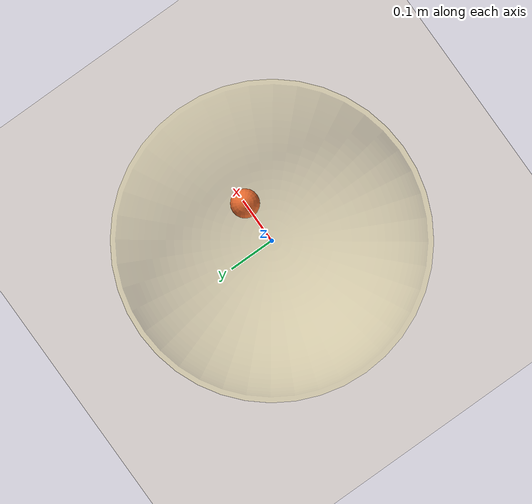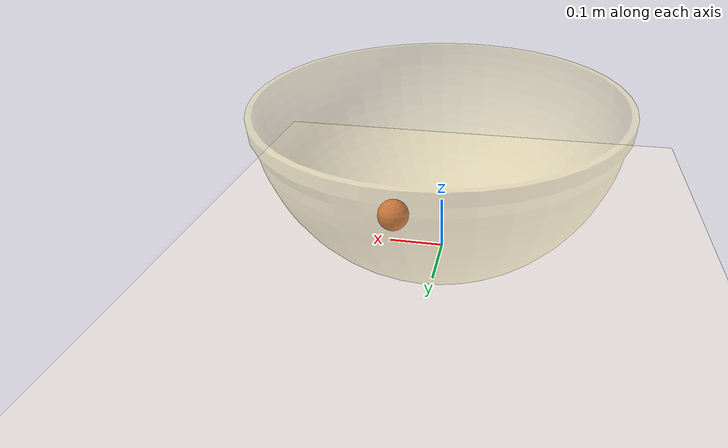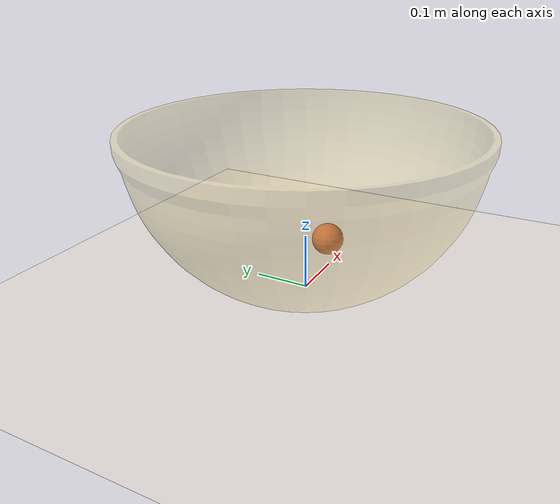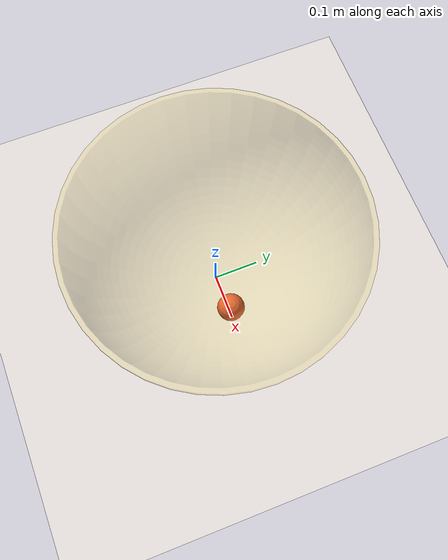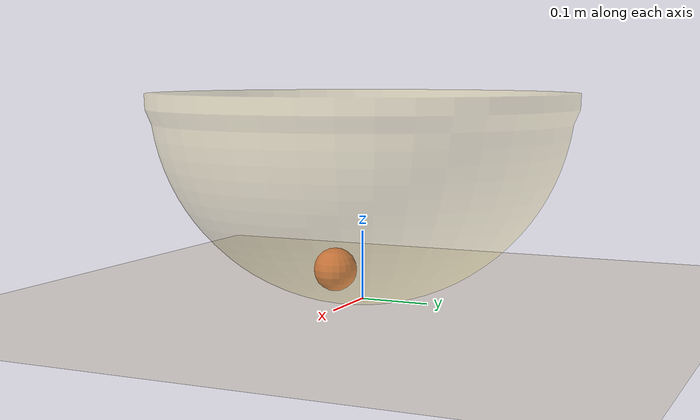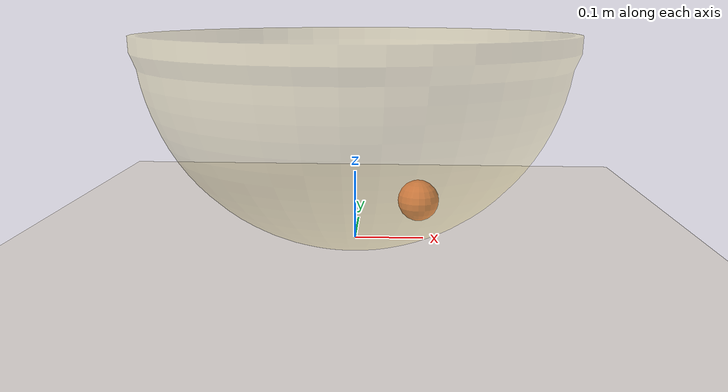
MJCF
<mujoco model="ball_in_spherical_bowl">
  <!-- Thin hemispherical shell R=0.3 m, ball R=0.03 m.
       T ≈ 1.23 s. Render 4.0 s. -->
  <compiler angle="radian" coordinate="local" autolimits="true"/>
  <option timestep="0.0005" gravity="0 0 -9.81" integrator="implicitfast"
          impratio="5" cone="elliptic"/>

  <visual>
    <headlight diffuse="0 0 0" ambient="0.50 0.48 0.55" specular="0 0 0"/>
    <rgba haze="0.94 0.91 0.90 1"/>
    <global azimuth="120" elevation="-15" offwidth="1920" offheight="1080" fovy="38"/>
    <quality shadowsize="8192" offsamples="8"/>
    <map shadowclip="6" shadowscale="0.7"/>
  </visual>

  <asset>
    <texture type="skybox" builtin="flat"
             rgb1="0.74 0.68 0.86" rgb2="0.74 0.68 0.86"
             width="512" height="512" mark="none" markrgb="0 0 0"/>
    <material name="floor_mat" rgba="0.94 0.91 0.90 1" specular="0" shininess="0"/>
    <material name="bowl_shell" rgba="0.96 0.90 0.58 0.38" specular="0.25" shininess="0.35"/>
    <material name="bob_red" rgba="0.92 0.42 0.18 1" specular="0.45" shininess="0.55"/>
    <mesh name="bowl_shell" vertex="0.00000 0.00000 0.00000 0.00000 0.00000 -0.00350 0.00000 0.00000 0.00000 0.00000 0.00000 -0.00350 0.00000 0.00000 0.00000 0.00000 0.00000 -0.00350 0.00000 0.00000 0.00000 0.00000 0.00000 -0.00350 0.00000 0.00000 0.00000 0.00000 0.00000 -0.00350 0.00000 0.00000 0.00000 0.00000 0.00000 -0.00350 0.00000 0.00000 0.00000 0.00000 0.00000 -0.00350 0.00000 0.00000 0.00000 0.00000 0.00000 -0.00350 0.00000 0.00000 0.00000 0.00000 0.00000 -0.00350 0.00000 0.00000 0.00000 0.00000 0.00000 -0.00350 0.00000 0.00000 0.00000 0.00000 0.00000 -0.00350 -0.00000 0.00000 0.00000 -0.00000 0.00000 -0.00350 -0.00000 0.00000 0.00000 -0.00000 0.00000 -0.00350 -0.00000 0.00000 0.00000 -0.00000 0.00000 -0.00350 -0.00000 0.00000 0.00000 -0.00000 0.00000 -0.00350 -0.00000 0.00000 0.00000 -0.00000 0.00000 -0.00350 -0.00000 0.00000 0.00000 -0.00000 0.00000 -0.00350 -0.00000 0.00000 0.00000 -0.00000 0.00000 -0.00350 -0.00000 0.00000 0.00000 -0.00000 0.00000 -0.00350 -0.00000 0.00000 0.00000 -0.00000 0.00000 -0.00350 -0.00000 0.00000 0.00000 -0.00000 0.00000 -0.00350 -0.00000 -0.00000 0.00000 -0.00000 -0.00000 -0.00350 -0.00000 -0.00000 0.00000 -0.00000 -0.00000 -0.00350 -0.00000 -0.00000 0.00000 -0.00000 -0.00000 -0.00350 -0.00000 -0.00000 0.00000 -0.00000 -0.00000 -0.00350 -0.00000 -0.00000 0.00000 -0.00000 -0.00000 -0.00350 -0.00000 -0.00000 0.00000 -0.00000 -0.00000 -0.00350 -0.00000 -0.00000 0.00000 -0.00000 -0.00000 -0.00350 -0.00000 -0.00000 0.00000 -0.00000 -0.00000 -0.00350 -0.00000 -0.00000 0.00000 -0.00000 -0.00000 -0.00350 -0.00000 -0.00000 0.00000 -0.00000 -0.00000 -0.00350 0.00000 -0.00000 0.00000 0.00000 -0.00000 -0.00350 0.00000 -0.00000 0.00000 0.00000 -0.00000 -0.00350 0.00000 -0.00000 0.00000 0.00000 -0.00000 -0.00350 0.00000 -0.00000 0.00000 0.00000 -0.00000 -0.00350 0.00000 -0.00000 0.00000 0.00000 -0.00000 -0.00350 0.00000 -0.00000 0.00000 0.00000 -0.00000 -0.00350 0.00000 -0.00000 0.00000 0.00000 -0.00000 -0.00350 0.00000 -0.00000 0.00000 0.00000 -0.00000 -0.00350 0.00000 -0.00000 0.00000 0.00000 -0.00000 -0.00350 0.02140 0.00000 0.00076 0.02165 0.00000 -0.00273 0.02114 0.00335 0.00076 0.02138 0.00339 -0.00273 0.02035 0.00661 0.00076 0.02059 0.00669 -0.00273 0.01907 0.00972 0.00076 0.01929 0.00983 -0.00273 0.01731 0.01258 0.00076 0.01752 0.01273 -0.00273 0.01513 0.01513 0.00076 0.01531 0.01531 -0.00273 0.01258 0.01731 0.00076 0.01273 0.01752 -0.00273 0.00972 0.01907 0.00076 0.00983 0.01929 -0.00273 0.00661 0.02035 0.00076 0.00669 0.02059 -0.00273 0.00335 0.02114 0.00076 0.00339 0.02138 -0.00273 0.00000 0.02140 0.00076 0.00000 0.02165 -0.00273 -0.00335 0.02114 0.00076 -0.00339 0.02138 -0.00273 -0.00661 0.02035 0.00076 -0.00669 0.02059 -0.00273 -0.00972 0.01907 0.00076 -0.00983 0.01929 -0.00273 -0.01258 0.01731 0.00076 -0.01273 0.01752 -0.00273 -0.01513 0.01513 0.00076 -0.01531 0.01531 -0.00273 -0.01731 0.01258 0.00076 -0.01752 0.01273 -0.00273 -0.01907 0.00972 0.00076 -0.01929 0.00983 -0.00273 -0.02035 0.00661 0.00076 -0.02059 0.00669 -0.00273 -0.02114 0.00335 0.00076 -0.02138 0.00339 -0.00273 -0.02140 0.00000 0.00076 -0.02165 0.00000 -0.00273 -0.02114 -0.00335 0.00076 -0.02138 -0.00339 -0.00273 -0.02035 -0.00661 0.00076 -0.02059 -0.00669 -0.00273 -0.01907 -0.00972 0.00076 -0.01929 -0.00983 -0.00273 -0.01731 -0.01258 0.00076 -0.01752 -0.01273 -0.00273 -0.01513 -0.01513 0.00076 -0.01531 -0.01531 -0.00273 -0.01258 -0.01731 0.00076 -0.01273 -0.01752 -0.00273 -0.00972 -0.01907 0.00076 -0.00983 -0.01929 -0.00273 -0.00661 -0.02035 0.00076 -0.00669 -0.02059 -0.00273 -0.00335 -0.02114 0.00076 -0.00339 -0.02138 -0.00273 -0.00000 -0.02140 0.00076 -0.00000 -0.02165 -0.00273 0.00335 -0.02114 0.00076 0.00339 -0.02138 -0.00273 0.00661 -0.02035 0.00076 0.00669 -0.02059 -0.00273 0.00972 -0.01907 0.00076 0.00983 -0.01929 -0.00273 0.01258 -0.01731 0.00076 0.01273 -0.01752 -0.00273 0.01513 -0.01513 0.00076 0.01531 -0.01531 -0.00273 0.01731 -0.01258 0.00076 0.01752 -0.01273 -0.00273 0.01907 -0.00972 0.00076 0.01929 -0.00983 -0.00273 0.02035 -0.00661 0.00076 0.02059 -0.00669 -0.00273 0.02114 -0.00335 0.00076 0.02138 -0.00339 -0.00273 0.04269 0.00000 0.00305 0.04319 0.00000 -0.00041 0.04217 0.00668 0.00305 0.04266 0.00676 -0.00041 0.04060 0.01319 0.00305 0.04108 0.01335 -0.00041 0.03804 0.01938 0.00305 0.03848 0.01961 -0.00041 0.03454 0.02510 0.00305 0.03494 0.02539 -0.00041 0.03019 0.03019 0.00305 0.03054 0.03054 -0.00041 0.02510 0.03454 0.00305 0.02539 0.03494 -0.00041 0.01938 0.03804 0.00305 0.01961 0.03848 -0.00041 0.01319 0.04060 0.00305 0.01335 0.04108 -0.00041 0.00668 0.04217 0.00305 0.00676 0.04266 -0.00041 0.00000 0.04269 0.00305 0.00000 0.04319 -0.00041 -0.00668 0.04217 0.00305 -0.00676 0.04266 -0.00041 -0.01319 0.04060 0.00305 -0.01335 0.04108 -0.00041 -0.01938 0.03804 0.00305 -0.01961 0.03848 -0.00041 -0.02510 0.03454 0.00305 -0.02539 0.03494 -0.00041 -0.03019 0.03019 0.00305 -0.03054 0.03054 -0.00041 -0.03454 0.02510 0.00305 -0.03494 0.02539 -0.00041 -0.03804 0.01938 0.00305 -0.03848 0.01961 -0.00041 -0.04060 0.01319 0.00305 -0.04108 0.01335 -0.00041 -0.04217 0.00668 0.00305 -0.04266 0.00676 -0.00041 -0.04269 0.00000 0.00305 -0.04319 0.00000 -0.00041 -0.04217 -0.00668 0.00305 -0.04266 -0.00676 -0.00041 -0.04060 -0.01319 0.00305 -0.04108 -0.01335 -0.00041 -0.03804 -0.01938 0.00305 -0.03848 -0.01961 -0.00041 -0.03454 -0.02510 0.00305 -0.03494 -0.02539 -0.00041 -0.03019 -0.03019 0.00305 -0.03054 -0.03054 -0.00041 -0.02510 -0.03454 0.00305 -0.02539 -0.03494 -0.00041 -0.01938 -0.03804 0.00305 -0.01961 -0.03848 -0.00041 -0.01319 -0.04060 0.00305 -0.01335 -0.04108 -0.00041 -0.00668 -0.04217 0.00305 -0.00676 -0.04266 -0.00041 -0.00000 -0.04269 0.00305 -0.00000 -0.04319 -0.00041 0.00668 -0.04217 0.00305 0.00676 -0.04266 -0.00041 0.01319 -0.04060 0.00305 0.01335 -0.04108 -0.00041 0.01938 -0.03804 0.00305 0.01961 -0.03848 -0.00041 0.02510 -0.03454 0.00305 0.02539 -0.03494 -0.00041 0.03019 -0.03019 0.00305 0.03054 -0.03054 -0.00041 0.03454 -0.02510 0.00305 0.03494 -0.02539 -0.00041 0.03804 -0.01938 0.00305 0.03848 -0.01961 -0.00041 0.04060 -0.01319 0.00305 0.04108 -0.01335 -0.00041 0.04217 -0.00668 0.00305 0.04266 -0.00676 -0.00041 0.06377 0.00000 0.00686 0.06451 0.00000 0.00344 0.06298 0.00998 0.00686 0.06372 0.01009 0.00344 0.06065 0.01971 0.00686 0.06136 0.01994 0.00344 0.05682 0.02895 0.00686 0.05748 0.02929 0.00344 0.05159 0.03748 0.00686 0.05219 0.03792 0.00344 0.04509 0.04509 0.00686 0.04562 0.04562 0.00344 0.03748 0.05159 0.00686 0.03792 0.05219 0.00344 0.02895 0.05682 0.00686 0.02929 0.05748 0.00344 0.01971 0.06065 0.00686 0.01994 0.06136 0.00344 0.00998 0.06298 0.00686 0.01009 0.06372 0.00344 0.00000 0.06377 0.00686 0.00000 0.06451 0.00344 -0.00998 0.06298 0.00686 -0.01009 0.06372 0.00344 -0.01971 0.06065 0.00686 -0.01994 0.06136 0.00344 -0.02895 0.05682 0.00686 -0.02929 0.05748 0.00344 -0.03748 0.05159 0.00686 -0.03792 0.05219 0.00344 -0.04509 0.04509 0.00686 -0.04562 0.04562 0.00344 -0.05159 0.03748 0.00686 -0.05219 0.03792 0.00344 -0.05682 0.02895 0.00686 -0.05748 0.02929 0.00344 -0.06065 0.01971 0.00686 -0.06136 0.01994 0.00344 -0.06298 0.00998 0.00686 -0.06372 0.01009 0.00344 -0.06377 0.00000 0.00686 -0.06451 0.00000 0.00344 -0.06298 -0.00998 0.00686 -0.06372 -0.01009 0.00344 -0.06065 -0.01971 0.00686 -0.06136 -0.01994 0.00344 -0.05682 -0.02895 0.00686 -0.05748 -0.02929 0.00344 -0.05159 -0.03748 0.00686 -0.05219 -0.03792 0.00344 -0.04509 -0.04509 0.00686 -0.04562 -0.04562 0.00344 -0.03748 -0.05159 0.00686 -0.03792 -0.05219 0.00344 -0.02895 -0.05682 0.00686 -0.02929 -0.05748 0.00344 -0.01971 -0.06065 0.00686 -0.01994 -0.06136 0.00344 -0.00998 -0.06298 0.00686 -0.01009 -0.06372 0.00344 -0.00000 -0.06377 0.00686 -0.00000 -0.06451 0.00344 0.00998 -0.06298 0.00686 0.01009 -0.06372 0.00344 0.01971 -0.06065 0.00686 0.01994 -0.06136 0.00344 0.02895 -0.05682 0.00686 0.02929 -0.05748 0.00344 0.03748 -0.05159 0.00686 0.03792 -0.05219 0.00344 0.04509 -0.04509 0.00686 0.04562 -0.04562 0.00344 0.05159 -0.03748 0.00686 0.05219 -0.03792 0.00344 0.05682 -0.02895 0.00686 0.05748 -0.02929 0.00344 0.06065 -0.01971 0.00686 0.06136 -0.01994 0.00344 0.06298 -0.00998 0.00686 0.06372 -0.01009 0.00344 0.08452 0.00000 0.01215 0.08551 0.00000 0.00879 0.08348 0.01322 0.01215 0.08445 0.01338 0.00879 0.08038 0.02612 0.01215 0.08132 0.02642 0.00879 0.07531 0.03837 0.01215 0.07619 0.03882 0.00879 0.06838 0.04968 0.01215 0.06918 0.05026 0.00879 0.05976 0.05976 0.01215 0.06046 0.06046 0.00879 0.04968 0.06838 0.01215 0.05026 0.06918 0.00879 0.03837 0.07531 0.01215 0.03882 0.07619 0.00879 0.02612 0.08038 0.01215 0.02642 0.08132 0.00879 0.01322 0.08348 0.01215 0.01338 0.08445 0.00879 0.00000 0.08452 0.01215 0.00000 0.08551 0.00879 -0.01322 0.08348 0.01215 -0.01338 0.08445 0.00879 -0.02612 0.08038 0.01215 -0.02642 0.08132 0.00879 -0.03837 0.07531 0.01215 -0.03882 0.07619 0.00879 -0.04968 0.06838 0.01215 -0.05026 0.06918 0.00879 -0.05976 0.05976 0.01215 -0.06046 0.06046 0.00879 -0.06838 0.04968 0.01215 -0.06918 0.05026 0.00879 -0.07531 0.03837 0.01215 -0.07619 0.03882 0.00879 -0.08038 0.02612 0.01215 -0.08132 0.02642 0.00879 -0.08348 0.01322 0.01215 -0.08445 0.01338 0.00879 -0.08452 0.00000 0.01215 -0.08551 0.00000 0.00879 -0.08348 -0.01322 0.01215 -0.08445 -0.01338 0.00879 -0.08038 -0.02612 0.01215 -0.08132 -0.02642 0.00879 -0.07531 -0.03837 0.01215 -0.07619 -0.03882 0.00879 -0.06838 -0.04968 0.01215 -0.06918 -0.05026 0.00879 -0.05976 -0.05976 0.01215 -0.06046 -0.06046 0.00879 -0.04968 -0.06838 0.01215 -0.05026 -0.06918 0.00879 -0.03837 -0.07531 0.01215 -0.03882 -0.07619 0.00879 -0.02612 -0.08038 0.01215 -0.02642 -0.08132 0.00879 -0.01322 -0.08348 0.01215 -0.01338 -0.08445 0.00879 -0.00000 -0.08452 0.01215 -0.00000 -0.08551 0.00879 0.01322 -0.08348 0.01215 0.01338 -0.08445 0.00879 0.02612 -0.08038 0.01215 0.02642 -0.08132 0.00879 0.03837 -0.07531 0.01215 0.03882 -0.07619 0.00879 0.04968 -0.06838 0.01215 0.05026 -0.06918 0.00879 0.05976 -0.05976 0.01215 0.06046 -0.06046 0.00879 0.06838 -0.04968 0.01215 0.06918 -0.05026 0.00879 0.07531 -0.03837 0.01215 0.07619 -0.03882 0.00879 0.08038 -0.02612 0.01215 0.08132 -0.02642 0.00879 0.08348 -0.01322 0.01215 0.08445 -0.01338 0.00879 0.10484 0.00000 0.01892 0.10606 0.00000 0.01564 0.10355 0.01640 0.01892 0.10476 0.01659 0.01564 0.09971 0.03240 0.01892 0.10087 0.03278 0.01564 0.09341 0.04760 0.01892 0.09450 0.04815 0.01564 0.08482 0.06162 0.01892 0.08581 0.06234 0.01564 0.07413 0.07413 0.01892 0.07500 0.07500 0.01564 0.06162 0.08482 0.01892 0.06234 0.08581 0.01564 0.04760 0.09341 0.01892 0.04815 0.09450 0.01564 0.03240 0.09971 0.01892 0.03278 0.10087 0.01564 0.01640 0.10355 0.01892 0.01659 0.10476 0.01564 0.00000 0.10484 0.01892 0.00000 0.10606 0.01564 -0.01640 0.10355 0.01892 -0.01659 0.10476 0.01564 -0.03240 0.09971 0.01892 -0.03278 0.10087 0.01564 -0.04760 0.09341 0.01892 -0.04815 0.09450 0.01564 -0.06162 0.08482 0.01892 -0.06234 0.08581 0.01564 -0.07413 0.07413 0.01892 -0.07500 0.07500 0.01564 -0.08482 0.06162 0.01892 -0.08581 0.06234 0.01564 -0.09341 0.04760 0.01892 -0.09450 0.04815 0.01564 -0.09971 0.03240 0.01892 -0.10087 0.03278 0.01564 -0.10355 0.01640 0.01892 -0.10476 0.01659 0.01564 -0.10484 0.00000 0.01892 -0.10606 0.00000 0.01564 -0.10355 -0.01640 0.01892 -0.10476 -0.01659 0.01564 -0.09971 -0.03240 0.01892 -0.10087 -0.03278 0.01564 -0.09341 -0.04760 0.01892 -0.09450 -0.04815 0.01564 -0.08482 -0.06162 0.01892 -0.08581 -0.06234 0.01564 -0.07413 -0.07413 0.01892 -0.07500 -0.07500 0.01564 -0.06162 -0.08482 0.01892 -0.06234 -0.08581 0.01564 -0.04760 -0.09341 0.01892 -0.04815 -0.09450 0.01564 -0.03240 -0.09971 0.01892 -0.03278 -0.10087 0.01564 -0.01640 -0.10355 0.01892 -0.01659 -0.10476 0.01564 -0.00000 -0.10484 0.01892 -0.00000 -0.10606 0.01564 0.01640 -0.10355 0.01892 0.01659 -0.10476 0.01564 0.03240 -0.09971 0.01892 0.03278 -0.10087 0.01564 0.04760 -0.09341 0.01892 0.04815 -0.09450 0.01564 0.06162 -0.08482 0.01892 0.06234 -0.08581 0.01564 0.07413 -0.07413 0.01892 0.07500 -0.07500 0.01564 0.08482 -0.06162 0.01892 0.08581 -0.06234 0.01564 0.09341 -0.04760 0.01892 0.09450 -0.04815 0.01564 0.09971 -0.03240 0.01892 0.10087 -0.03278 0.01564 0.10355 -0.01640 0.01892 0.10476 -0.01659 0.01564 0.12462 0.00000 0.02711 0.12608 0.00000 0.02393 0.12309 0.01950 0.02711 0.12453 0.01972 0.02393 0.11852 0.03851 0.02711 0.11991 0.03896 0.02393 0.11104 0.05658 0.02711 0.11234 0.05724 0.02393 0.10082 0.07325 0.02711 0.10200 0.07411 0.02393 0.08812 0.08812 0.02711 0.08915 0.08915 0.02393 0.07325 0.10082 0.02711 0.07411 0.10200 0.02393 0.05658 0.11104 0.02711 0.05724 0.11234 0.02393 0.03851 0.11852 0.02711 0.03896 0.11991 0.02393 0.01950 0.12309 0.02711 0.01972 0.12453 0.02393 0.00000 0.12462 0.02711 0.00000 0.12608 0.02393 -0.01950 0.12309 0.02711 -0.01972 0.12453 0.02393 -0.03851 0.11852 0.02711 -0.03896 0.11991 0.02393 -0.05658 0.11104 0.02711 -0.05724 0.11234 0.02393 -0.07325 0.10082 0.02711 -0.07411 0.10200 0.02393 -0.08812 0.08812 0.02711 -0.08915 0.08915 0.02393 -0.10082 0.07325 0.02711 -0.10200 0.07411 0.02393 -0.11104 0.05658 0.02711 -0.11234 0.05724 0.02393 -0.11852 0.03851 0.02711 -0.11991 0.03896 0.02393 -0.12309 0.01950 0.02711 -0.12453 0.01972 0.02393 -0.12462 0.00000 0.02711 -0.12608 0.00000 0.02393 -0.12309 -0.01950 0.02711 -0.12453 -0.01972 0.02393 -0.11852 -0.03851 0.02711 -0.11991 -0.03896 0.02393 -0.11104 -0.05658 0.02711 -0.11234 -0.05724 0.02393 -0.10082 -0.07325 0.02711 -0.10200 -0.07411 0.02393 -0.08812 -0.08812 0.02711 -0.08915 -0.08915 0.02393 -0.07325 -0.10082 0.02711 -0.07411 -0.10200 0.02393 -0.05658 -0.11104 0.02711 -0.05724 -0.11234 0.02393 -0.03851 -0.11852 0.02711 -0.03896 -0.11991 0.02393 -0.01950 -0.12309 0.02711 -0.01972 -0.12453 0.02393 -0.00000 -0.12462 0.02711 -0.00000 -0.12608 0.02393 0.01950 -0.12309 0.02711 0.01972 -0.12453 0.02393 0.03851 -0.11852 0.02711 0.03896 -0.11991 0.02393 0.05658 -0.11104 0.02711 0.05724 -0.11234 0.02393 0.07325 -0.10082 0.02711 0.07411 -0.10200 0.02393 0.08812 -0.08812 0.02711 0.08915 -0.08915 0.02393 0.10082 -0.07325 0.02711 0.10200 -0.07411 0.02393 0.11104 -0.05658 0.02711 0.11234 -0.05724 0.02393 0.11852 -0.03851 0.02711 0.11991 -0.03896 0.02393 0.12309 -0.01950 0.02711 0.12453 -0.01972 0.02393 0.14377 0.00000 0.03670 0.14545 0.00000 0.03362 0.14200 0.02249 0.03670 0.14366 0.02275 0.03362 0.13674 0.04443 0.03670 0.13833 0.04495 0.03362 0.12810 0.06527 0.03670 0.12960 0.06603 0.03362 0.11632 0.08451 0.03670 0.11767 0.08549 0.03362 0.10166 0.10166 0.03670 0.10285 0.10285 0.03362 0.08451 0.11632 0.03670 0.08549 0.11767 0.03362 0.06527 0.12810 0.03670 0.06603 0.12960 0.03362 0.04443 0.13674 0.03670 0.04495 0.13833 0.03362 0.02249 0.14200 0.03670 0.02275 0.14366 0.03362 0.00000 0.14377 0.03670 0.00000 0.14545 0.03362 -0.02249 0.14200 0.03670 -0.02275 0.14366 0.03362 -0.04443 0.13674 0.03670 -0.04495 0.13833 0.03362 -0.06527 0.12810 0.03670 -0.06603 0.12960 0.03362 -0.08451 0.11632 0.03670 -0.08549 0.11767 0.03362 -0.10166 0.10166 0.03670 -0.10285 0.10285 0.03362 -0.11632 0.08451 0.03670 -0.11767 0.08549 0.03362 -0.12810 0.06527 0.03670 -0.12960 0.06603 0.03362 -0.13674 0.04443 0.03670 -0.13833 0.04495 0.03362 -0.14200 0.02249 0.03670 -0.14366 0.02275 0.03362 -0.14377 0.00000 0.03670 -0.14545 0.00000 0.03362 -0.14200 -0.02249 0.03670 -0.14366 -0.02275 0.03362 -0.13674 -0.04443 0.03670 -0.13833 -0.04495 0.03362 -0.12810 -0.06527 0.03670 -0.12960 -0.06603 0.03362 -0.11632 -0.08451 0.03670 -0.11767 -0.08549 0.03362 -0.10166 -0.10166 0.03670 -0.10285 -0.10285 0.03362 -0.08451 -0.11632 0.03670 -0.08549 -0.11767 0.03362 -0.06527 -0.12810 0.03670 -0.06603 -0.12960 0.03362 -0.04443 -0.13674 0.03670 -0.04495 -0.13833 0.03362 -0.02249 -0.14200 0.03670 -0.02275 -0.14366 0.03362 -0.00000 -0.14377 0.03670 -0.00000 -0.14545 0.03362 0.02249 -0.14200 0.03670 0.02275 -0.14366 0.03362 0.04443 -0.13674 0.03670 0.04495 -0.13833 0.03362 0.06527 -0.12810 0.03670 0.06603 -0.12960 0.03362 0.08451 -0.11632 0.03670 0.08549 -0.11767 0.03362 0.10166 -0.10166 0.03670 0.10285 -0.10285 0.03362 0.11632 -0.08451 0.03670 0.11767 -0.08549 0.03362 0.12810 -0.06527 0.03670 0.12960 -0.06603 0.03362 0.13674 -0.04443 0.03670 0.13833 -0.04495 0.03362 0.14200 -0.02249 0.03670 0.14366 -0.02275 0.03362 0.16219 0.00000 0.04762 0.16408 0.00000 0.04468 0.16020 0.02537 0.04762 0.16206 0.02567 0.04468 0.15425 0.05012 0.04762 0.15605 0.05070 0.04468 0.14451 0.07363 0.04762 0.14620 0.07449 0.04468 0.13122 0.09533 0.04762 0.13275 0.09645 0.04468 0.11469 0.11469 0.04762 0.11603 0.11603 0.04468 0.09533 0.13122 0.04762 0.09645 0.13275 0.04468 0.07363 0.14451 0.04762 0.07449 0.14620 0.04468 0.05012 0.15425 0.04762 0.05070 0.15605 0.04468 0.02537 0.16020 0.04762 0.02567 0.16206 0.04468 0.00000 0.16219 0.04762 0.00000 0.16408 0.04468 -0.02537 0.16020 0.04762 -0.02567 0.16206 0.04468 -0.05012 0.15425 0.04762 -0.05070 0.15605 0.04468 -0.07363 0.14451 0.04762 -0.07449 0.14620 0.04468 -0.09533 0.13122 0.04762 -0.09645 0.13275 0.04468 -0.11469 0.11469 0.04762 -0.11603 0.11603 0.04468 -0.13122 0.09533 0.04762 -0.13275 0.09645 0.04468 -0.14451 0.07363 0.04762 -0.14620 0.07449 0.04468 -0.15425 0.05012 0.04762 -0.15605 0.05070 0.04468 -0.16020 0.02537 0.04762 -0.16206 0.02567 0.04468 -0.16219 0.00000 0.04762 -0.16408 0.00000 0.04468 -0.16020 -0.02537 0.04762 -0.16206 -0.02567 0.04468 -0.15425 -0.05012 0.04762 -0.15605 -0.05070 0.04468 -0.14451 -0.07363 0.04762 -0.14620 -0.07449 0.04468 -0.13122 -0.09533 0.04762 -0.13275 -0.09645 0.04468 -0.11469 -0.11469 0.04762 -0.11603 -0.11603 0.04468 -0.09533 -0.13122 0.04762 -0.09645 -0.13275 0.04468 -0.07363 -0.14451 0.04762 -0.07449 -0.14620 0.04468 -0.05012 -0.15425 0.04762 -0.05070 -0.15605 0.04468 -0.02537 -0.16020 0.04762 -0.02567 -0.16206 0.04468 -0.00000 -0.16219 0.04762 -0.00000 -0.16408 0.04468 0.02537 -0.16020 0.04762 0.02567 -0.16206 0.04468 0.05012 -0.15425 0.04762 0.05070 -0.15605 0.04468 0.07363 -0.14451 0.04762 0.07449 -0.14620 0.04468 0.09533 -0.13122 0.04762 0.09645 -0.13275 0.04468 0.11469 -0.11469 0.04762 0.11603 -0.11603 0.04468 0.13122 -0.09533 0.04762 0.13275 -0.09645 0.04468 0.14451 -0.07363 0.04762 0.14620 -0.07449 0.04468 0.15425 -0.05012 0.04762 0.15605 -0.05070 0.04468 0.16020 -0.02537 0.04762 0.16206 -0.02567 0.04468 0.17978 0.00000 0.05984 0.18188 0.00000 0.05704 0.17757 0.02812 0.05984 0.17964 0.02845 0.05704 0.17098 0.05556 0.05984 0.17298 0.05620 0.05704 0.16019 0.08162 0.05984 0.16206 0.08257 0.05704 0.14545 0.10567 0.05984 0.14714 0.10691 0.05704 0.12713 0.12713 0.05984 0.12861 0.12861 0.05704 0.10567 0.14545 0.05984 0.10691 0.14714 0.05704 0.08162 0.16019 0.05984 0.08257 0.16206 0.05704 0.05556 0.17098 0.05984 0.05620 0.17298 0.05704 0.02812 0.17757 0.05984 0.02845 0.17964 0.05704 0.00000 0.17978 0.05984 0.00000 0.18188 0.05704 -0.02812 0.17757 0.05984 -0.02845 0.17964 0.05704 -0.05556 0.17098 0.05984 -0.05620 0.17298 0.05704 -0.08162 0.16019 0.05984 -0.08257 0.16206 0.05704 -0.10567 0.14545 0.05984 -0.10691 0.14714 0.05704 -0.12713 0.12713 0.05984 -0.12861 0.12861 0.05704 -0.14545 0.10567 0.05984 -0.14714 0.10691 0.05704 -0.16019 0.08162 0.05984 -0.16206 0.08257 0.05704 -0.17098 0.05556 0.05984 -0.17298 0.05620 0.05704 -0.17757 0.02812 0.05984 -0.17964 0.02845 0.05704 -0.17978 0.00000 0.05984 -0.18188 0.00000 0.05704 -0.17757 -0.02812 0.05984 -0.17964 -0.02845 0.05704 -0.17098 -0.05556 0.05984 -0.17298 -0.05620 0.05704 -0.16019 -0.08162 0.05984 -0.16206 -0.08257 0.05704 -0.14545 -0.10567 0.05984 -0.14714 -0.10691 0.05704 -0.12713 -0.12713 0.05984 -0.12861 -0.12861 0.05704 -0.10567 -0.14545 0.05984 -0.10691 -0.14714 0.05704 -0.08162 -0.16019 0.05984 -0.08257 -0.16206 0.05704 -0.05556 -0.17098 0.05984 -0.05620 -0.17298 0.05704 -0.02812 -0.17757 0.05984 -0.02845 -0.17964 0.05704 -0.00000 -0.17978 0.05984 -0.00000 -0.18188 0.05704 0.02812 -0.17757 0.05984 0.02845 -0.17964 0.05704 0.05556 -0.17098 0.05984 0.05620 -0.17298 0.05704 0.08162 -0.16019 0.05984 0.08257 -0.16206 0.05704 0.10567 -0.14545 0.05984 0.10691 -0.14714 0.05704 0.12713 -0.12713 0.05984 0.12861 -0.12861 0.05704 0.14545 -0.10567 0.05984 0.14714 -0.10691 0.05704 0.16019 -0.08162 0.05984 0.16206 -0.08257 0.05704 0.17098 -0.05556 0.05984 0.17298 -0.05620 0.05704 0.17757 -0.02812 0.05984 0.17964 -0.02845 0.05704 0.19646 0.00000 0.07328 0.19875 0.00000 0.07063 0.19404 0.03073 0.07328 0.19630 0.03109 0.07063 0.18684 0.06071 0.07328 0.18902 0.06142 0.07063 0.17505 0.08919 0.07328 0.17709 0.09023 0.07063 0.15894 0.11548 0.07328 0.16079 0.11682 0.07063 0.13892 0.13892 0.07328 0.14054 0.14054 0.07063 0.11548 0.15894 0.07328 0.11682 0.16079 0.07063 0.08919 0.17505 0.07328 0.09023 0.17709 0.07063 0.06071 0.18684 0.07328 0.06142 0.18902 0.07063 0.03073 0.19404 0.07328 0.03109 0.19630 0.07063 0.00000 0.19646 0.07328 0.00000 0.19875 0.07063 -0.03073 0.19404 0.07328 -0.03109 0.19630 0.07063 -0.06071 0.18684 0.07328 -0.06142 0.18902 0.07063 -0.08919 0.17505 0.07328 -0.09023 0.17709 0.07063 -0.11548 0.15894 0.07328 -0.11682 0.16079 0.07063 -0.13892 0.13892 0.07328 -0.14054 0.14054 0.07063 -0.15894 0.11548 0.07328 -0.16079 0.11682 0.07063 -0.17505 0.08919 0.07328 -0.17709 0.09023 0.07063 -0.18684 0.06071 0.07328 -0.18902 0.06142 0.07063 -0.19404 0.03073 0.07328 -0.19630 0.03109 0.07063 -0.19646 0.00000 0.07328 -0.19875 0.00000 0.07063 -0.19404 -0.03073 0.07328 -0.19630 -0.03109 0.07063 -0.18684 -0.06071 0.07328 -0.18902 -0.06142 0.07063 -0.17505 -0.08919 0.07328 -0.17709 -0.09023 0.07063 -0.15894 -0.11548 0.07328 -0.16079 -0.11682 0.07063 -0.13892 -0.13892 0.07328 -0.14054 -0.14054 0.07063 -0.11548 -0.15894 0.07328 -0.11682 -0.16079 0.07063 -0.08919 -0.17505 0.07328 -0.09023 -0.17709 0.07063 -0.06071 -0.18684 0.07328 -0.06142 -0.18902 0.07063 -0.03073 -0.19404 0.07328 -0.03109 -0.19630 0.07063 -0.00000 -0.19646 0.07328 -0.00000 -0.19875 0.07063 0.03073 -0.19404 0.07328 0.03109 -0.19630 0.07063 0.06071 -0.18684 0.07328 0.06142 -0.18902 0.07063 0.08919 -0.17505 0.07328 0.09023 -0.17709 0.07063 0.11548 -0.15894 0.07328 0.11682 -0.16079 0.07063 0.13892 -0.13892 0.07328 0.14054 -0.14054 0.07063 0.15894 -0.11548 0.07328 0.16079 -0.11682 0.07063 0.17505 -0.08919 0.07328 0.17709 -0.09023 0.07063 0.18684 -0.06071 0.07328 0.18902 -0.06142 0.07063 0.19404 -0.03073 0.07328 0.19630 -0.03109 0.07063 0.21213 0.00000 0.08787 0.21461 0.00000 0.08539 0.20952 0.03318 0.08787 0.21196 0.03357 0.08539 0.20175 0.06555 0.08787 0.20410 0.06632 0.08539 0.18901 0.09631 0.08787 0.19122 0.09743 0.08539 0.17162 0.12469 0.08787 0.17362 0.12614 0.08539 0.15000 0.15000 0.08787 0.15175 0.15175 0.08539 0.12469 0.17162 0.08787 0.12614 0.17362 0.08539 0.09631 0.18901 0.08787 0.09743 0.19122 0.08539 0.06555 0.20175 0.08787 0.06632 0.20410 0.08539 0.03318 0.20952 0.08787 0.03357 0.21196 0.08539 0.00000 0.21213 0.08787 0.00000 0.21461 0.08539 -0.03318 0.20952 0.08787 -0.03357 0.21196 0.08539 -0.06555 0.20175 0.08787 -0.06632 0.20410 0.08539 -0.09631 0.18901 0.08787 -0.09743 0.19122 0.08539 -0.12469 0.17162 0.08787 -0.12614 0.17362 0.08539 -0.15000 0.15000 0.08787 -0.15175 0.15175 0.08539 -0.17162 0.12469 0.08787 -0.17362 0.12614 0.08539 -0.18901 0.09631 0.08787 -0.19122 0.09743 0.08539 -0.20175 0.06555 0.08787 -0.20410 0.06632 0.08539 -0.20952 0.03318 0.08787 -0.21196 0.03357 0.08539 -0.21213 0.00000 0.08787 -0.21461 0.00000 0.08539 -0.20952 -0.03318 0.08787 -0.21196 -0.03357 0.08539 -0.20175 -0.06555 0.08787 -0.20410 -0.06632 0.08539 -0.18901 -0.09631 0.08787 -0.19122 -0.09743 0.08539 -0.17162 -0.12469 0.08787 -0.17362 -0.12614 0.08539 -0.15000 -0.15000 0.08787 -0.15175 -0.15175 0.08539 -0.12469 -0.17162 0.08787 -0.12614 -0.17362 0.08539 -0.09631 -0.18901 0.08787 -0.09743 -0.19122 0.08539 -0.06555 -0.20175 0.08787 -0.06632 -0.20410 0.08539 -0.03318 -0.20952 0.08787 -0.03357 -0.21196 0.08539 -0.00000 -0.21213 0.08787 -0.00000 -0.21461 0.08539 0.03318 -0.20952 0.08787 0.03357 -0.21196 0.08539 0.06555 -0.20175 0.08787 0.06632 -0.20410 0.08539 0.09631 -0.18901 0.08787 0.09743 -0.19122 0.08539 0.12469 -0.17162 0.08787 0.12614 -0.17362 0.08539 0.15000 -0.15000 0.08787 0.15175 -0.15175 0.08539 0.17162 -0.12469 0.08787 0.17362 -0.12614 0.08539 0.18901 -0.09631 0.08787 0.19122 -0.09743 0.08539 0.20175 -0.06555 0.08787 0.20410 -0.06632 0.08539 0.20952 -0.03318 0.08787 0.21196 -0.03357 0.08539 0.22672 0.00000 0.10354 0.22937 0.00000 0.10125 0.22393 0.03547 0.10354 0.22655 0.03588 0.10125 0.21563 0.07006 0.10354 0.21814 0.07088 0.10125 0.20201 0.10293 0.10354 0.20437 0.10413 0.10125 0.18342 0.13327 0.10354 0.18556 0.13482 0.10125 0.16032 0.16032 0.10354 0.16219 0.16219 0.10125 0.13327 0.18342 0.10354 0.13482 0.18556 0.10125 0.10293 0.20201 0.10354 0.10413 0.20437 0.10125 0.07006 0.21563 0.10354 0.07088 0.21814 0.10125 0.03547 0.22393 0.10354 0.03588 0.22655 0.10125 0.00000 0.22672 0.10354 0.00000 0.22937 0.10125 -0.03547 0.22393 0.10354 -0.03588 0.22655 0.10125 -0.07006 0.21563 0.10354 -0.07088 0.21814 0.10125 -0.10293 0.20201 0.10354 -0.10413 0.20437 0.10125 -0.13327 0.18342 0.10354 -0.13482 0.18556 0.10125 -0.16032 0.16032 0.10354 -0.16219 0.16219 0.10125 -0.18342 0.13327 0.10354 -0.18556 0.13482 0.10125 -0.20201 0.10293 0.10354 -0.20437 0.10413 0.10125 -0.21563 0.07006 0.10354 -0.21814 0.07088 0.10125 -0.22393 0.03547 0.10354 -0.22655 0.03588 0.10125 -0.22672 0.00000 0.10354 -0.22937 0.00000 0.10125 -0.22393 -0.03547 0.10354 -0.22655 -0.03588 0.10125 -0.21563 -0.07006 0.10354 -0.21814 -0.07088 0.10125 -0.20201 -0.10293 0.10354 -0.20437 -0.10413 0.10125 -0.18342 -0.13327 0.10354 -0.18556 -0.13482 0.10125 -0.16032 -0.16032 0.10354 -0.16219 -0.16219 0.10125 -0.13327 -0.18342 0.10354 -0.13482 -0.18556 0.10125 -0.10293 -0.20201 0.10354 -0.10413 -0.20437 0.10125 -0.07006 -0.21563 0.10354 -0.07088 -0.21814 0.10125 -0.03547 -0.22393 0.10354 -0.03588 -0.22655 0.10125 -0.00000 -0.22672 0.10354 -0.00000 -0.22937 0.10125 0.03547 -0.22393 0.10354 0.03588 -0.22655 0.10125 0.07006 -0.21563 0.10354 0.07088 -0.21814 0.10125 0.10293 -0.20201 0.10354 0.10413 -0.20437 0.10125 0.13327 -0.18342 0.10354 0.13482 -0.18556 0.10125 0.16032 -0.16032 0.10354 0.16219 -0.16219 0.10125 0.18342 -0.13327 0.10354 0.18556 -0.13482 0.10125 0.20201 -0.10293 0.10354 0.20437 -0.10413 0.10125 0.21563 -0.07006 0.10354 0.21814 -0.07088 0.10125 0.22393 -0.03547 0.10354 0.22655 -0.03588 0.10125 0.24016 0.00000 0.12022 0.24296 0.00000 0.11812 0.23721 0.03757 0.12022 0.23997 0.03801 0.11812 0.22841 0.07421 0.12022 0.23107 0.07508 0.11812 0.21399 0.10903 0.12022 0.21648 0.11030 0.11812 0.19430 0.14116 0.12022 0.19656 0.14281 0.11812 0.16982 0.16982 0.12022 0.17180 0.17180 0.11812 0.14116 0.19430 0.12022 0.14281 0.19656 0.11812 0.10903 0.21399 0.12022 0.11030 0.21648 0.11812 0.07421 0.22841 0.12022 0.07508 0.23107 0.11812 0.03757 0.23721 0.12022 0.03801 0.23997 0.11812 0.00000 0.24016 0.12022 0.00000 0.24296 0.11812 -0.03757 0.23721 0.12022 -0.03801 0.23997 0.11812 -0.07421 0.22841 0.12022 -0.07508 0.23107 0.11812 -0.10903 0.21399 0.12022 -0.11030 0.21648 0.11812 -0.14116 0.19430 0.12022 -0.14281 0.19656 0.11812 -0.16982 0.16982 0.12022 -0.17180 0.17180 0.11812 -0.19430 0.14116 0.12022 -0.19656 0.14281 0.11812 -0.21399 0.10903 0.12022 -0.21648 0.11030 0.11812 -0.22841 0.07421 0.12022 -0.23107 0.07508 0.11812 -0.23721 0.03757 0.12022 -0.23997 0.03801 0.11812 -0.24016 0.00000 0.12022 -0.24296 0.00000 0.11812 -0.23721 -0.03757 0.12022 -0.23997 -0.03801 0.11812 -0.22841 -0.07421 0.12022 -0.23107 -0.07508 0.11812 -0.21399 -0.10903 0.12022 -0.21648 -0.11030 0.11812 -0.19430 -0.14116 0.12022 -0.19656 -0.14281 0.11812 -0.16982 -0.16982 0.12022 -0.17180 -0.17180 0.11812 -0.14116 -0.19430 0.12022 -0.14281 -0.19656 0.11812 -0.10903 -0.21399 0.12022 -0.11030 -0.21648 0.11812 -0.07421 -0.22841 0.12022 -0.07508 -0.23107 0.11812 -0.03757 -0.23721 0.12022 -0.03801 -0.23997 0.11812 -0.00000 -0.24016 0.12022 -0.00000 -0.24296 0.11812 0.03757 -0.23721 0.12022 0.03801 -0.23997 0.11812 0.07421 -0.22841 0.12022 0.07508 -0.23107 0.11812 0.10903 -0.21399 0.12022 0.11030 -0.21648 0.11812 0.14116 -0.19430 0.12022 0.14281 -0.19656 0.11812 0.16982 -0.16982 0.12022 0.17180 -0.17180 0.11812 0.19430 -0.14116 0.12022 0.19656 -0.14281 0.11812 0.21399 -0.10903 0.12022 0.21648 -0.11030 0.11812 0.22841 -0.07421 0.12022 0.23107 -0.07508 0.11812 0.23721 -0.03757 0.12022 0.23997 -0.03801 0.11812 0.25238 0.00000 0.13781 0.25532 0.00000 0.13592 0.24927 0.03948 0.13781 0.25218 0.03994 0.13592 0.24002 0.07799 0.13781 0.24282 0.07890 0.13592 0.22487 0.11458 0.13781 0.22749 0.11591 0.13592 0.20418 0.14834 0.13781 0.20656 0.15007 0.13592 0.17846 0.17846 0.13781 0.18054 0.18054 0.13592 0.14834 0.20418 0.13781 0.15007 0.20656 0.13592 0.11458 0.22487 0.13781 0.11591 0.22749 0.13592 0.07799 0.24002 0.13781 0.07890 0.24282 0.13592 0.03948 0.24927 0.13781 0.03994 0.25218 0.13592 0.00000 0.25238 0.13781 0.00000 0.25532 0.13592 -0.03948 0.24927 0.13781 -0.03994 0.25218 0.13592 -0.07799 0.24002 0.13781 -0.07890 0.24282 0.13592 -0.11458 0.22487 0.13781 -0.11591 0.22749 0.13592 -0.14834 0.20418 0.13781 -0.15007 0.20656 0.13592 -0.17846 0.17846 0.13781 -0.18054 0.18054 0.13592 -0.20418 0.14834 0.13781 -0.20656 0.15007 0.13592 -0.22487 0.11458 0.13781 -0.22749 0.11591 0.13592 -0.24002 0.07799 0.13781 -0.24282 0.07890 0.13592 -0.24927 0.03948 0.13781 -0.25218 0.03994 0.13592 -0.25238 0.00000 0.13781 -0.25532 0.00000 0.13592 -0.24927 -0.03948 0.13781 -0.25218 -0.03994 0.13592 -0.24002 -0.07799 0.13781 -0.24282 -0.07890 0.13592 -0.22487 -0.11458 0.13781 -0.22749 -0.11591 0.13592 -0.20418 -0.14834 0.13781 -0.20656 -0.15007 0.13592 -0.17846 -0.17846 0.13781 -0.18054 -0.18054 0.13592 -0.14834 -0.20418 0.13781 -0.15007 -0.20656 0.13592 -0.11458 -0.22487 0.13781 -0.11591 -0.22749 0.13592 -0.07799 -0.24002 0.13781 -0.07890 -0.24282 0.13592 -0.03948 -0.24927 0.13781 -0.03994 -0.25218 0.13592 -0.00000 -0.25238 0.13781 -0.00000 -0.25532 0.13592 0.03948 -0.24927 0.13781 0.03994 -0.25218 0.13592 0.07799 -0.24002 0.13781 0.07890 -0.24282 0.13592 0.11458 -0.22487 0.13781 0.11591 -0.22749 0.13592 0.14834 -0.20418 0.13781 0.15007 -0.20656 0.13592 0.17846 -0.17846 0.13781 0.18054 -0.18054 0.13592 0.20418 -0.14834 0.13781 0.20656 -0.15007 0.13592 0.22487 -0.11458 0.13781 0.22749 -0.11591 0.13592 0.24002 -0.07799 0.13781 0.24282 -0.07890 0.13592 0.24927 -0.03948 0.13781 0.25218 -0.03994 0.13592 0.26330 0.00000 0.15623 0.26638 0.00000 0.15455 0.26006 0.04119 0.15623 0.26310 0.04167 0.15455 0.25042 0.08137 0.15623 0.25334 0.08231 0.15455 0.23461 0.11954 0.15623 0.23734 0.12093 0.15455 0.21302 0.15477 0.15623 0.21550 0.15657 0.15455 0.18618 0.18618 0.15623 0.18836 0.18836 0.15455 0.15477 0.21302 0.15623 0.15657 0.21550 0.15455 0.11954 0.23461 0.15623 0.12093 0.23734 0.15455 0.08137 0.25042 0.15623 0.08231 0.25334 0.15455 0.04119 0.26006 0.15623 0.04167 0.26310 0.15455 0.00000 0.26330 0.15623 0.00000 0.26638 0.15455 -0.04119 0.26006 0.15623 -0.04167 0.26310 0.15455 -0.08137 0.25042 0.15623 -0.08231 0.25334 0.15455 -0.11954 0.23461 0.15623 -0.12093 0.23734 0.15455 -0.15477 0.21302 0.15623 -0.15657 0.21550 0.15455 -0.18618 0.18618 0.15623 -0.18836 0.18836 0.15455 -0.21302 0.15477 0.15623 -0.21550 0.15657 0.15455 -0.23461 0.11954 0.15623 -0.23734 0.12093 0.15455 -0.25042 0.08137 0.15623 -0.25334 0.08231 0.15455 -0.26006 0.04119 0.15623 -0.26310 0.04167 0.15455 -0.26330 0.00000 0.15623 -0.26638 0.00000 0.15455 -0.26006 -0.04119 0.15623 -0.26310 -0.04167 0.15455 -0.25042 -0.08137 0.15623 -0.25334 -0.08231 0.15455 -0.23461 -0.11954 0.15623 -0.23734 -0.12093 0.15455 -0.21302 -0.15477 0.15623 -0.21550 -0.15657 0.15455 -0.18618 -0.18618 0.15623 -0.18836 -0.18836 0.15455 -0.15477 -0.21302 0.15623 -0.15657 -0.21550 0.15455 -0.11954 -0.23461 0.15623 -0.12093 -0.23734 0.15455 -0.08137 -0.25042 0.15623 -0.08231 -0.25334 0.15455 -0.04119 -0.26006 0.15623 -0.04167 -0.26310 0.15455 -0.00000 -0.26330 0.15623 -0.00000 -0.26638 0.15455 0.04119 -0.26006 0.15623 0.04167 -0.26310 0.15455 0.08137 -0.25042 0.15623 0.08231 -0.25334 0.15455 0.11954 -0.23461 0.15623 0.12093 -0.23734 0.15455 0.15477 -0.21302 0.15623 0.15657 -0.21550 0.15455 0.18618 -0.18618 0.15623 0.18836 -0.18836 0.15455 0.21302 -0.15477 0.15623 0.21550 -0.15657 0.15455 0.23461 -0.11954 0.15623 0.23734 -0.12093 0.15455 0.25042 -0.08137 0.15623 0.25334 -0.08231 0.15455 0.26006 -0.04119 0.15623 0.26310 -0.04167 0.15455 0.27289 0.00000 0.17538 0.27607 0.00000 0.17392 0.26953 0.04269 0.17538 0.27267 0.04319 0.17392 0.25953 0.08433 0.17538 0.26256 0.08531 0.17392 0.24315 0.12389 0.17538 0.24598 0.12533 0.17392 0.22077 0.16040 0.17538 0.22335 0.16227 0.17392 0.19296 0.19296 0.17538 0.19521 0.19521 0.17392 0.16040 0.22077 0.17538 0.16227 0.22335 0.17392 0.12389 0.24315 0.17538 0.12533 0.24598 0.17392 0.08433 0.25953 0.17538 0.08531 0.26256 0.17392 0.04269 0.26953 0.17538 0.04319 0.27267 0.17392 0.00000 0.27289 0.17538 0.00000 0.27607 0.17392 -0.04269 0.26953 0.17538 -0.04319 0.27267 0.17392 -0.08433 0.25953 0.17538 -0.08531 0.26256 0.17392 -0.12389 0.24315 0.17538 -0.12533 0.24598 0.17392 -0.16040 0.22077 0.17538 -0.16227 0.22335 0.17392 -0.19296 0.19296 0.17538 -0.19521 0.19521 0.17392 -0.22077 0.16040 0.17538 -0.22335 0.16227 0.17392 -0.24315 0.12389 0.17538 -0.24598 0.12533 0.17392 -0.25953 0.08433 0.17538 -0.26256 0.08531 0.17392 -0.26953 0.04269 0.17538 -0.27267 0.04319 0.17392 -0.27289 0.00000 0.17538 -0.27607 0.00000 0.17392 -0.26953 -0.04269 0.17538 -0.27267 -0.04319 0.17392 -0.25953 -0.08433 0.17538 -0.26256 -0.08531 0.17392 -0.24315 -0.12389 0.17538 -0.24598 -0.12533 0.17392 -0.22077 -0.16040 0.17538 -0.22335 -0.16227 0.17392 -0.19296 -0.19296 0.17538 -0.19521 -0.19521 0.17392 -0.16040 -0.22077 0.17538 -0.16227 -0.22335 0.17392 -0.12389 -0.24315 0.17538 -0.12533 -0.24598 0.17392 -0.08433 -0.25953 0.17538 -0.08531 -0.26256 0.17392 -0.04269 -0.26953 0.17538 -0.04319 -0.27267 0.17392 -0.00000 -0.27289 0.17538 -0.00000 -0.27607 0.17392 0.04269 -0.26953 0.17538 0.04319 -0.27267 0.17392 0.08433 -0.25953 0.17538 0.08531 -0.26256 0.17392 0.12389 -0.24315 0.17538 0.12533 -0.24598 0.17392 0.16040 -0.22077 0.17538 0.16227 -0.22335 0.17392 0.19296 -0.19296 0.17538 0.19521 -0.19521 0.17392 0.22077 -0.16040 0.17538 0.22335 -0.16227 0.17392 0.24315 -0.12389 0.17538 0.24598 -0.12533 0.17392 0.25953 -0.08433 0.17538 0.26256 -0.08531 0.17392 0.26953 -0.04269 0.17538 0.27267 -0.04319 0.17392 0.28108 0.00000 0.19516 0.28436 0.00000 0.19394 0.27762 0.04397 0.19516 0.28086 0.04448 0.19394 0.26733 0.08686 0.19516 0.27045 0.08787 0.19394 0.25045 0.12761 0.19516 0.25337 0.12910 0.19394 0.22740 0.16522 0.19516 0.23006 0.16715 0.19394 0.19876 0.19876 0.19516 0.20108 0.20108 0.19394 0.16522 0.22740 0.19516 0.16715 0.23006 0.19394 0.12761 0.25045 0.19516 0.12910 0.25337 0.19394 0.08686 0.26733 0.19516 0.08787 0.27045 0.19394 0.04397 0.27762 0.19516 0.04448 0.28086 0.19394 0.00000 0.28108 0.19516 0.00000 0.28436 0.19394 -0.04397 0.27762 0.19516 -0.04448 0.28086 0.19394 -0.08686 0.26733 0.19516 -0.08787 0.27045 0.19394 -0.12761 0.25045 0.19516 -0.12910 0.25337 0.19394 -0.16522 0.22740 0.19516 -0.16715 0.23006 0.19394 -0.19876 0.19876 0.19516 -0.20108 0.20108 0.19394 -0.22740 0.16522 0.19516 -0.23006 0.16715 0.19394 -0.25045 0.12761 0.19516 -0.25337 0.12910 0.19394 -0.26733 0.08686 0.19516 -0.27045 0.08787 0.19394 -0.27762 0.04397 0.19516 -0.28086 0.04448 0.19394 -0.28108 0.00000 0.19516 -0.28436 0.00000 0.19394 -0.27762 -0.04397 0.19516 -0.28086 -0.04448 0.19394 -0.26733 -0.08686 0.19516 -0.27045 -0.08787 0.19394 -0.25045 -0.12761 0.19516 -0.25337 -0.12910 0.19394 -0.22740 -0.16522 0.19516 -0.23006 -0.16715 0.19394 -0.19876 -0.19876 0.19516 -0.20108 -0.20108 0.19394 -0.16522 -0.22740 0.19516 -0.16715 -0.23006 0.19394 -0.12761 -0.25045 0.19516 -0.12910 -0.25337 0.19394 -0.08686 -0.26733 0.19516 -0.08787 -0.27045 0.19394 -0.04397 -0.27762 0.19516 -0.04448 -0.28086 0.19394 -0.00000 -0.28108 0.19516 -0.00000 -0.28436 0.19394 0.04397 -0.27762 0.19516 0.04448 -0.28086 0.19394 0.08686 -0.26733 0.19516 0.08787 -0.27045 0.19394 0.12761 -0.25045 0.19516 0.12910 -0.25337 0.19394 0.16522 -0.22740 0.19516 0.16715 -0.23006 0.19394 0.19876 -0.19876 0.19516 0.20108 -0.20108 0.19394 0.22740 -0.16522 0.19516 0.23006 -0.16715 0.19394 0.25045 -0.12761 0.19516 0.25337 -0.12910 0.19394 0.26733 -0.08686 0.19516 0.27045 -0.08787 0.19394 0.27762 -0.04397 0.19516 0.28086 -0.04448 0.19394 0.28785 0.00000 0.21548 0.29121 0.00000 0.21449 0.28430 0.04503 0.21548 0.28762 0.04555 0.21449 0.27376 0.08895 0.21548 0.27695 0.08999 0.21449 0.25647 0.13068 0.21548 0.25947 0.13220 0.21449 0.23287 0.16919 0.21548 0.23559 0.17117 0.21449 0.20354 0.20354 0.21548 0.20591 0.20591 0.21449 0.16919 0.23287 0.21548 0.17117 0.23559 0.21449 0.13068 0.25647 0.21548 0.13220 0.25947 0.21449 0.08895 0.27376 0.21548 0.08999 0.27695 0.21449 0.04503 0.28430 0.21548 0.04555 0.28762 0.21449 0.00000 0.28785 0.21548 0.00000 0.29121 0.21449 -0.04503 0.28430 0.21548 -0.04555 0.28762 0.21449 -0.08895 0.27376 0.21548 -0.08999 0.27695 0.21449 -0.13068 0.25647 0.21548 -0.13220 0.25947 0.21449 -0.16919 0.23287 0.21548 -0.17117 0.23559 0.21449 -0.20354 0.20354 0.21548 -0.20591 0.20591 0.21449 -0.23287 0.16919 0.21548 -0.23559 0.17117 0.21449 -0.25647 0.13068 0.21548 -0.25947 0.13220 0.21449 -0.27376 0.08895 0.21548 -0.27695 0.08999 0.21449 -0.28430 0.04503 0.21548 -0.28762 0.04555 0.21449 -0.28785 0.00000 0.21548 -0.29121 0.00000 0.21449 -0.28430 -0.04503 0.21548 -0.28762 -0.04555 0.21449 -0.27376 -0.08895 0.21548 -0.27695 -0.08999 0.21449 -0.25647 -0.13068 0.21548 -0.25947 -0.13220 0.21449 -0.23287 -0.16919 0.21548 -0.23559 -0.17117 0.21449 -0.20354 -0.20354 0.21548 -0.20591 -0.20591 0.21449 -0.16919 -0.23287 0.21548 -0.17117 -0.23559 0.21449 -0.13068 -0.25647 0.21548 -0.13220 -0.25947 0.21449 -0.08895 -0.27376 0.21548 -0.08999 -0.27695 0.21449 -0.04503 -0.28430 0.21548 -0.04555 -0.28762 0.21449 -0.00000 -0.28785 0.21548 -0.00000 -0.29121 0.21449 0.04503 -0.28430 0.21548 0.04555 -0.28762 0.21449 0.08895 -0.27376 0.21548 0.08999 -0.27695 0.21449 0.13068 -0.25647 0.21548 0.13220 -0.25947 0.21449 0.16919 -0.23287 0.21548 0.17117 -0.23559 0.21449 0.20354 -0.20354 0.21548 0.20591 -0.20591 0.21449 0.23287 -0.16919 0.21548 0.23559 -0.17117 0.21449 0.25647 -0.13068 0.21548 0.25947 -0.13220 0.21449 0.27376 -0.08895 0.21548 0.27695 -0.08999 0.21449 0.28430 -0.04503 0.21548 0.28762 -0.04555 0.21449 0.29314 0.00000 0.23623 0.29656 0.00000 0.23549 0.28953 0.04586 0.23623 0.29291 0.04639 0.23549 0.27880 0.09059 0.23623 0.28205 0.09164 0.23549 0.26119 0.13308 0.23623 0.26424 0.13464 0.23549 0.23716 0.17231 0.23623 0.23993 0.17432 0.23549 0.20728 0.20728 0.23623 0.20970 0.20970 0.23549 0.17231 0.23716 0.23623 0.17432 0.23993 0.23549 0.13308 0.26119 0.23623 0.13464 0.26424 0.23549 0.09059 0.27880 0.23623 0.09164 0.28205 0.23549 0.04586 0.28953 0.23623 0.04639 0.29291 0.23549 0.00000 0.29314 0.23623 0.00000 0.29656 0.23549 -0.04586 0.28953 0.23623 -0.04639 0.29291 0.23549 -0.09059 0.27880 0.23623 -0.09164 0.28205 0.23549 -0.13308 0.26119 0.23623 -0.13464 0.26424 0.23549 -0.17231 0.23716 0.23623 -0.17432 0.23993 0.23549 -0.20728 0.20728 0.23623 -0.20970 0.20970 0.23549 -0.23716 0.17231 0.23623 -0.23993 0.17432 0.23549 -0.26119 0.13308 0.23623 -0.26424 0.13464 0.23549 -0.27880 0.09059 0.23623 -0.28205 0.09164 0.23549 -0.28953 0.04586 0.23623 -0.29291 0.04639 0.23549 -0.29314 0.00000 0.23623 -0.29656 0.00000 0.23549 -0.28953 -0.04586 0.23623 -0.29291 -0.04639 0.23549 -0.27880 -0.09059 0.23623 -0.28205 -0.09164 0.23549 -0.26119 -0.13308 0.23623 -0.26424 -0.13464 0.23549 -0.23716 -0.17231 0.23623 -0.23993 -0.17432 0.23549 -0.20728 -0.20728 0.23623 -0.20970 -0.20970 0.23549 -0.17231 -0.23716 0.23623 -0.17432 -0.23993 0.23549 -0.13308 -0.26119 0.23623 -0.13464 -0.26424 0.23549 -0.09059 -0.27880 0.23623 -0.09164 -0.28205 0.23549 -0.04586 -0.28953 0.23623 -0.04639 -0.29291 0.23549 -0.00000 -0.29314 0.23623 -0.00000 -0.29656 0.23549 0.04586 -0.28953 0.23623 0.04639 -0.29291 0.23549 0.09059 -0.27880 0.23623 0.09164 -0.28205 0.23549 0.13308 -0.26119 0.23623 0.13464 -0.26424 0.23549 0.17231 -0.23716 0.23623 0.17432 -0.23993 0.23549 0.20728 -0.20728 0.23623 0.20970 -0.20970 0.23549 0.23716 -0.17231 0.23623 0.23993 -0.17432 0.23549 0.26119 -0.13308 0.23623 0.26424 -0.13464 0.23549 0.27880 -0.09059 0.23623 0.28205 -0.09164 0.23549 0.28953 -0.04586 0.23623 0.29291 -0.04639 0.23549 0.29695 0.00000 0.25731 0.30041 0.00000 0.25681 0.29329 0.04645 0.25731 0.29671 0.04699 0.25681 0.28241 0.09176 0.25731 0.28571 0.09283 0.25681 0.26458 0.13481 0.25731 0.26767 0.13638 0.25681 0.24023 0.17454 0.25731 0.24304 0.17658 0.25681 0.20997 0.20997 0.25731 0.21242 0.21242 0.25681 0.17454 0.24023 0.25731 0.17658 0.24304 0.25681 0.13481 0.26458 0.25731 0.13638 0.26767 0.25681 0.09176 0.28241 0.25731 0.09283 0.28571 0.25681 0.04645 0.29329 0.25731 0.04699 0.29671 0.25681 0.00000 0.29695 0.25731 0.00000 0.30041 0.25681 -0.04645 0.29329 0.25731 -0.04699 0.29671 0.25681 -0.09176 0.28241 0.25731 -0.09283 0.28571 0.25681 -0.13481 0.26458 0.25731 -0.13638 0.26767 0.25681 -0.17454 0.24023 0.25731 -0.17658 0.24304 0.25681 -0.20997 0.20997 0.25731 -0.21242 0.21242 0.25681 -0.24023 0.17454 0.25731 -0.24304 0.17658 0.25681 -0.26458 0.13481 0.25731 -0.26767 0.13638 0.25681 -0.28241 0.09176 0.25731 -0.28571 0.09283 0.25681 -0.29329 0.04645 0.25731 -0.29671 0.04699 0.25681 -0.29695 0.00000 0.25731 -0.30041 0.00000 0.25681 -0.29329 -0.04645 0.25731 -0.29671 -0.04699 0.25681 -0.28241 -0.09176 0.25731 -0.28571 -0.09283 0.25681 -0.26458 -0.13481 0.25731 -0.26767 -0.13638 0.25681 -0.24023 -0.17454 0.25731 -0.24304 -0.17658 0.25681 -0.20997 -0.20997 0.25731 -0.21242 -0.21242 0.25681 -0.17454 -0.24023 0.25731 -0.17658 -0.24304 0.25681 -0.13481 -0.26458 0.25731 -0.13638 -0.26767 0.25681 -0.09176 -0.28241 0.25731 -0.09283 -0.28571 0.25681 -0.04645 -0.29329 0.25731 -0.04699 -0.29671 0.25681 -0.00000 -0.29695 0.25731 -0.00000 -0.30041 0.25681 0.04645 -0.29329 0.25731 0.04699 -0.29671 0.25681 0.09176 -0.28241 0.25731 0.09283 -0.28571 0.25681 0.13481 -0.26458 0.25731 0.13638 -0.26767 0.25681 0.17454 -0.24023 0.25731 0.17658 -0.24304 0.25681 0.20997 -0.20997 0.25731 0.21242 -0.21242 0.25681 0.24023 -0.17454 0.25731 0.24304 -0.17658 0.25681 0.26458 -0.13481 0.25731 0.26767 -0.13638 0.25681 0.28241 -0.09176 0.25731 0.28571 -0.09283 0.25681 0.29329 -0.04645 0.25731 0.29671 -0.04699 0.25681 0.29924 0.00000 0.27860 0.30921 0.00000 0.27788 0.29555 0.04681 0.27860 0.30540 0.04837 0.27788 0.28459 0.09247 0.27860 0.29408 0.09555 0.27788 0.26662 0.13585 0.27860 0.27551 0.14038 0.27788 0.24209 0.17589 0.27860 0.25016 0.18175 0.27788 0.21159 0.21159 0.27860 0.21864 0.21864 0.27788 0.17589 0.24209 0.27860 0.18175 0.25016 0.27788 0.13585 0.26662 0.27860 0.14038 0.27551 0.27788 0.09247 0.28459 0.27860 0.09555 0.29408 0.27788 0.04681 0.29555 0.27860 0.04837 0.30540 0.27788 0.00000 0.29924 0.27860 0.00000 0.30921 0.27788 -0.04681 0.29555 0.27860 -0.04837 0.30540 0.27788 -0.09247 0.28459 0.27860 -0.09555 0.29408 0.27788 -0.13585 0.26662 0.27860 -0.14038 0.27551 0.27788 -0.17589 0.24209 0.27860 -0.18175 0.25016 0.27788 -0.21159 0.21159 0.27860 -0.21864 0.21864 0.27788 -0.24209 0.17589 0.27860 -0.25016 0.18175 0.27788 -0.26662 0.13585 0.27860 -0.27551 0.14038 0.27788 -0.28459 0.09247 0.27860 -0.29408 0.09555 0.27788 -0.29555 0.04681 0.27860 -0.30540 0.04837 0.27788 -0.29924 0.00000 0.27860 -0.30921 0.00000 0.27788 -0.29555 -0.04681 0.27860 -0.30540 -0.04837 0.27788 -0.28459 -0.09247 0.27860 -0.29408 -0.09555 0.27788 -0.26662 -0.13585 0.27860 -0.27551 -0.14038 0.27788 -0.24209 -0.17589 0.27860 -0.25016 -0.18175 0.27788 -0.21159 -0.21159 0.27860 -0.21864 -0.21864 0.27788 -0.17589 -0.24209 0.27860 -0.18175 -0.25016 0.27788 -0.13585 -0.26662 0.27860 -0.14038 -0.27551 0.27788 -0.09247 -0.28459 0.27860 -0.09555 -0.29408 0.27788 -0.04681 -0.29555 0.27860 -0.04837 -0.30540 0.27788 -0.00000 -0.29924 0.27860 -0.00000 -0.30921 0.27788 0.04681 -0.29555 0.27860 0.04837 -0.30540 0.27788 0.09247 -0.28459 0.27860 0.09555 -0.29408 0.27788 0.13585 -0.26662 0.27860 0.14038 -0.27551 0.27788 0.17589 -0.24209 0.27860 0.18175 -0.25016 0.27788 0.21159 -0.21159 0.27860 0.21864 -0.21864 0.27788 0.24209 -0.17589 0.27860 0.25016 -0.18175 0.27788 0.26662 -0.13585 0.27860 0.27551 -0.14038 0.27788 0.28459 -0.09247 0.27860 0.29408 -0.09555 0.27788 0.29555 -0.04681 0.27860 0.30540 -0.04837 0.27788 0.30000 0.00000 0.30000 0.31000 0.00000 0.30000 0.29631 0.04693 0.30000 0.30618 0.04849 0.30000 0.28532 0.09271 0.30000 0.29483 0.09580 0.30000 0.26730 0.13620 0.30000 0.27621 0.14074 0.30000 0.24271 0.17634 0.30000 0.25080 0.18221 0.30000 0.21213 0.21213 0.30000 0.21920 0.21920 0.30000 0.17634 0.24271 0.30000 0.18221 0.25080 0.30000 0.13620 0.26730 0.30000 0.14074 0.27621 0.30000 0.09271 0.28532 0.30000 0.09580 0.29483 0.30000 0.04693 0.29631 0.30000 0.04849 0.30618 0.30000 0.00000 0.30000 0.30000 0.00000 0.31000 0.30000 -0.04693 0.29631 0.30000 -0.04849 0.30618 0.30000 -0.09271 0.28532 0.30000 -0.09580 0.29483 0.30000 -0.13620 0.26730 0.30000 -0.14074 0.27621 0.30000 -0.17634 0.24271 0.30000 -0.18221 0.25080 0.30000 -0.21213 0.21213 0.30000 -0.21920 0.21920 0.30000 -0.24271 0.17634 0.30000 -0.25080 0.18221 0.30000 -0.26730 0.13620 0.30000 -0.27621 0.14074 0.30000 -0.28532 0.09271 0.30000 -0.29483 0.09580 0.30000 -0.29631 0.04693 0.30000 -0.30618 0.04849 0.30000 -0.30000 0.00000 0.30000 -0.31000 0.00000 0.30000 -0.29631 -0.04693 0.30000 -0.30618 -0.04849 0.30000 -0.28532 -0.09271 0.30000 -0.29483 -0.09580 0.30000 -0.26730 -0.13620 0.30000 -0.27621 -0.14074 0.30000 -0.24271 -0.17634 0.30000 -0.25080 -0.18221 0.30000 -0.21213 -0.21213 0.30000 -0.21920 -0.21920 0.30000 -0.17634 -0.24271 0.30000 -0.18221 -0.25080 0.30000 -0.13620 -0.26730 0.30000 -0.14074 -0.27621 0.30000 -0.09271 -0.28532 0.30000 -0.09580 -0.29483 0.30000 -0.04693 -0.29631 0.30000 -0.04849 -0.30618 0.30000 -0.00000 -0.30000 0.30000 -0.00000 -0.31000 0.30000 0.04693 -0.29631 0.30000 0.04849 -0.30618 0.30000 0.09271 -0.28532 0.30000 0.09580 -0.29483 0.30000 0.13620 -0.26730 0.30000 0.14074 -0.27621 0.30000 0.17634 -0.24271 0.30000 0.18221 -0.25080 0.30000 0.21213 -0.21213 0.30000 0.21920 -0.21920 0.30000 0.24271 -0.17634 0.30000 0.25080 -0.18221 0.30000 0.26730 -0.13620 0.30000 0.27621 -0.14074 0.30000 0.28532 -0.09271 0.30000 0.29483 -0.09580 0.30000 0.29631 -0.04693 0.30000 0.30618 -0.04849 0.30000" face="0 80 2 2 80 82 1 3 81 3 83 81 0 1 3 0 3 2 80 82 83 80 83 81 2 82 4 4 82 84 3 5 83 5 85 83 2 3 5 2 5 4 82 84 85 82 85 83 4 84 6 6 84 86 5 7 85 7 87 85 4 5 7 4 7 6 84 86 87 84 87 85 6 86 8 8 86 88 7 9 87 9 89 87 6 7 9 6 9 8 86 88 89 86 89 87 8 88 10 10 88 90 9 11 89 11 91 89 8 9 11 8 11 10 88 90 91 88 91 89 10 90 12 12 90 92 11 13 91 13 93 91 10 11 13 10 13 12 90 92 93 90 93 91 12 92 14 14 92 94 13 15 93 15 95 93 12 13 15 12 15 14 92 94 95 92 95 93 14 94 16 16 94 96 15 17 95 17 97 95 14 15 17 14 17 16 94 96 97 94 97 95 16 96 18 18 96 98 17 19 97 19 99 97 16 17 19 16 19 18 96 98 99 96 99 97 18 98 20 20 98 100 19 21 99 21 101 99 18 19 21 18 21 20 98 100 101 98 101 99 20 100 22 22 100 102 21 23 101 23 103 101 20 21 23 20 23 22 100 102 103 100 103 101 22 102 24 24 102 104 23 25 103 25 105 103 22 23 25 22 25 24 102 104 105 102 105 103 24 104 26 26 104 106 25 27 105 27 107 105 24 25 27 24 27 26 104 106 107 104 107 105 26 106 28 28 106 108 27 29 107 29 109 107 26 27 29 26 29 28 106 108 109 106 109 107 28 108 30 30 108 110 29 31 109 31 111 109 28 29 31 28 31 30 108 110 111 108 111 109 30 110 32 32 110 112 31 33 111 33 113 111 30 31 33 30 33 32 110 112 113 110 113 111 32 112 34 34 112 114 33 35 113 35 115 113 32 33 35 32 35 34 112 114 115 112 115 113 34 114 36 36 114 116 35 37 115 37 117 115 34 35 37 34 37 36 114 116 117 114 117 115 36 116 38 38 116 118 37 39 117 39 119 117 36 37 39 36 39 38 116 118 119 116 119 117 38 118 40 40 118 120 39 41 119 41 121 119 38 39 41 38 41 40 118 120 121 118 121 119 40 120 42 42 120 122 41 43 121 43 123 121 40 41 43 40 43 42 120 122 123 120 123 121 42 122 44 44 122 124 43 45 123 45 125 123 42 43 45 42 45 44 122 124 125 122 125 123 44 124 46 46 124 126 45 47 125 47 127 125 44 45 47 44 47 46 124 126 127 124 127 125 46 126 48 48 126 128 47 49 127 49 129 127 46 47 49 46 49 48 126 128 129 126 129 127 48 128 50 50 128 130 49 51 129 51 131 129 48 49 51 48 51 50 128 130 131 128 131 129 50 130 52 52 130 132 51 53 131 53 133 131 50 51 53 50 53 52 130 132 133 130 133 131 52 132 54 54 132 134 53 55 133 55 135 133 52 53 55 52 55 54 132 134 135 132 135 133 54 134 56 56 134 136 55 57 135 57 137 135 54 55 57 54 57 56 134 136 137 134 137 135 56 136 58 58 136 138 57 59 137 59 139 137 56 57 59 56 59 58 136 138 139 136 139 137 58 138 60 60 138 140 59 61 139 61 141 139 58 59 61 58 61 60 138 140 141 138 141 139 60 140 62 62 140 142 61 63 141 63 143 141 60 61 63 60 63 62 140 142 143 140 143 141 62 142 64 64 142 144 63 65 143 65 145 143 62 63 65 62 65 64 142 144 145 142 145 143 64 144 66 66 144 146 65 67 145 67 147 145 64 65 67 64 67 66 144 146 147 144 147 145 66 146 68 68 146 148 67 69 147 69 149 147 66 67 69 66 69 68 146 148 149 146 149 147 68 148 70 70 148 150 69 71 149 71 151 149 68 69 71 68 71 70 148 150 151 148 151 149 70 150 72 72 150 152 71 73 151 73 153 151 70 71 73 70 73 72 150 152 153 150 153 151 72 152 74 74 152 154 73 75 153 75 155 153 72 73 75 72 75 74 152 154 155 152 155 153 74 154 76 76 154 156 75 77 155 77 157 155 74 75 77 74 77 76 154 156 157 154 157 155 76 156 78 78 156 158 77 79 157 79 159 157 76 77 79 76 79 78 156 158 159 156 159 157 78 158 0 0 158 80 79 1 159 1 81 159 78 79 1 78 1 0 158 80 81 158 81 159 80 160 82 82 160 162 81 83 161 83 163 161 80 81 83 80 83 82 160 162 163 160 163 161 82 162 84 84 162 164 83 85 163 85 165 163 82 83 85 82 85 84 162 164 165 162 165 163 84 164 86 86 164 166 85 87 165 87 167 165 84 85 87 84 87 86 164 166 167 164 167 165 86 166 88 88 166 168 87 89 167 89 169 167 86 87 89 86 89 88 166 168 169 166 169 167 88 168 90 90 168 170 89 91 169 91 171 169 88 89 91 88 91 90 168 170 171 168 171 169 90 170 92 92 170 172 91 93 171 93 173 171 90 91 93 90 93 92 170 172 173 170 173 171 92 172 94 94 172 174 93 95 173 95 175 173 92 93 95 92 95 94 172 174 175 172 175 173 94 174 96 96 174 176 95 97 175 97 177 175 94 95 97 94 97 96 174 176 177 174 177 175 96 176 98 98 176 178 97 99 177 99 179 177 96 97 99 96 99 98 176 178 179 176 179 177 98 178 100 100 178 180 99 101 179 101 181 179 98 99 101 98 101 100 178 180 181 178 181 179 100 180 102 102 180 182 101 103 181 103 183 181 100 101 103 100 103 102 180 182 183 180 183 181 102 182 104 104 182 184 103 105 183 105 185 183 102 103 105 102 105 104 182 184 185 182 185 183 104 184 106 106 184 186 105 107 185 107 187 185 104 105 107 104 107 106 184 186 187 184 187 185 106 186 108 108 186 188 107 109 187 109 189 187 106 107 109 106 109 108 186 188 189 186 189 187 108 188 110 110 188 190 109 111 189 111 191 189 108 109 111 108 111 110 188 190 191 188 191 189 110 190 112 112 190 192 111 113 191 113 193 191 110 111 113 110 113 112 190 192 193 190 193 191 112 192 114 114 192 194 113 115 193 115 195 193 112 113 115 112 115 114 192 194 195 192 195 193 114 194 116 116 194 196 115 117 195 117 197 195 114 115 117 114 117 116 194 196 197 194 197 195 116 196 118 118 196 198 117 119 197 119 199 197 116 117 119 116 119 118 196 198 199 196 199 197 118 198 120 120 198 200 119 121 199 121 201 199 118 119 121 118 121 120 198 200 201 198 201 199 120 200 122 122 200 202 121 123 201 123 203 201 120 121 123 120 123 122 200 202 203 200 203 201 122 202 124 124 202 204 123 125 203 125 205 203 122 123 125 122 125 124 202 204 205 202 205 203 124 204 126 126 204 206 125 127 205 127 207 205 124 125 127 124 127 126 204 206 207 204 207 205 126 206 128 128 206 208 127 129 207 129 209 207 126 127 129 126 129 128 206 208 209 206 209 207 128 208 130 130 208 210 129 131 209 131 211 209 128 129 131 128 131 130 208 210 211 208 211 209 130 210 132 132 210 212 131 133 211 133 213 211 130 131 133 130 133 132 210 212 213 210 213 211 132 212 134 134 212 214 133 135 213 135 215 213 132 133 135 132 135 134 212 214 215 212 215 213 134 214 136 136 214 216 135 137 215 137 217 215 134 135 137 134 137 136 214 216 217 214 217 215 136 216 138 138 216 218 137 139 217 139 219 217 136 137 139 136 139 138 216 218 219 216 219 217 138 218 140 140 218 220 139 141 219 141 221 219 138 139 141 138 141 140 218 220 221 218 221 219 140 220 142 142 220 222 141 143 221 143 223 221 140 141 143 140 143 142 220 222 223 220 223 221 142 222 144 144 222 224 143 145 223 145 225 223 142 143 145 142 145 144 222 224 225 222 225 223 144 224 146 146 224 226 145 147 225 147 227 225 144 145 147 144 147 146 224 226 227 224 227 225 146 226 148 148 226 228 147 149 227 149 229 227 146 147 149 146 149 148 226 228 229 226 229 227 148 228 150 150 228 230 149 151 229 151 231 229 148 149 151 148 151 150 228 230 231 228 231 229 150 230 152 152 230 232 151 153 231 153 233 231 150 151 153 150 153 152 230 232 233 230 233 231 152 232 154 154 232 234 153 155 233 155 235 233 152 153 155 152 155 154 232 234 235 232 235 233 154 234 156 156 234 236 155 157 235 157 237 235 154 155 157 154 157 156 234 236 237 234 237 235 156 236 158 158 236 238 157 159 237 159 239 237 156 157 159 156 159 158 236 238 239 236 239 237 158 238 80 80 238 160 159 81 239 81 161 239 158 159 81 158 81 80 238 160 161 238 161 239 160 240 162 162 240 242 161 163 241 163 243 241 160 161 163 160 163 162 240 242 243 240 243 241 162 242 164 164 242 244 163 165 243 165 245 243 162 163 165 162 165 164 242 244 245 242 245 243 164 244 166 166 244 246 165 167 245 167 247 245 164 165 167 164 167 166 244 246 247 244 247 245 166 246 168 168 246 248 167 169 247 169 249 247 166 167 169 166 169 168 246 248 249 246 249 247 168 248 170 170 248 250 169 171 249 171 251 249 168 169 171 168 171 170 248 250 251 248 251 249 170 250 172 172 250 252 171 173 251 173 253 251 170 171 173 170 173 172 250 252 253 250 253 251 172 252 174 174 252 254 173 175 253 175 255 253 172 173 175 172 175 174 252 254 255 252 255 253 174 254 176 176 254 256 175 177 255 177 257 255 174 175 177 174 177 176 254 256 257 254 257 255 176 256 178 178 256 258 177 179 257 179 259 257 176 177 179 176 179 178 256 258 259 256 259 257 178 258 180 180 258 260 179 181 259 181 261 259 178 179 181 178 181 180 258 260 261 258 261 259 180 260 182 182 260 262 181 183 261 183 263 261 180 181 183 180 183 182 260 262 263 260 263 261 182 262 184 184 262 264 183 185 263 185 265 263 182 183 185 182 185 184 262 264 265 262 265 263 184 264 186 186 264 266 185 187 265 187 267 265 184 185 187 184 187 186 264 266 267 264 267 265 186 266 188 188 266 268 187 189 267 189 269 267 186 187 189 186 189 188 266 268 269 266 269 267 188 268 190 190 268 270 189 191 269 191 271 269 188 189 191 188 191 190 268 270 271 268 271 269 190 270 192 192 270 272 191 193 271 193 273 271 190 191 193 190 193 192 270 272 273 270 273 271 192 272 194 194 272 274 193 195 273 195 275 273 192 193 195 192 195 194 272 274 275 272 275 273 194 274 196 196 274 276 195 197 275 197 277 275 194 195 197 194 197 196 274 276 277 274 277 275 196 276 198 198 276 278 197 199 277 199 279 277 196 197 199 196 199 198 276 278 279 276 279 277 198 278 200 200 278 280 199 201 279 201 281 279 198 199 201 198 201 200 278 280 281 278 281 279 200 280 202 202 280 282 201 203 281 203 283 281 200 201 203 200 203 202 280 282 283 280 283 281 202 282 204 204 282 284 203 205 283 205 285 283 202 203 205 202 205 204 282 284 285 282 285 283 204 284 206 206 284 286 205 207 285 207 287 285 204 205 207 204 207 206 284 286 287 284 287 285 206 286 208 208 286 288 207 209 287 209 289 287 206 207 209 206 209 208 286 288 289 286 289 287 208 288 210 210 288 290 209 211 289 211 291 289 208 209 211 208 211 210 288 290 291 288 291 289 210 290 212 212 290 292 211 213 291 213 293 291 210 211 213 210 213 212 290 292 293 290 293 291 212 292 214 214 292 294 213 215 293 215 295 293 212 213 215 212 215 214 292 294 295 292 295 293 214 294 216 216 294 296 215 217 295 217 297 295 214 215 217 214 217 216 294 296 297 294 297 295 216 296 218 218 296 298 217 219 297 219 299 297 216 217 219 216 219 218 296 298 299 296 299 297 218 298 220 220 298 300 219 221 299 221 301 299 218 219 221 218 221 220 298 300 301 298 301 299 220 300 222 222 300 302 221 223 301 223 303 301 220 221 223 220 223 222 300 302 303 300 303 301 222 302 224 224 302 304 223 225 303 225 305 303 222 223 225 222 225 224 302 304 305 302 305 303 224 304 226 226 304 306 225 227 305 227 307 305 224 225 227 224 227 226 304 306 307 304 307 305 226 306 228 228 306 308 227 229 307 229 309 307 226 227 229 226 229 228 306 308 309 306 309 307 228 308 230 230 308 310 229 231 309 231 311 309 228 229 231 228 231 230 308 310 311 308 311 309 230 310 232 232 310 312 231 233 311 233 313 311 230 231 233 230 233 232 310 312 313 310 313 311 232 312 234 234 312 314 233 235 313 235 315 313 232 233 235 232 235 234 312 314 315 312 315 313 234 314 236 236 314 316 235 237 315 237 317 315 234 235 237 234 237 236 314 316 317 314 317 315 236 316 238 238 316 318 237 239 317 239 319 317 236 237 239 236 239 238 316 318 319 316 319 317 238 318 160 160 318 240 239 161 319 161 241 319 238 239 161 238 161 160 318 240 241 318 241 319 240 320 242 242 320 322 241 243 321 243 323 321 240 241 243 240 243 242 320 322 323 320 323 321 242 322 244 244 322 324 243 245 323 245 325 323 242 243 245 242 245 244 322 324 325 322 325 323 244 324 246 246 324 326 245 247 325 247 327 325 244 245 247 244 247 246 324 326 327 324 327 325 246 326 248 248 326 328 247 249 327 249 329 327 246 247 249 246 249 248 326 328 329 326 329 327 248 328 250 250 328 330 249 251 329 251 331 329 248 249 251 248 251 250 328 330 331 328 331 329 250 330 252 252 330 332 251 253 331 253 333 331 250 251 253 250 253 252 330 332 333 330 333 331 252 332 254 254 332 334 253 255 333 255 335 333 252 253 255 252 255 254 332 334 335 332 335 333 254 334 256 256 334 336 255 257 335 257 337 335 254 255 257 254 257 256 334 336 337 334 337 335 256 336 258 258 336 338 257 259 337 259 339 337 256 257 259 256 259 258 336 338 339 336 339 337 258 338 260 260 338 340 259 261 339 261 341 339 258 259 261 258 261 260 338 340 341 338 341 339 260 340 262 262 340 342 261 263 341 263 343 341 260 261 263 260 263 262 340 342 343 340 343 341 262 342 264 264 342 344 263 265 343 265 345 343 262 263 265 262 265 264 342 344 345 342 345 343 264 344 266 266 344 346 265 267 345 267 347 345 264 265 267 264 267 266 344 346 347 344 347 345 266 346 268 268 346 348 267 269 347 269 349 347 266 267 269 266 269 268 346 348 349 346 349 347 268 348 270 270 348 350 269 271 349 271 351 349 268 269 271 268 271 270 348 350 351 348 351 349 270 350 272 272 350 352 271 273 351 273 353 351 270 271 273 270 273 272 350 352 353 350 353 351 272 352 274 274 352 354 273 275 353 275 355 353 272 273 275 272 275 274 352 354 355 352 355 353 274 354 276 276 354 356 275 277 355 277 357 355 274 275 277 274 277 276 354 356 357 354 357 355 276 356 278 278 356 358 277 279 357 279 359 357 276 277 279 276 279 278 356 358 359 356 359 357 278 358 280 280 358 360 279 281 359 281 361 359 278 279 281 278 281 280 358 360 361 358 361 359 280 360 282 282 360 362 281 283 361 283 363 361 280 281 283 280 283 282 360 362 363 360 363 361 282 362 284 284 362 364 283 285 363 285 365 363 282 283 285 282 285 284 362 364 365 362 365 363 284 364 286 286 364 366 285 287 365 287 367 365 284 285 287 284 287 286 364 366 367 364 367 365 286 366 288 288 366 368 287 289 367 289 369 367 286 287 289 286 289 288 366 368 369 366 369 367 288 368 290 290 368 370 289 291 369 291 371 369 288 289 291 288 291 290 368 370 371 368 371 369 290 370 292 292 370 372 291 293 371 293 373 371 290 291 293 290 293 292 370 372 373 370 373 371 292 372 294 294 372 374 293 295 373 295 375 373 292 293 295 292 295 294 372 374 375 372 375 373 294 374 296 296 374 376 295 297 375 297 377 375 294 295 297 294 297 296 374 376 377 374 377 375 296 376 298 298 376 378 297 299 377 299 379 377 296 297 299 296 299 298 376 378 379 376 379 377 298 378 300 300 378 380 299 301 379 301 381 379 298 299 301 298 301 300 378 380 381 378 381 379 300 380 302 302 380 382 301 303 381 303 383 381 300 301 303 300 303 302 380 382 383 380 383 381 302 382 304 304 382 384 303 305 383 305 385 383 302 303 305 302 305 304 382 384 385 382 385 383 304 384 306 306 384 386 305 307 385 307 387 385 304 305 307 304 307 306 384 386 387 384 387 385 306 386 308 308 386 388 307 309 387 309 389 387 306 307 309 306 309 308 386 388 389 386 389 387 308 388 310 310 388 390 309 311 389 311 391 389 308 309 311 308 311 310 388 390 391 388 391 389 310 390 312 312 390 392 311 313 391 313 393 391 310 311 313 310 313 312 390 392 393 390 393 391 312 392 314 314 392 394 313 315 393 315 395 393 312 313 315 312 315 314 392 394 395 392 395 393 314 394 316 316 394 396 315 317 395 317 397 395 314 315 317 314 317 316 394 396 397 394 397 395 316 396 318 318 396 398 317 319 397 319 399 397 316 317 319 316 319 318 396 398 399 396 399 397 318 398 240 240 398 320 319 241 399 241 321 399 318 319 241 318 241 240 398 320 321 398 321 399 320 400 322 322 400 402 321 323 401 323 403 401 320 321 323 320 323 322 400 402 403 400 403 401 322 402 324 324 402 404 323 325 403 325 405 403 322 323 325 322 325 324 402 404 405 402 405 403 324 404 326 326 404 406 325 327 405 327 407 405 324 325 327 324 327 326 404 406 407 404 407 405 326 406 328 328 406 408 327 329 407 329 409 407 326 327 329 326 329 328 406 408 409 406 409 407 328 408 330 330 408 410 329 331 409 331 411 409 328 329 331 328 331 330 408 410 411 408 411 409 330 410 332 332 410 412 331 333 411 333 413 411 330 331 333 330 333 332 410 412 413 410 413 411 332 412 334 334 412 414 333 335 413 335 415 413 332 333 335 332 335 334 412 414 415 412 415 413 334 414 336 336 414 416 335 337 415 337 417 415 334 335 337 334 337 336 414 416 417 414 417 415 336 416 338 338 416 418 337 339 417 339 419 417 336 337 339 336 339 338 416 418 419 416 419 417 338 418 340 340 418 420 339 341 419 341 421 419 338 339 341 338 341 340 418 420 421 418 421 419 340 420 342 342 420 422 341 343 421 343 423 421 340 341 343 340 343 342 420 422 423 420 423 421 342 422 344 344 422 424 343 345 423 345 425 423 342 343 345 342 345 344 422 424 425 422 425 423 344 424 346 346 424 426 345 347 425 347 427 425 344 345 347 344 347 346 424 426 427 424 427 425 346 426 348 348 426 428 347 349 427 349 429 427 346 347 349 346 349 348 426 428 429 426 429 427 348 428 350 350 428 430 349 351 429 351 431 429 348 349 351 348 351 350 428 430 431 428 431 429 350 430 352 352 430 432 351 353 431 353 433 431 350 351 353 350 353 352 430 432 433 430 433 431 352 432 354 354 432 434 353 355 433 355 435 433 352 353 355 352 355 354 432 434 435 432 435 433 354 434 356 356 434 436 355 357 435 357 437 435 354 355 357 354 357 356 434 436 437 434 437 435 356 436 358 358 436 438 357 359 437 359 439 437 356 357 359 356 359 358 436 438 439 436 439 437 358 438 360 360 438 440 359 361 439 361 441 439 358 359 361 358 361 360 438 440 441 438 441 439 360 440 362 362 440 442 361 363 441 363 443 441 360 361 363 360 363 362 440 442 443 440 443 441 362 442 364 364 442 444 363 365 443 365 445 443 362 363 365 362 365 364 442 444 445 442 445 443 364 444 366 366 444 446 365 367 445 367 447 445 364 365 367 364 367 366 444 446 447 444 447 445 366 446 368 368 446 448 367 369 447 369 449 447 366 367 369 366 369 368 446 448 449 446 449 447 368 448 370 370 448 450 369 371 449 371 451 449 368 369 371 368 371 370 448 450 451 448 451 449 370 450 372 372 450 452 371 373 451 373 453 451 370 371 373 370 373 372 450 452 453 450 453 451 372 452 374 374 452 454 373 375 453 375 455 453 372 373 375 372 375 374 452 454 455 452 455 453 374 454 376 376 454 456 375 377 455 377 457 455 374 375 377 374 377 376 454 456 457 454 457 455 376 456 378 378 456 458 377 379 457 379 459 457 376 377 379 376 379 378 456 458 459 456 459 457 378 458 380 380 458 460 379 381 459 381 461 459 378 379 381 378 381 380 458 460 461 458 461 459 380 460 382 382 460 462 381 383 461 383 463 461 380 381 383 380 383 382 460 462 463 460 463 461 382 462 384 384 462 464 383 385 463 385 465 463 382 383 385 382 385 384 462 464 465 462 465 463 384 464 386 386 464 466 385 387 465 387 467 465 384 385 387 384 387 386 464 466 467 464 467 465 386 466 388 388 466 468 387 389 467 389 469 467 386 387 389 386 389 388 466 468 469 466 469 467 388 468 390 390 468 470 389 391 469 391 471 469 388 389 391 388 391 390 468 470 471 468 471 469 390 470 392 392 470 472 391 393 471 393 473 471 390 391 393 390 393 392 470 472 473 470 473 471 392 472 394 394 472 474 393 395 473 395 475 473 392 393 395 392 395 394 472 474 475 472 475 473 394 474 396 396 474 476 395 397 475 397 477 475 394 395 397 394 397 396 474 476 477 474 477 475 396 476 398 398 476 478 397 399 477 399 479 477 396 397 399 396 399 398 476 478 479 476 479 477 398 478 320 320 478 400 399 321 479 321 401 479 398 399 321 398 321 320 478 400 401 478 401 479 400 480 402 402 480 482 401 403 481 403 483 481 400 401 403 400 403 402 480 482 483 480 483 481 402 482 404 404 482 484 403 405 483 405 485 483 402 403 405 402 405 404 482 484 485 482 485 483 404 484 406 406 484 486 405 407 485 407 487 485 404 405 407 404 407 406 484 486 487 484 487 485 406 486 408 408 486 488 407 409 487 409 489 487 406 407 409 406 409 408 486 488 489 486 489 487 408 488 410 410 488 490 409 411 489 411 491 489 408 409 411 408 411 410 488 490 491 488 491 489 410 490 412 412 490 492 411 413 491 413 493 491 410 411 413 410 413 412 490 492 493 490 493 491 412 492 414 414 492 494 413 415 493 415 495 493 412 413 415 412 415 414 492 494 495 492 495 493 414 494 416 416 494 496 415 417 495 417 497 495 414 415 417 414 417 416 494 496 497 494 497 495 416 496 418 418 496 498 417 419 497 419 499 497 416 417 419 416 419 418 496 498 499 496 499 497 418 498 420 420 498 500 419 421 499 421 501 499 418 419 421 418 421 420 498 500 501 498 501 499 420 500 422 422 500 502 421 423 501 423 503 501 420 421 423 420 423 422 500 502 503 500 503 501 422 502 424 424 502 504 423 425 503 425 505 503 422 423 425 422 425 424 502 504 505 502 505 503 424 504 426 426 504 506 425 427 505 427 507 505 424 425 427 424 427 426 504 506 507 504 507 505 426 506 428 428 506 508 427 429 507 429 509 507 426 427 429 426 429 428 506 508 509 506 509 507 428 508 430 430 508 510 429 431 509 431 511 509 428 429 431 428 431 430 508 510 511 508 511 509 430 510 432 432 510 512 431 433 511 433 513 511 430 431 433 430 433 432 510 512 513 510 513 511 432 512 434 434 512 514 433 435 513 435 515 513 432 433 435 432 435 434 512 514 515 512 515 513 434 514 436 436 514 516 435 437 515 437 517 515 434 435 437 434 437 436 514 516 517 514 517 515 436 516 438 438 516 518 437 439 517 439 519 517 436 437 439 436 439 438 516 518 519 516 519 517 438 518 440 440 518 520 439 441 519 441 521 519 438 439 441 438 441 440 518 520 521 518 521 519 440 520 442 442 520 522 441 443 521 443 523 521 440 441 443 440 443 442 520 522 523 520 523 521 442 522 444 444 522 524 443 445 523 445 525 523 442 443 445 442 445 444 522 524 525 522 525 523 444 524 446 446 524 526 445 447 525 447 527 525 444 445 447 444 447 446 524 526 527 524 527 525 446 526 448 448 526 528 447 449 527 449 529 527 446 447 449 446 449 448 526 528 529 526 529 527 448 528 450 450 528 530 449 451 529 451 531 529 448 449 451 448 451 450 528 530 531 528 531 529 450 530 452 452 530 532 451 453 531 453 533 531 450 451 453 450 453 452 530 532 533 530 533 531 452 532 454 454 532 534 453 455 533 455 535 533 452 453 455 452 455 454 532 534 535 532 535 533 454 534 456 456 534 536 455 457 535 457 537 535 454 455 457 454 457 456 534 536 537 534 537 535 456 536 458 458 536 538 457 459 537 459 539 537 456 457 459 456 459 458 536 538 539 536 539 537 458 538 460 460 538 540 459 461 539 461 541 539 458 459 461 458 461 460 538 540 541 538 541 539 460 540 462 462 540 542 461 463 541 463 543 541 460 461 463 460 463 462 540 542 543 540 543 541 462 542 464 464 542 544 463 465 543 465 545 543 462 463 465 462 465 464 542 544 545 542 545 543 464 544 466 466 544 546 465 467 545 467 547 545 464 465 467 464 467 466 544 546 547 544 547 545 466 546 468 468 546 548 467 469 547 469 549 547 466 467 469 466 469 468 546 548 549 546 549 547 468 548 470 470 548 550 469 471 549 471 551 549 468 469 471 468 471 470 548 550 551 548 551 549 470 550 472 472 550 552 471 473 551 473 553 551 470 471 473 470 473 472 550 552 553 550 553 551 472 552 474 474 552 554 473 475 553 475 555 553 472 473 475 472 475 474 552 554 555 552 555 553 474 554 476 476 554 556 475 477 555 477 557 555 474 475 477 474 477 476 554 556 557 554 557 555 476 556 478 478 556 558 477 479 557 479 559 557 476 477 479 476 479 478 556 558 559 556 559 557 478 558 400 400 558 480 479 401 559 401 481 559 478 479 401 478 401 400 558 480 481 558 481 559 480 560 482 482 560 562 481 483 561 483 563 561 480 481 483 480 483 482 560 562 563 560 563 561 482 562 484 484 562 564 483 485 563 485 565 563 482 483 485 482 485 484 562 564 565 562 565 563 484 564 486 486 564 566 485 487 565 487 567 565 484 485 487 484 487 486 564 566 567 564 567 565 486 566 488 488 566 568 487 489 567 489 569 567 486 487 489 486 489 488 566 568 569 566 569 567 488 568 490 490 568 570 489 491 569 491 571 569 488 489 491 488 491 490 568 570 571 568 571 569 490 570 492 492 570 572 491 493 571 493 573 571 490 491 493 490 493 492 570 572 573 570 573 571 492 572 494 494 572 574 493 495 573 495 575 573 492 493 495 492 495 494 572 574 575 572 575 573 494 574 496 496 574 576 495 497 575 497 577 575 494 495 497 494 497 496 574 576 577 574 577 575 496 576 498 498 576 578 497 499 577 499 579 577 496 497 499 496 499 498 576 578 579 576 579 577 498 578 500 500 578 580 499 501 579 501 581 579 498 499 501 498 501 500 578 580 581 578 581 579 500 580 502 502 580 582 501 503 581 503 583 581 500 501 503 500 503 502 580 582 583 580 583 581 502 582 504 504 582 584 503 505 583 505 585 583 502 503 505 502 505 504 582 584 585 582 585 583 504 584 506 506 584 586 505 507 585 507 587 585 504 505 507 504 507 506 584 586 587 584 587 585 506 586 508 508 586 588 507 509 587 509 589 587 506 507 509 506 509 508 586 588 589 586 589 587 508 588 510 510 588 590 509 511 589 511 591 589 508 509 511 508 511 510 588 590 591 588 591 589 510 590 512 512 590 592 511 513 591 513 593 591 510 511 513 510 513 512 590 592 593 590 593 591 512 592 514 514 592 594 513 515 593 515 595 593 512 513 515 512 515 514 592 594 595 592 595 593 514 594 516 516 594 596 515 517 595 517 597 595 514 515 517 514 517 516 594 596 597 594 597 595 516 596 518 518 596 598 517 519 597 519 599 597 516 517 519 516 519 518 596 598 599 596 599 597 518 598 520 520 598 600 519 521 599 521 601 599 518 519 521 518 521 520 598 600 601 598 601 599 520 600 522 522 600 602 521 523 601 523 603 601 520 521 523 520 523 522 600 602 603 600 603 601 522 602 524 524 602 604 523 525 603 525 605 603 522 523 525 522 525 524 602 604 605 602 605 603 524 604 526 526 604 606 525 527 605 527 607 605 524 525 527 524 527 526 604 606 607 604 607 605 526 606 528 528 606 608 527 529 607 529 609 607 526 527 529 526 529 528 606 608 609 606 609 607 528 608 530 530 608 610 529 531 609 531 611 609 528 529 531 528 531 530 608 610 611 608 611 609 530 610 532 532 610 612 531 533 611 533 613 611 530 531 533 530 533 532 610 612 613 610 613 611 532 612 534 534 612 614 533 535 613 535 615 613 532 533 535 532 535 534 612 614 615 612 615 613 534 614 536 536 614 616 535 537 615 537 617 615 534 535 537 534 537 536 614 616 617 614 617 615 536 616 538 538 616 618 537 539 617 539 619 617 536 537 539 536 539 538 616 618 619 616 619 617 538 618 540 540 618 620 539 541 619 541 621 619 538 539 541 538 541 540 618 620 621 618 621 619 540 620 542 542 620 622 541 543 621 543 623 621 540 541 543 540 543 542 620 622 623 620 623 621 542 622 544 544 622 624 543 545 623 545 625 623 542 543 545 542 545 544 622 624 625 622 625 623 544 624 546 546 624 626 545 547 625 547 627 625 544 545 547 544 547 546 624 626 627 624 627 625 546 626 548 548 626 628 547 549 627 549 629 627 546 547 549 546 549 548 626 628 629 626 629 627 548 628 550 550 628 630 549 551 629 551 631 629 548 549 551 548 551 550 628 630 631 628 631 629 550 630 552 552 630 632 551 553 631 553 633 631 550 551 553 550 553 552 630 632 633 630 633 631 552 632 554 554 632 634 553 555 633 555 635 633 552 553 555 552 555 554 632 634 635 632 635 633 554 634 556 556 634 636 555 557 635 557 637 635 554 555 557 554 557 556 634 636 637 634 637 635 556 636 558 558 636 638 557 559 637 559 639 637 556 557 559 556 559 558 636 638 639 636 639 637 558 638 480 480 638 560 559 481 639 481 561 639 558 559 481 558 481 480 638 560 561 638 561 639 560 640 562 562 640 642 561 563 641 563 643 641 560 561 563 560 563 562 640 642 643 640 643 641 562 642 564 564 642 644 563 565 643 565 645 643 562 563 565 562 565 564 642 644 645 642 645 643 564 644 566 566 644 646 565 567 645 567 647 645 564 565 567 564 567 566 644 646 647 644 647 645 566 646 568 568 646 648 567 569 647 569 649 647 566 567 569 566 569 568 646 648 649 646 649 647 568 648 570 570 648 650 569 571 649 571 651 649 568 569 571 568 571 570 648 650 651 648 651 649 570 650 572 572 650 652 571 573 651 573 653 651 570 571 573 570 573 572 650 652 653 650 653 651 572 652 574 574 652 654 573 575 653 575 655 653 572 573 575 572 575 574 652 654 655 652 655 653 574 654 576 576 654 656 575 577 655 577 657 655 574 575 577 574 577 576 654 656 657 654 657 655 576 656 578 578 656 658 577 579 657 579 659 657 576 577 579 576 579 578 656 658 659 656 659 657 578 658 580 580 658 660 579 581 659 581 661 659 578 579 581 578 581 580 658 660 661 658 661 659 580 660 582 582 660 662 581 583 661 583 663 661 580 581 583 580 583 582 660 662 663 660 663 661 582 662 584 584 662 664 583 585 663 585 665 663 582 583 585 582 585 584 662 664 665 662 665 663 584 664 586 586 664 666 585 587 665 587 667 665 584 585 587 584 587 586 664 666 667 664 667 665 586 666 588 588 666 668 587 589 667 589 669 667 586 587 589 586 589 588 666 668 669 666 669 667 588 668 590 590 668 670 589 591 669 591 671 669 588 589 591 588 591 590 668 670 671 668 671 669 590 670 592 592 670 672 591 593 671 593 673 671 590 591 593 590 593 592 670 672 673 670 673 671 592 672 594 594 672 674 593 595 673 595 675 673 592 593 595 592 595 594 672 674 675 672 675 673 594 674 596 596 674 676 595 597 675 597 677 675 594 595 597 594 597 596 674 676 677 674 677 675 596 676 598 598 676 678 597 599 677 599 679 677 596 597 599 596 599 598 676 678 679 676 679 677 598 678 600 600 678 680 599 601 679 601 681 679 598 599 601 598 601 600 678 680 681 678 681 679 600 680 602 602 680 682 601 603 681 603 683 681 600 601 603 600 603 602 680 682 683 680 683 681 602 682 604 604 682 684 603 605 683 605 685 683 602 603 605 602 605 604 682 684 685 682 685 683 604 684 606 606 684 686 605 607 685 607 687 685 604 605 607 604 607 606 684 686 687 684 687 685 606 686 608 608 686 688 607 609 687 609 689 687 606 607 609 606 609 608 686 688 689 686 689 687 608 688 610 610 688 690 609 611 689 611 691 689 608 609 611 608 611 610 688 690 691 688 691 689 610 690 612 612 690 692 611 613 691 613 693 691 610 611 613 610 613 612 690 692 693 690 693 691 612 692 614 614 692 694 613 615 693 615 695 693 612 613 615 612 615 614 692 694 695 692 695 693 614 694 616 616 694 696 615 617 695 617 697 695 614 615 617 614 617 616 694 696 697 694 697 695 616 696 618 618 696 698 617 619 697 619 699 697 616 617 619 616 619 618 696 698 699 696 699 697 618 698 620 620 698 700 619 621 699 621 701 699 618 619 621 618 621 620 698 700 701 698 701 699 620 700 622 622 700 702 621 623 701 623 703 701 620 621 623 620 623 622 700 702 703 700 703 701 622 702 624 624 702 704 623 625 703 625 705 703 622 623 625 622 625 624 702 704 705 702 705 703 624 704 626 626 704 706 625 627 705 627 707 705 624 625 627 624 627 626 704 706 707 704 707 705 626 706 628 628 706 708 627 629 707 629 709 707 626 627 629 626 629 628 706 708 709 706 709 707 628 708 630 630 708 710 629 631 709 631 711 709 628 629 631 628 631 630 708 710 711 708 711 709 630 710 632 632 710 712 631 633 711 633 713 711 630 631 633 630 633 632 710 712 713 710 713 711 632 712 634 634 712 714 633 635 713 635 715 713 632 633 635 632 635 634 712 714 715 712 715 713 634 714 636 636 714 716 635 637 715 637 717 715 634 635 637 634 637 636 714 716 717 714 717 715 636 716 638 638 716 718 637 639 717 639 719 717 636 637 639 636 639 638 716 718 719 716 719 717 638 718 560 560 718 640 639 561 719 561 641 719 638 639 561 638 561 560 718 640 641 718 641 719 640 720 642 642 720 722 641 643 721 643 723 721 640 641 643 640 643 642 720 722 723 720 723 721 642 722 644 644 722 724 643 645 723 645 725 723 642 643 645 642 645 644 722 724 725 722 725 723 644 724 646 646 724 726 645 647 725 647 727 725 644 645 647 644 647 646 724 726 727 724 727 725 646 726 648 648 726 728 647 649 727 649 729 727 646 647 649 646 649 648 726 728 729 726 729 727 648 728 650 650 728 730 649 651 729 651 731 729 648 649 651 648 651 650 728 730 731 728 731 729 650 730 652 652 730 732 651 653 731 653 733 731 650 651 653 650 653 652 730 732 733 730 733 731 652 732 654 654 732 734 653 655 733 655 735 733 652 653 655 652 655 654 732 734 735 732 735 733 654 734 656 656 734 736 655 657 735 657 737 735 654 655 657 654 657 656 734 736 737 734 737 735 656 736 658 658 736 738 657 659 737 659 739 737 656 657 659 656 659 658 736 738 739 736 739 737 658 738 660 660 738 740 659 661 739 661 741 739 658 659 661 658 661 660 738 740 741 738 741 739 660 740 662 662 740 742 661 663 741 663 743 741 660 661 663 660 663 662 740 742 743 740 743 741 662 742 664 664 742 744 663 665 743 665 745 743 662 663 665 662 665 664 742 744 745 742 745 743 664 744 666 666 744 746 665 667 745 667 747 745 664 665 667 664 667 666 744 746 747 744 747 745 666 746 668 668 746 748 667 669 747 669 749 747 666 667 669 666 669 668 746 748 749 746 749 747 668 748 670 670 748 750 669 671 749 671 751 749 668 669 671 668 671 670 748 750 751 748 751 749 670 750 672 672 750 752 671 673 751 673 753 751 670 671 673 670 673 672 750 752 753 750 753 751 672 752 674 674 752 754 673 675 753 675 755 753 672 673 675 672 675 674 752 754 755 752 755 753 674 754 676 676 754 756 675 677 755 677 757 755 674 675 677 674 677 676 754 756 757 754 757 755 676 756 678 678 756 758 677 679 757 679 759 757 676 677 679 676 679 678 756 758 759 756 759 757 678 758 680 680 758 760 679 681 759 681 761 759 678 679 681 678 681 680 758 760 761 758 761 759 680 760 682 682 760 762 681 683 761 683 763 761 680 681 683 680 683 682 760 762 763 760 763 761 682 762 684 684 762 764 683 685 763 685 765 763 682 683 685 682 685 684 762 764 765 762 765 763 684 764 686 686 764 766 685 687 765 687 767 765 684 685 687 684 687 686 764 766 767 764 767 765 686 766 688 688 766 768 687 689 767 689 769 767 686 687 689 686 689 688 766 768 769 766 769 767 688 768 690 690 768 770 689 691 769 691 771 769 688 689 691 688 691 690 768 770 771 768 771 769 690 770 692 692 770 772 691 693 771 693 773 771 690 691 693 690 693 692 770 772 773 770 773 771 692 772 694 694 772 774 693 695 773 695 775 773 692 693 695 692 695 694 772 774 775 772 775 773 694 774 696 696 774 776 695 697 775 697 777 775 694 695 697 694 697 696 774 776 777 774 777 775 696 776 698 698 776 778 697 699 777 699 779 777 696 697 699 696 699 698 776 778 779 776 779 777 698 778 700 700 778 780 699 701 779 701 781 779 698 699 701 698 701 700 778 780 781 778 781 779 700 780 702 702 780 782 701 703 781 703 783 781 700 701 703 700 703 702 780 782 783 780 783 781 702 782 704 704 782 784 703 705 783 705 785 783 702 703 705 702 705 704 782 784 785 782 785 783 704 784 706 706 784 786 705 707 785 707 787 785 704 705 707 704 707 706 784 786 787 784 787 785 706 786 708 708 786 788 707 709 787 709 789 787 706 707 709 706 709 708 786 788 789 786 789 787 708 788 710 710 788 790 709 711 789 711 791 789 708 709 711 708 711 710 788 790 791 788 791 789 710 790 712 712 790 792 711 713 791 713 793 791 710 711 713 710 713 712 790 792 793 790 793 791 712 792 714 714 792 794 713 715 793 715 795 793 712 713 715 712 715 714 792 794 795 792 795 793 714 794 716 716 794 796 715 717 795 717 797 795 714 715 717 714 717 716 794 796 797 794 797 795 716 796 718 718 796 798 717 719 797 719 799 797 716 717 719 716 719 718 796 798 799 796 799 797 718 798 640 640 798 720 719 641 799 641 721 799 718 719 641 718 641 640 798 720 721 798 721 799 720 800 722 722 800 802 721 723 801 723 803 801 720 721 723 720 723 722 800 802 803 800 803 801 722 802 724 724 802 804 723 725 803 725 805 803 722 723 725 722 725 724 802 804 805 802 805 803 724 804 726 726 804 806 725 727 805 727 807 805 724 725 727 724 727 726 804 806 807 804 807 805 726 806 728 728 806 808 727 729 807 729 809 807 726 727 729 726 729 728 806 808 809 806 809 807 728 808 730 730 808 810 729 731 809 731 811 809 728 729 731 728 731 730 808 810 811 808 811 809 730 810 732 732 810 812 731 733 811 733 813 811 730 731 733 730 733 732 810 812 813 810 813 811 732 812 734 734 812 814 733 735 813 735 815 813 732 733 735 732 735 734 812 814 815 812 815 813 734 814 736 736 814 816 735 737 815 737 817 815 734 735 737 734 737 736 814 816 817 814 817 815 736 816 738 738 816 818 737 739 817 739 819 817 736 737 739 736 739 738 816 818 819 816 819 817 738 818 740 740 818 820 739 741 819 741 821 819 738 739 741 738 741 740 818 820 821 818 821 819 740 820 742 742 820 822 741 743 821 743 823 821 740 741 743 740 743 742 820 822 823 820 823 821 742 822 744 744 822 824 743 745 823 745 825 823 742 743 745 742 745 744 822 824 825 822 825 823 744 824 746 746 824 826 745 747 825 747 827 825 744 745 747 744 747 746 824 826 827 824 827 825 746 826 748 748 826 828 747 749 827 749 829 827 746 747 749 746 749 748 826 828 829 826 829 827 748 828 750 750 828 830 749 751 829 751 831 829 748 749 751 748 751 750 828 830 831 828 831 829 750 830 752 752 830 832 751 753 831 753 833 831 750 751 753 750 753 752 830 832 833 830 833 831 752 832 754 754 832 834 753 755 833 755 835 833 752 753 755 752 755 754 832 834 835 832 835 833 754 834 756 756 834 836 755 757 835 757 837 835 754 755 757 754 757 756 834 836 837 834 837 835 756 836 758 758 836 838 757 759 837 759 839 837 756 757 759 756 759 758 836 838 839 836 839 837 758 838 760 760 838 840 759 761 839 761 841 839 758 759 761 758 761 760 838 840 841 838 841 839 760 840 762 762 840 842 761 763 841 763 843 841 760 761 763 760 763 762 840 842 843 840 843 841 762 842 764 764 842 844 763 765 843 765 845 843 762 763 765 762 765 764 842 844 845 842 845 843 764 844 766 766 844 846 765 767 845 767 847 845 764 765 767 764 767 766 844 846 847 844 847 845 766 846 768 768 846 848 767 769 847 769 849 847 766 767 769 766 769 768 846 848 849 846 849 847 768 848 770 770 848 850 769 771 849 771 851 849 768 769 771 768 771 770 848 850 851 848 851 849 770 850 772 772 850 852 771 773 851 773 853 851 770 771 773 770 773 772 850 852 853 850 853 851 772 852 774 774 852 854 773 775 853 775 855 853 772 773 775 772 775 774 852 854 855 852 855 853 774 854 776 776 854 856 775 777 855 777 857 855 774 775 777 774 777 776 854 856 857 854 857 855 776 856 778 778 856 858 777 779 857 779 859 857 776 777 779 776 779 778 856 858 859 856 859 857 778 858 780 780 858 860 779 781 859 781 861 859 778 779 781 778 781 780 858 860 861 858 861 859 780 860 782 782 860 862 781 783 861 783 863 861 780 781 783 780 783 782 860 862 863 860 863 861 782 862 784 784 862 864 783 785 863 785 865 863 782 783 785 782 785 784 862 864 865 862 865 863 784 864 786 786 864 866 785 787 865 787 867 865 784 785 787 784 787 786 864 866 867 864 867 865 786 866 788 788 866 868 787 789 867 789 869 867 786 787 789 786 789 788 866 868 869 866 869 867 788 868 790 790 868 870 789 791 869 791 871 869 788 789 791 788 791 790 868 870 871 868 871 869 790 870 792 792 870 872 791 793 871 793 873 871 790 791 793 790 793 792 870 872 873 870 873 871 792 872 794 794 872 874 793 795 873 795 875 873 792 793 795 792 795 794 872 874 875 872 875 873 794 874 796 796 874 876 795 797 875 797 877 875 794 795 797 794 797 796 874 876 877 874 877 875 796 876 798 798 876 878 797 799 877 799 879 877 796 797 799 796 799 798 876 878 879 876 879 877 798 878 720 720 878 800 799 721 879 721 801 879 798 799 721 798 721 720 878 800 801 878 801 879 800 880 802 802 880 882 801 803 881 803 883 881 800 801 803 800 803 802 880 882 883 880 883 881 802 882 804 804 882 884 803 805 883 805 885 883 802 803 805 802 805 804 882 884 885 882 885 883 804 884 806 806 884 886 805 807 885 807 887 885 804 805 807 804 807 806 884 886 887 884 887 885 806 886 808 808 886 888 807 809 887 809 889 887 806 807 809 806 809 808 886 888 889 886 889 887 808 888 810 810 888 890 809 811 889 811 891 889 808 809 811 808 811 810 888 890 891 888 891 889 810 890 812 812 890 892 811 813 891 813 893 891 810 811 813 810 813 812 890 892 893 890 893 891 812 892 814 814 892 894 813 815 893 815 895 893 812 813 815 812 815 814 892 894 895 892 895 893 814 894 816 816 894 896 815 817 895 817 897 895 814 815 817 814 817 816 894 896 897 894 897 895 816 896 818 818 896 898 817 819 897 819 899 897 816 817 819 816 819 818 896 898 899 896 899 897 818 898 820 820 898 900 819 821 899 821 901 899 818 819 821 818 821 820 898 900 901 898 901 899 820 900 822 822 900 902 821 823 901 823 903 901 820 821 823 820 823 822 900 902 903 900 903 901 822 902 824 824 902 904 823 825 903 825 905 903 822 823 825 822 825 824 902 904 905 902 905 903 824 904 826 826 904 906 825 827 905 827 907 905 824 825 827 824 827 826 904 906 907 904 907 905 826 906 828 828 906 908 827 829 907 829 909 907 826 827 829 826 829 828 906 908 909 906 909 907 828 908 830 830 908 910 829 831 909 831 911 909 828 829 831 828 831 830 908 910 911 908 911 909 830 910 832 832 910 912 831 833 911 833 913 911 830 831 833 830 833 832 910 912 913 910 913 911 832 912 834 834 912 914 833 835 913 835 915 913 832 833 835 832 835 834 912 914 915 912 915 913 834 914 836 836 914 916 835 837 915 837 917 915 834 835 837 834 837 836 914 916 917 914 917 915 836 916 838 838 916 918 837 839 917 839 919 917 836 837 839 836 839 838 916 918 919 916 919 917 838 918 840 840 918 920 839 841 919 841 921 919 838 839 841 838 841 840 918 920 921 918 921 919 840 920 842 842 920 922 841 843 921 843 923 921 840 841 843 840 843 842 920 922 923 920 923 921 842 922 844 844 922 924 843 845 923 845 925 923 842 843 845 842 845 844 922 924 925 922 925 923 844 924 846 846 924 926 845 847 925 847 927 925 844 845 847 844 847 846 924 926 927 924 927 925 846 926 848 848 926 928 847 849 927 849 929 927 846 847 849 846 849 848 926 928 929 926 929 927 848 928 850 850 928 930 849 851 929 851 931 929 848 849 851 848 851 850 928 930 931 928 931 929 850 930 852 852 930 932 851 853 931 853 933 931 850 851 853 850 853 852 930 932 933 930 933 931 852 932 854 854 932 934 853 855 933 855 935 933 852 853 855 852 855 854 932 934 935 932 935 933 854 934 856 856 934 936 855 857 935 857 937 935 854 855 857 854 857 856 934 936 937 934 937 935 856 936 858 858 936 938 857 859 937 859 939 937 856 857 859 856 859 858 936 938 939 936 939 937 858 938 860 860 938 940 859 861 939 861 941 939 858 859 861 858 861 860 938 940 941 938 941 939 860 940 862 862 940 942 861 863 941 863 943 941 860 861 863 860 863 862 940 942 943 940 943 941 862 942 864 864 942 944 863 865 943 865 945 943 862 863 865 862 865 864 942 944 945 942 945 943 864 944 866 866 944 946 865 867 945 867 947 945 864 865 867 864 867 866 944 946 947 944 947 945 866 946 868 868 946 948 867 869 947 869 949 947 866 867 869 866 869 868 946 948 949 946 949 947 868 948 870 870 948 950 869 871 949 871 951 949 868 869 871 868 871 870 948 950 951 948 951 949 870 950 872 872 950 952 871 873 951 873 953 951 870 871 873 870 873 872 950 952 953 950 953 951 872 952 874 874 952 954 873 875 953 875 955 953 872 873 875 872 875 874 952 954 955 952 955 953 874 954 876 876 954 956 875 877 955 877 957 955 874 875 877 874 877 876 954 956 957 954 957 955 876 956 878 878 956 958 877 879 957 879 959 957 876 877 879 876 879 878 956 958 959 956 959 957 878 958 800 800 958 880 879 801 959 801 881 959 878 879 801 878 801 800 958 880 881 958 881 959 880 960 882 882 960 962 881 883 961 883 963 961 880 881 883 880 883 882 960 962 963 960 963 961 882 962 884 884 962 964 883 885 963 885 965 963 882 883 885 882 885 884 962 964 965 962 965 963 884 964 886 886 964 966 885 887 965 887 967 965 884 885 887 884 887 886 964 966 967 964 967 965 886 966 888 888 966 968 887 889 967 889 969 967 886 887 889 886 889 888 966 968 969 966 969 967 888 968 890 890 968 970 889 891 969 891 971 969 888 889 891 888 891 890 968 970 971 968 971 969 890 970 892 892 970 972 891 893 971 893 973 971 890 891 893 890 893 892 970 972 973 970 973 971 892 972 894 894 972 974 893 895 973 895 975 973 892 893 895 892 895 894 972 974 975 972 975 973 894 974 896 896 974 976 895 897 975 897 977 975 894 895 897 894 897 896 974 976 977 974 977 975 896 976 898 898 976 978 897 899 977 899 979 977 896 897 899 896 899 898 976 978 979 976 979 977 898 978 900 900 978 980 899 901 979 901 981 979 898 899 901 898 901 900 978 980 981 978 981 979 900 980 902 902 980 982 901 903 981 903 983 981 900 901 903 900 903 902 980 982 983 980 983 981 902 982 904 904 982 984 903 905 983 905 985 983 902 903 905 902 905 904 982 984 985 982 985 983 904 984 906 906 984 986 905 907 985 907 987 985 904 905 907 904 907 906 984 986 987 984 987 985 906 986 908 908 986 988 907 909 987 909 989 987 906 907 909 906 909 908 986 988 989 986 989 987 908 988 910 910 988 990 909 911 989 911 991 989 908 909 911 908 911 910 988 990 991 988 991 989 910 990 912 912 990 992 911 913 991 913 993 991 910 911 913 910 913 912 990 992 993 990 993 991 912 992 914 914 992 994 913 915 993 915 995 993 912 913 915 912 915 914 992 994 995 992 995 993 914 994 916 916 994 996 915 917 995 917 997 995 914 915 917 914 917 916 994 996 997 994 997 995 916 996 918 918 996 998 917 919 997 919 999 997 916 917 919 916 919 918 996 998 999 996 999 997 918 998 920 920 998 1000 919 921 999 921 1001 999 918 919 921 918 921 920 998 1000 1001 998 1001 999 920 1000 922 922 1000 1002 921 923 1001 923 1003 1001 920 921 923 920 923 922 1000 1002 1003 1000 1003 1001 922 1002 924 924 1002 1004 923 925 1003 925 1005 1003 922 923 925 922 925 924 1002 1004 1005 1002 1005 1003 924 1004 926 926 1004 1006 925 927 1005 927 1007 1005 924 925 927 924 927 926 1004 1006 1007 1004 1007 1005 926 1006 928 928 1006 1008 927 929 1007 929 1009 1007 926 927 929 926 929 928 1006 1008 1009 1006 1009 1007 928 1008 930 930 1008 1010 929 931 1009 931 1011 1009 928 929 931 928 931 930 1008 1010 1011 1008 1011 1009 930 1010 932 932 1010 1012 931 933 1011 933 1013 1011 930 931 933 930 933 932 1010 1012 1013 1010 1013 1011 932 1012 934 934 1012 1014 933 935 1013 935 1015 1013 932 933 935 932 935 934 1012 1014 1015 1012 1015 1013 934 1014 936 936 1014 1016 935 937 1015 937 1017 1015 934 935 937 934 937 936 1014 1016 1017 1014 1017 1015 936 1016 938 938 1016 1018 937 939 1017 939 1019 1017 936 937 939 936 939 938 1016 1018 1019 1016 1019 1017 938 1018 940 940 1018 1020 939 941 1019 941 1021 1019 938 939 941 938 941 940 1018 1020 1021 1018 1021 1019 940 1020 942 942 1020 1022 941 943 1021 943 1023 1021 940 941 943 940 943 942 1020 1022 1023 1020 1023 1021 942 1022 944 944 1022 1024 943 945 1023 945 1025 1023 942 943 945 942 945 944 1022 1024 1025 1022 1025 1023 944 1024 946 946 1024 1026 945 947 1025 947 1027 1025 944 945 947 944 947 946 1024 1026 1027 1024 1027 1025 946 1026 948 948 1026 1028 947 949 1027 949 1029 1027 946 947 949 946 949 948 1026 1028 1029 1026 1029 1027 948 1028 950 950 1028 1030 949 951 1029 951 1031 1029 948 949 951 948 951 950 1028 1030 1031 1028 1031 1029 950 1030 952 952 1030 1032 951 953 1031 953 1033 1031 950 951 953 950 953 952 1030 1032 1033 1030 1033 1031 952 1032 954 954 1032 1034 953 955 1033 955 1035 1033 952 953 955 952 955 954 1032 1034 1035 1032 1035 1033 954 1034 956 956 1034 1036 955 957 1035 957 1037 1035 954 955 957 954 957 956 1034 1036 1037 1034 1037 1035 956 1036 958 958 1036 1038 957 959 1037 959 1039 1037 956 957 959 956 959 958 1036 1038 1039 1036 1039 1037 958 1038 880 880 1038 960 959 881 1039 881 961 1039 958 959 881 958 881 880 1038 960 961 1038 961 1039 960 1040 962 962 1040 1042 961 963 1041 963 1043 1041 960 961 963 960 963 962 1040 1042 1043 1040 1043 1041 962 1042 964 964 1042 1044 963 965 1043 965 1045 1043 962 963 965 962 965 964 1042 1044 1045 1042 1045 1043 964 1044 966 966 1044 1046 965 967 1045 967 1047 1045 964 965 967 964 967 966 1044 1046 1047 1044 1047 1045 966 1046 968 968 1046 1048 967 969 1047 969 1049 1047 966 967 969 966 969 968 1046 1048 1049 1046 1049 1047 968 1048 970 970 1048 1050 969 971 1049 971 1051 1049 968 969 971 968 971 970 1048 1050 1051 1048 1051 1049 970 1050 972 972 1050 1052 971 973 1051 973 1053 1051 970 971 973 970 973 972 1050 1052 1053 1050 1053 1051 972 1052 974 974 1052 1054 973 975 1053 975 1055 1053 972 973 975 972 975 974 1052 1054 1055 1052 1055 1053 974 1054 976 976 1054 1056 975 977 1055 977 1057 1055 974 975 977 974 977 976 1054 1056 1057 1054 1057 1055 976 1056 978 978 1056 1058 977 979 1057 979 1059 1057 976 977 979 976 979 978 1056 1058 1059 1056 1059 1057 978 1058 980 980 1058 1060 979 981 1059 981 1061 1059 978 979 981 978 981 980 1058 1060 1061 1058 1061 1059 980 1060 982 982 1060 1062 981 983 1061 983 1063 1061 980 981 983 980 983 982 1060 1062 1063 1060 1063 1061 982 1062 984 984 1062 1064 983 985 1063 985 1065 1063 982 983 985 982 985 984 1062 1064 1065 1062 1065 1063 984 1064 986 986 1064 1066 985 987 1065 987 1067 1065 984 985 987 984 987 986 1064 1066 1067 1064 1067 1065 986 1066 988 988 1066 1068 987 989 1067 989 1069 1067 986 987 989 986 989 988 1066 1068 1069 1066 1069 1067 988 1068 990 990 1068 1070 989 991 1069 991 1071 1069 988 989 991 988 991 990 1068 1070 1071 1068 1071 1069 990 1070 992 992 1070 1072 991 993 1071 993 1073 1071 990 991 993 990 993 992 1070 1072 1073 1070 1073 1071 992 1072 994 994 1072 1074 993 995 1073 995 1075 1073 992 993 995 992 995 994 1072 1074 1075 1072 1075 1073 994 1074 996 996 1074 1076 995 997 1075 997 1077 1075 994 995 997 994 997 996 1074 1076 1077 1074 1077 1075 996 1076 998 998 1076 1078 997 999 1077 999 1079 1077 996 997 999 996 999 998 1076 1078 1079 1076 1079 1077 998 1078 1000 1000 1078 1080 999 1001 1079 1001 1081 1079 998 999 1001 998 1001 1000 1078 1080 1081 1078 1081 1079 1000 1080 1002 1002 1080 1082 1001 1003 1081 1003 1083 1081 1000 1001 1003 1000 1003 1002 1080 1082 1083 1080 1083 1081 1002 1082 1004 1004 1082 1084 1003 1005 1083 1005 1085 1083 1002 1003 1005 1002 1005 1004 1082 1084 1085 1082 1085 1083 1004 1084 1006 1006 1084 1086 1005 1007 1085 1007 1087 1085 1004 1005 1007 1004 1007 1006 1084 1086 1087 1084 1087 1085 1006 1086 1008 1008 1086 1088 1007 1009 1087 1009 1089 1087 1006 1007 1009 1006 1009 1008 1086 1088 1089 1086 1089 1087 1008 1088 1010 1010 1088 1090 1009 1011 1089 1011 1091 1089 1008 1009 1011 1008 1011 1010 1088 1090 1091 1088 1091 1089 1010 1090 1012 1012 1090 1092 1011 1013 1091 1013 1093 1091 1010 1011 1013 1010 1013 1012 1090 1092 1093 1090 1093 1091 1012 1092 1014 1014 1092 1094 1013 1015 1093 1015 1095 1093 1012 1013 1015 1012 1015 1014 1092 1094 1095 1092 1095 1093 1014 1094 1016 1016 1094 1096 1015 1017 1095 1017 1097 1095 1014 1015 1017 1014 1017 1016 1094 1096 1097 1094 1097 1095 1016 1096 1018 1018 1096 1098 1017 1019 1097 1019 1099 1097 1016 1017 1019 1016 1019 1018 1096 1098 1099 1096 1099 1097 1018 1098 1020 1020 1098 1100 1019 1021 1099 1021 1101 1099 1018 1019 1021 1018 1021 1020 1098 1100 1101 1098 1101 1099 1020 1100 1022 1022 1100 1102 1021 1023 1101 1023 1103 1101 1020 1021 1023 1020 1023 1022 1100 1102 1103 1100 1103 1101 1022 1102 1024 1024 1102 1104 1023 1025 1103 1025 1105 1103 1022 1023 1025 1022 1025 1024 1102 1104 1105 1102 1105 1103 1024 1104 1026 1026 1104 1106 1025 1027 1105 1027 1107 1105 1024 1025 1027 1024 1027 1026 1104 1106 1107 1104 1107 1105 1026 1106 1028 1028 1106 1108 1027 1029 1107 1029 1109 1107 1026 1027 1029 1026 1029 1028 1106 1108 1109 1106 1109 1107 1028 1108 1030 1030 1108 1110 1029 1031 1109 1031 1111 1109 1028 1029 1031 1028 1031 1030 1108 1110 1111 1108 1111 1109 1030 1110 1032 1032 1110 1112 1031 1033 1111 1033 1113 1111 1030 1031 1033 1030 1033 1032 1110 1112 1113 1110 1113 1111 1032 1112 1034 1034 1112 1114 1033 1035 1113 1035 1115 1113 1032 1033 1035 1032 1035 1034 1112 1114 1115 1112 1115 1113 1034 1114 1036 1036 1114 1116 1035 1037 1115 1037 1117 1115 1034 1035 1037 1034 1037 1036 1114 1116 1117 1114 1117 1115 1036 1116 1038 1038 1116 1118 1037 1039 1117 1039 1119 1117 1036 1037 1039 1036 1039 1038 1116 1118 1119 1116 1119 1117 1038 1118 960 960 1118 1040 1039 961 1119 961 1041 1119 1038 1039 961 1038 961 960 1118 1040 1041 1118 1041 1119 1040 1120 1042 1042 1120 1122 1041 1043 1121 1043 1123 1121 1040 1041 1043 1040 1043 1042 1120 1122 1123 1120 1123 1121 1042 1122 1044 1044 1122 1124 1043 1045 1123 1045 1125 1123 1042 1043 1045 1042 1045 1044 1122 1124 1125 1122 1125 1123 1044 1124 1046 1046 1124 1126 1045 1047 1125 1047 1127 1125 1044 1045 1047 1044 1047 1046 1124 1126 1127 1124 1127 1125 1046 1126 1048 1048 1126 1128 1047 1049 1127 1049 1129 1127 1046 1047 1049 1046 1049 1048 1126 1128 1129 1126 1129 1127 1048 1128 1050 1050 1128 1130 1049 1051 1129 1051 1131 1129 1048 1049 1051 1048 1051 1050 1128 1130 1131 1128 1131 1129 1050 1130 1052 1052 1130 1132 1051 1053 1131 1053 1133 1131 1050 1051 1053 1050 1053 1052 1130 1132 1133 1130 1133 1131 1052 1132 1054 1054 1132 1134 1053 1055 1133 1055 1135 1133 1052 1053 1055 1052 1055 1054 1132 1134 1135 1132 1135 1133 1054 1134 1056 1056 1134 1136 1055 1057 1135 1057 1137 1135 1054 1055 1057 1054 1057 1056 1134 1136 1137 1134 1137 1135 1056 1136 1058 1058 1136 1138 1057 1059 1137 1059 1139 1137 1056 1057 1059 1056 1059 1058 1136 1138 1139 1136 1139 1137 1058 1138 1060 1060 1138 1140 1059 1061 1139 1061 1141 1139 1058 1059 1061 1058 1061 1060 1138 1140 1141 1138 1141 1139 1060 1140 1062 1062 1140 1142 1061 1063 1141 1063 1143 1141 1060 1061 1063 1060 1063 1062 1140 1142 1143 1140 1143 1141 1062 1142 1064 1064 1142 1144 1063 1065 1143 1065 1145 1143 1062 1063 1065 1062 1065 1064 1142 1144 1145 1142 1145 1143 1064 1144 1066 1066 1144 1146 1065 1067 1145 1067 1147 1145 1064 1065 1067 1064 1067 1066 1144 1146 1147 1144 1147 1145 1066 1146 1068 1068 1146 1148 1067 1069 1147 1069 1149 1147 1066 1067 1069 1066 1069 1068 1146 1148 1149 1146 1149 1147 1068 1148 1070 1070 1148 1150 1069 1071 1149 1071 1151 1149 1068 1069 1071 1068 1071 1070 1148 1150 1151 1148 1151 1149 1070 1150 1072 1072 1150 1152 1071 1073 1151 1073 1153 1151 1070 1071 1073 1070 1073 1072 1150 1152 1153 1150 1153 1151 1072 1152 1074 1074 1152 1154 1073 1075 1153 1075 1155 1153 1072 1073 1075 1072 1075 1074 1152 1154 1155 1152 1155 1153 1074 1154 1076 1076 1154 1156 1075 1077 1155 1077 1157 1155 1074 1075 1077 1074 1077 1076 1154 1156 1157 1154 1157 1155 1076 1156 1078 1078 1156 1158 1077 1079 1157 1079 1159 1157 1076 1077 1079 1076 1079 1078 1156 1158 1159 1156 1159 1157 1078 1158 1080 1080 1158 1160 1079 1081 1159 1081 1161 1159 1078 1079 1081 1078 1081 1080 1158 1160 1161 1158 1161 1159 1080 1160 1082 1082 1160 1162 1081 1083 1161 1083 1163 1161 1080 1081 1083 1080 1083 1082 1160 1162 1163 1160 1163 1161 1082 1162 1084 1084 1162 1164 1083 1085 1163 1085 1165 1163 1082 1083 1085 1082 1085 1084 1162 1164 1165 1162 1165 1163 1084 1164 1086 1086 1164 1166 1085 1087 1165 1087 1167 1165 1084 1085 1087 1084 1087 1086 1164 1166 1167 1164 1167 1165 1086 1166 1088 1088 1166 1168 1087 1089 1167 1089 1169 1167 1086 1087 1089 1086 1089 1088 1166 1168 1169 1166 1169 1167 1088 1168 1090 1090 1168 1170 1089 1091 1169 1091 1171 1169 1088 1089 1091 1088 1091 1090 1168 1170 1171 1168 1171 1169 1090 1170 1092 1092 1170 1172 1091 1093 1171 1093 1173 1171 1090 1091 1093 1090 1093 1092 1170 1172 1173 1170 1173 1171 1092 1172 1094 1094 1172 1174 1093 1095 1173 1095 1175 1173 1092 1093 1095 1092 1095 1094 1172 1174 1175 1172 1175 1173 1094 1174 1096 1096 1174 1176 1095 1097 1175 1097 1177 1175 1094 1095 1097 1094 1097 1096 1174 1176 1177 1174 1177 1175 1096 1176 1098 1098 1176 1178 1097 1099 1177 1099 1179 1177 1096 1097 1099 1096 1099 1098 1176 1178 1179 1176 1179 1177 1098 1178 1100 1100 1178 1180 1099 1101 1179 1101 1181 1179 1098 1099 1101 1098 1101 1100 1178 1180 1181 1178 1181 1179 1100 1180 1102 1102 1180 1182 1101 1103 1181 1103 1183 1181 1100 1101 1103 1100 1103 1102 1180 1182 1183 1180 1183 1181 1102 1182 1104 1104 1182 1184 1103 1105 1183 1105 1185 1183 1102 1103 1105 1102 1105 1104 1182 1184 1185 1182 1185 1183 1104 1184 1106 1106 1184 1186 1105 1107 1185 1107 1187 1185 1104 1105 1107 1104 1107 1106 1184 1186 1187 1184 1187 1185 1106 1186 1108 1108 1186 1188 1107 1109 1187 1109 1189 1187 1106 1107 1109 1106 1109 1108 1186 1188 1189 1186 1189 1187 1108 1188 1110 1110 1188 1190 1109 1111 1189 1111 1191 1189 1108 1109 1111 1108 1111 1110 1188 1190 1191 1188 1191 1189 1110 1190 1112 1112 1190 1192 1111 1113 1191 1113 1193 1191 1110 1111 1113 1110 1113 1112 1190 1192 1193 1190 1193 1191 1112 1192 1114 1114 1192 1194 1113 1115 1193 1115 1195 1193 1112 1113 1115 1112 1115 1114 1192 1194 1195 1192 1195 1193 1114 1194 1116 1116 1194 1196 1115 1117 1195 1117 1197 1195 1114 1115 1117 1114 1117 1116 1194 1196 1197 1194 1197 1195 1116 1196 1118 1118 1196 1198 1117 1119 1197 1119 1199 1197 1116 1117 1119 1116 1119 1118 1196 1198 1199 1196 1199 1197 1118 1198 1040 1040 1198 1120 1119 1041 1199 1041 1121 1199 1118 1119 1041 1118 1041 1040 1198 1120 1121 1198 1121 1199 1120 1200 1122 1122 1200 1202 1121 1123 1201 1123 1203 1201 1120 1121 1123 1120 1123 1122 1200 1202 1203 1200 1203 1201 1122 1202 1124 1124 1202 1204 1123 1125 1203 1125 1205 1203 1122 1123 1125 1122 1125 1124 1202 1204 1205 1202 1205 1203 1124 1204 1126 1126 1204 1206 1125 1127 1205 1127 1207 1205 1124 1125 1127 1124 1127 1126 1204 1206 1207 1204 1207 1205 1126 1206 1128 1128 1206 1208 1127 1129 1207 1129 1209 1207 1126 1127 1129 1126 1129 1128 1206 1208 1209 1206 1209 1207 1128 1208 1130 1130 1208 1210 1129 1131 1209 1131 1211 1209 1128 1129 1131 1128 1131 1130 1208 1210 1211 1208 1211 1209 1130 1210 1132 1132 1210 1212 1131 1133 1211 1133 1213 1211 1130 1131 1133 1130 1133 1132 1210 1212 1213 1210 1213 1211 1132 1212 1134 1134 1212 1214 1133 1135 1213 1135 1215 1213 1132 1133 1135 1132 1135 1134 1212 1214 1215 1212 1215 1213 1134 1214 1136 1136 1214 1216 1135 1137 1215 1137 1217 1215 1134 1135 1137 1134 1137 1136 1214 1216 1217 1214 1217 1215 1136 1216 1138 1138 1216 1218 1137 1139 1217 1139 1219 1217 1136 1137 1139 1136 1139 1138 1216 1218 1219 1216 1219 1217 1138 1218 1140 1140 1218 1220 1139 1141 1219 1141 1221 1219 1138 1139 1141 1138 1141 1140 1218 1220 1221 1218 1221 1219 1140 1220 1142 1142 1220 1222 1141 1143 1221 1143 1223 1221 1140 1141 1143 1140 1143 1142 1220 1222 1223 1220 1223 1221 1142 1222 1144 1144 1222 1224 1143 1145 1223 1145 1225 1223 1142 1143 1145 1142 1145 1144 1222 1224 1225 1222 1225 1223 1144 1224 1146 1146 1224 1226 1145 1147 1225 1147 1227 1225 1144 1145 1147 1144 1147 1146 1224 1226 1227 1224 1227 1225 1146 1226 1148 1148 1226 1228 1147 1149 1227 1149 1229 1227 1146 1147 1149 1146 1149 1148 1226 1228 1229 1226 1229 1227 1148 1228 1150 1150 1228 1230 1149 1151 1229 1151 1231 1229 1148 1149 1151 1148 1151 1150 1228 1230 1231 1228 1231 1229 1150 1230 1152 1152 1230 1232 1151 1153 1231 1153 1233 1231 1150 1151 1153 1150 1153 1152 1230 1232 1233 1230 1233 1231 1152 1232 1154 1154 1232 1234 1153 1155 1233 1155 1235 1233 1152 1153 1155 1152 1155 1154 1232 1234 1235 1232 1235 1233 1154 1234 1156 1156 1234 1236 1155 1157 1235 1157 1237 1235 1154 1155 1157 1154 1157 1156 1234 1236 1237 1234 1237 1235 1156 1236 1158 1158 1236 1238 1157 1159 1237 1159 1239 1237 1156 1157 1159 1156 1159 1158 1236 1238 1239 1236 1239 1237 1158 1238 1160 1160 1238 1240 1159 1161 1239 1161 1241 1239 1158 1159 1161 1158 1161 1160 1238 1240 1241 1238 1241 1239 1160 1240 1162 1162 1240 1242 1161 1163 1241 1163 1243 1241 1160 1161 1163 1160 1163 1162 1240 1242 1243 1240 1243 1241 1162 1242 1164 1164 1242 1244 1163 1165 1243 1165 1245 1243 1162 1163 1165 1162 1165 1164 1242 1244 1245 1242 1245 1243 1164 1244 1166 1166 1244 1246 1165 1167 1245 1167 1247 1245 1164 1165 1167 1164 1167 1166 1244 1246 1247 1244 1247 1245 1166 1246 1168 1168 1246 1248 1167 1169 1247 1169 1249 1247 1166 1167 1169 1166 1169 1168 1246 1248 1249 1246 1249 1247 1168 1248 1170 1170 1248 1250 1169 1171 1249 1171 1251 1249 1168 1169 1171 1168 1171 1170 1248 1250 1251 1248 1251 1249 1170 1250 1172 1172 1250 1252 1171 1173 1251 1173 1253 1251 1170 1171 1173 1170 1173 1172 1250 1252 1253 1250 1253 1251 1172 1252 1174 1174 1252 1254 1173 1175 1253 1175 1255 1253 1172 1173 1175 1172 1175 1174 1252 1254 1255 1252 1255 1253 1174 1254 1176 1176 1254 1256 1175 1177 1255 1177 1257 1255 1174 1175 1177 1174 1177 1176 1254 1256 1257 1254 1257 1255 1176 1256 1178 1178 1256 1258 1177 1179 1257 1179 1259 1257 1176 1177 1179 1176 1179 1178 1256 1258 1259 1256 1259 1257 1178 1258 1180 1180 1258 1260 1179 1181 1259 1181 1261 1259 1178 1179 1181 1178 1181 1180 1258 1260 1261 1258 1261 1259 1180 1260 1182 1182 1260 1262 1181 1183 1261 1183 1263 1261 1180 1181 1183 1180 1183 1182 1260 1262 1263 1260 1263 1261 1182 1262 1184 1184 1262 1264 1183 1185 1263 1185 1265 1263 1182 1183 1185 1182 1185 1184 1262 1264 1265 1262 1265 1263 1184 1264 1186 1186 1264 1266 1185 1187 1265 1187 1267 1265 1184 1185 1187 1184 1187 1186 1264 1266 1267 1264 1267 1265 1186 1266 1188 1188 1266 1268 1187 1189 1267 1189 1269 1267 1186 1187 1189 1186 1189 1188 1266 1268 1269 1266 1269 1267 1188 1268 1190 1190 1268 1270 1189 1191 1269 1191 1271 1269 1188 1189 1191 1188 1191 1190 1268 1270 1271 1268 1271 1269 1190 1270 1192 1192 1270 1272 1191 1193 1271 1193 1273 1271 1190 1191 1193 1190 1193 1192 1270 1272 1273 1270 1273 1271 1192 1272 1194 1194 1272 1274 1193 1195 1273 1195 1275 1273 1192 1193 1195 1192 1195 1194 1272 1274 1275 1272 1275 1273 1194 1274 1196 1196 1274 1276 1195 1197 1275 1197 1277 1275 1194 1195 1197 1194 1197 1196 1274 1276 1277 1274 1277 1275 1196 1276 1198 1198 1276 1278 1197 1199 1277 1199 1279 1277 1196 1197 1199 1196 1199 1198 1276 1278 1279 1276 1279 1277 1198 1278 1120 1120 1278 1200 1199 1121 1279 1121 1201 1279 1198 1199 1121 1198 1121 1120 1278 1200 1201 1278 1201 1279 1200 1280 1202 1202 1280 1282 1201 1203 1281 1203 1283 1281 1200 1201 1203 1200 1203 1202 1280 1282 1283 1280 1283 1281 1202 1282 1204 1204 1282 1284 1203 1205 1283 1205 1285 1283 1202 1203 1205 1202 1205 1204 1282 1284 1285 1282 1285 1283 1204 1284 1206 1206 1284 1286 1205 1207 1285 1207 1287 1285 1204 1205 1207 1204 1207 1206 1284 1286 1287 1284 1287 1285 1206 1286 1208 1208 1286 1288 1207 1209 1287 1209 1289 1287 1206 1207 1209 1206 1209 1208 1286 1288 1289 1286 1289 1287 1208 1288 1210 1210 1288 1290 1209 1211 1289 1211 1291 1289 1208 1209 1211 1208 1211 1210 1288 1290 1291 1288 1291 1289 1210 1290 1212 1212 1290 1292 1211 1213 1291 1213 1293 1291 1210 1211 1213 1210 1213 1212 1290 1292 1293 1290 1293 1291 1212 1292 1214 1214 1292 1294 1213 1215 1293 1215 1295 1293 1212 1213 1215 1212 1215 1214 1292 1294 1295 1292 1295 1293 1214 1294 1216 1216 1294 1296 1215 1217 1295 1217 1297 1295 1214 1215 1217 1214 1217 1216 1294 1296 1297 1294 1297 1295 1216 1296 1218 1218 1296 1298 1217 1219 1297 1219 1299 1297 1216 1217 1219 1216 1219 1218 1296 1298 1299 1296 1299 1297 1218 1298 1220 1220 1298 1300 1219 1221 1299 1221 1301 1299 1218 1219 1221 1218 1221 1220 1298 1300 1301 1298 1301 1299 1220 1300 1222 1222 1300 1302 1221 1223 1301 1223 1303 1301 1220 1221 1223 1220 1223 1222 1300 1302 1303 1300 1303 1301 1222 1302 1224 1224 1302 1304 1223 1225 1303 1225 1305 1303 1222 1223 1225 1222 1225 1224 1302 1304 1305 1302 1305 1303 1224 1304 1226 1226 1304 1306 1225 1227 1305 1227 1307 1305 1224 1225 1227 1224 1227 1226 1304 1306 1307 1304 1307 1305 1226 1306 1228 1228 1306 1308 1227 1229 1307 1229 1309 1307 1226 1227 1229 1226 1229 1228 1306 1308 1309 1306 1309 1307 1228 1308 1230 1230 1308 1310 1229 1231 1309 1231 1311 1309 1228 1229 1231 1228 1231 1230 1308 1310 1311 1308 1311 1309 1230 1310 1232 1232 1310 1312 1231 1233 1311 1233 1313 1311 1230 1231 1233 1230 1233 1232 1310 1312 1313 1310 1313 1311 1232 1312 1234 1234 1312 1314 1233 1235 1313 1235 1315 1313 1232 1233 1235 1232 1235 1234 1312 1314 1315 1312 1315 1313 1234 1314 1236 1236 1314 1316 1235 1237 1315 1237 1317 1315 1234 1235 1237 1234 1237 1236 1314 1316 1317 1314 1317 1315 1236 1316 1238 1238 1316 1318 1237 1239 1317 1239 1319 1317 1236 1237 1239 1236 1239 1238 1316 1318 1319 1316 1319 1317 1238 1318 1240 1240 1318 1320 1239 1241 1319 1241 1321 1319 1238 1239 1241 1238 1241 1240 1318 1320 1321 1318 1321 1319 1240 1320 1242 1242 1320 1322 1241 1243 1321 1243 1323 1321 1240 1241 1243 1240 1243 1242 1320 1322 1323 1320 1323 1321 1242 1322 1244 1244 1322 1324 1243 1245 1323 1245 1325 1323 1242 1243 1245 1242 1245 1244 1322 1324 1325 1322 1325 1323 1244 1324 1246 1246 1324 1326 1245 1247 1325 1247 1327 1325 1244 1245 1247 1244 1247 1246 1324 1326 1327 1324 1327 1325 1246 1326 1248 1248 1326 1328 1247 1249 1327 1249 1329 1327 1246 1247 1249 1246 1249 1248 1326 1328 1329 1326 1329 1327 1248 1328 1250 1250 1328 1330 1249 1251 1329 1251 1331 1329 1248 1249 1251 1248 1251 1250 1328 1330 1331 1328 1331 1329 1250 1330 1252 1252 1330 1332 1251 1253 1331 1253 1333 1331 1250 1251 1253 1250 1253 1252 1330 1332 1333 1330 1333 1331 1252 1332 1254 1254 1332 1334 1253 1255 1333 1255 1335 1333 1252 1253 1255 1252 1255 1254 1332 1334 1335 1332 1335 1333 1254 1334 1256 1256 1334 1336 1255 1257 1335 1257 1337 1335 1254 1255 1257 1254 1257 1256 1334 1336 1337 1334 1337 1335 1256 1336 1258 1258 1336 1338 1257 1259 1337 1259 1339 1337 1256 1257 1259 1256 1259 1258 1336 1338 1339 1336 1339 1337 1258 1338 1260 1260 1338 1340 1259 1261 1339 1261 1341 1339 1258 1259 1261 1258 1261 1260 1338 1340 1341 1338 1341 1339 1260 1340 1262 1262 1340 1342 1261 1263 1341 1263 1343 1341 1260 1261 1263 1260 1263 1262 1340 1342 1343 1340 1343 1341 1262 1342 1264 1264 1342 1344 1263 1265 1343 1265 1345 1343 1262 1263 1265 1262 1265 1264 1342 1344 1345 1342 1345 1343 1264 1344 1266 1266 1344 1346 1265 1267 1345 1267 1347 1345 1264 1265 1267 1264 1267 1266 1344 1346 1347 1344 1347 1345 1266 1346 1268 1268 1346 1348 1267 1269 1347 1269 1349 1347 1266 1267 1269 1266 1269 1268 1346 1348 1349 1346 1349 1347 1268 1348 1270 1270 1348 1350 1269 1271 1349 1271 1351 1349 1268 1269 1271 1268 1271 1270 1348 1350 1351 1348 1351 1349 1270 1350 1272 1272 1350 1352 1271 1273 1351 1273 1353 1351 1270 1271 1273 1270 1273 1272 1350 1352 1353 1350 1353 1351 1272 1352 1274 1274 1352 1354 1273 1275 1353 1275 1355 1353 1272 1273 1275 1272 1275 1274 1352 1354 1355 1352 1355 1353 1274 1354 1276 1276 1354 1356 1275 1277 1355 1277 1357 1355 1274 1275 1277 1274 1277 1276 1354 1356 1357 1354 1357 1355 1276 1356 1278 1278 1356 1358 1277 1279 1357 1279 1359 1357 1276 1277 1279 1276 1279 1278 1356 1358 1359 1356 1359 1357 1278 1358 1200 1200 1358 1280 1279 1201 1359 1201 1281 1359 1278 1279 1201 1278 1201 1200 1358 1280 1281 1358 1281 1359 1280 1360 1282 1282 1360 1362 1281 1283 1361 1283 1363 1361 1280 1281 1283 1280 1283 1282 1360 1362 1363 1360 1363 1361 1282 1362 1284 1284 1362 1364 1283 1285 1363 1285 1365 1363 1282 1283 1285 1282 1285 1284 1362 1364 1365 1362 1365 1363 1284 1364 1286 1286 1364 1366 1285 1287 1365 1287 1367 1365 1284 1285 1287 1284 1287 1286 1364 1366 1367 1364 1367 1365 1286 1366 1288 1288 1366 1368 1287 1289 1367 1289 1369 1367 1286 1287 1289 1286 1289 1288 1366 1368 1369 1366 1369 1367 1288 1368 1290 1290 1368 1370 1289 1291 1369 1291 1371 1369 1288 1289 1291 1288 1291 1290 1368 1370 1371 1368 1371 1369 1290 1370 1292 1292 1370 1372 1291 1293 1371 1293 1373 1371 1290 1291 1293 1290 1293 1292 1370 1372 1373 1370 1373 1371 1292 1372 1294 1294 1372 1374 1293 1295 1373 1295 1375 1373 1292 1293 1295 1292 1295 1294 1372 1374 1375 1372 1375 1373 1294 1374 1296 1296 1374 1376 1295 1297 1375 1297 1377 1375 1294 1295 1297 1294 1297 1296 1374 1376 1377 1374 1377 1375 1296 1376 1298 1298 1376 1378 1297 1299 1377 1299 1379 1377 1296 1297 1299 1296 1299 1298 1376 1378 1379 1376 1379 1377 1298 1378 1300 1300 1378 1380 1299 1301 1379 1301 1381 1379 1298 1299 1301 1298 1301 1300 1378 1380 1381 1378 1381 1379 1300 1380 1302 1302 1380 1382 1301 1303 1381 1303 1383 1381 1300 1301 1303 1300 1303 1302 1380 1382 1383 1380 1383 1381 1302 1382 1304 1304 1382 1384 1303 1305 1383 1305 1385 1383 1302 1303 1305 1302 1305 1304 1382 1384 1385 1382 1385 1383 1304 1384 1306 1306 1384 1386 1305 1307 1385 1307 1387 1385 1304 1305 1307 1304 1307 1306 1384 1386 1387 1384 1387 1385 1306 1386 1308 1308 1386 1388 1307 1309 1387 1309 1389 1387 1306 1307 1309 1306 1309 1308 1386 1388 1389 1386 1389 1387 1308 1388 1310 1310 1388 1390 1309 1311 1389 1311 1391 1389 1308 1309 1311 1308 1311 1310 1388 1390 1391 1388 1391 1389 1310 1390 1312 1312 1390 1392 1311 1313 1391 1313 1393 1391 1310 1311 1313 1310 1313 1312 1390 1392 1393 1390 1393 1391 1312 1392 1314 1314 1392 1394 1313 1315 1393 1315 1395 1393 1312 1313 1315 1312 1315 1314 1392 1394 1395 1392 1395 1393 1314 1394 1316 1316 1394 1396 1315 1317 1395 1317 1397 1395 1314 1315 1317 1314 1317 1316 1394 1396 1397 1394 1397 1395 1316 1396 1318 1318 1396 1398 1317 1319 1397 1319 1399 1397 1316 1317 1319 1316 1319 1318 1396 1398 1399 1396 1399 1397 1318 1398 1320 1320 1398 1400 1319 1321 1399 1321 1401 1399 1318 1319 1321 1318 1321 1320 1398 1400 1401 1398 1401 1399 1320 1400 1322 1322 1400 1402 1321 1323 1401 1323 1403 1401 1320 1321 1323 1320 1323 1322 1400 1402 1403 1400 1403 1401 1322 1402 1324 1324 1402 1404 1323 1325 1403 1325 1405 1403 1322 1323 1325 1322 1325 1324 1402 1404 1405 1402 1405 1403 1324 1404 1326 1326 1404 1406 1325 1327 1405 1327 1407 1405 1324 1325 1327 1324 1327 1326 1404 1406 1407 1404 1407 1405 1326 1406 1328 1328 1406 1408 1327 1329 1407 1329 1409 1407 1326 1327 1329 1326 1329 1328 1406 1408 1409 1406 1409 1407 1328 1408 1330 1330 1408 1410 1329 1331 1409 1331 1411 1409 1328 1329 1331 1328 1331 1330 1408 1410 1411 1408 1411 1409 1330 1410 1332 1332 1410 1412 1331 1333 1411 1333 1413 1411 1330 1331 1333 1330 1333 1332 1410 1412 1413 1410 1413 1411 1332 1412 1334 1334 1412 1414 1333 1335 1413 1335 1415 1413 1332 1333 1335 1332 1335 1334 1412 1414 1415 1412 1415 1413 1334 1414 1336 1336 1414 1416 1335 1337 1415 1337 1417 1415 1334 1335 1337 1334 1337 1336 1414 1416 1417 1414 1417 1415 1336 1416 1338 1338 1416 1418 1337 1339 1417 1339 1419 1417 1336 1337 1339 1336 1339 1338 1416 1418 1419 1416 1419 1417 1338 1418 1340 1340 1418 1420 1339 1341 1419 1341 1421 1419 1338 1339 1341 1338 1341 1340 1418 1420 1421 1418 1421 1419 1340 1420 1342 1342 1420 1422 1341 1343 1421 1343 1423 1421 1340 1341 1343 1340 1343 1342 1420 1422 1423 1420 1423 1421 1342 1422 1344 1344 1422 1424 1343 1345 1423 1345 1425 1423 1342 1343 1345 1342 1345 1344 1422 1424 1425 1422 1425 1423 1344 1424 1346 1346 1424 1426 1345 1347 1425 1347 1427 1425 1344 1345 1347 1344 1347 1346 1424 1426 1427 1424 1427 1425 1346 1426 1348 1348 1426 1428 1347 1349 1427 1349 1429 1427 1346 1347 1349 1346 1349 1348 1426 1428 1429 1426 1429 1427 1348 1428 1350 1350 1428 1430 1349 1351 1429 1351 1431 1429 1348 1349 1351 1348 1351 1350 1428 1430 1431 1428 1431 1429 1350 1430 1352 1352 1430 1432 1351 1353 1431 1353 1433 1431 1350 1351 1353 1350 1353 1352 1430 1432 1433 1430 1433 1431 1352 1432 1354 1354 1432 1434 1353 1355 1433 1355 1435 1433 1352 1353 1355 1352 1355 1354 1432 1434 1435 1432 1435 1433 1354 1434 1356 1356 1434 1436 1355 1357 1435 1357 1437 1435 1354 1355 1357 1354 1357 1356 1434 1436 1437 1434 1437 1435 1356 1436 1358 1358 1436 1438 1357 1359 1437 1359 1439 1437 1356 1357 1359 1356 1359 1358 1436 1438 1439 1436 1439 1437 1358 1438 1280 1280 1438 1360 1359 1281 1439 1281 1361 1439 1358 1359 1281 1358 1281 1280 1438 1360 1361 1438 1361 1439 1360 1440 1362 1362 1440 1442 1361 1363 1441 1363 1443 1441 1360 1361 1363 1360 1363 1362 1440 1442 1443 1440 1443 1441 1362 1442 1364 1364 1442 1444 1363 1365 1443 1365 1445 1443 1362 1363 1365 1362 1365 1364 1442 1444 1445 1442 1445 1443 1364 1444 1366 1366 1444 1446 1365 1367 1445 1367 1447 1445 1364 1365 1367 1364 1367 1366 1444 1446 1447 1444 1447 1445 1366 1446 1368 1368 1446 1448 1367 1369 1447 1369 1449 1447 1366 1367 1369 1366 1369 1368 1446 1448 1449 1446 1449 1447 1368 1448 1370 1370 1448 1450 1369 1371 1449 1371 1451 1449 1368 1369 1371 1368 1371 1370 1448 1450 1451 1448 1451 1449 1370 1450 1372 1372 1450 1452 1371 1373 1451 1373 1453 1451 1370 1371 1373 1370 1373 1372 1450 1452 1453 1450 1453 1451 1372 1452 1374 1374 1452 1454 1373 1375 1453 1375 1455 1453 1372 1373 1375 1372 1375 1374 1452 1454 1455 1452 1455 1453 1374 1454 1376 1376 1454 1456 1375 1377 1455 1377 1457 1455 1374 1375 1377 1374 1377 1376 1454 1456 1457 1454 1457 1455 1376 1456 1378 1378 1456 1458 1377 1379 1457 1379 1459 1457 1376 1377 1379 1376 1379 1378 1456 1458 1459 1456 1459 1457 1378 1458 1380 1380 1458 1460 1379 1381 1459 1381 1461 1459 1378 1379 1381 1378 1381 1380 1458 1460 1461 1458 1461 1459 1380 1460 1382 1382 1460 1462 1381 1383 1461 1383 1463 1461 1380 1381 1383 1380 1383 1382 1460 1462 1463 1460 1463 1461 1382 1462 1384 1384 1462 1464 1383 1385 1463 1385 1465 1463 1382 1383 1385 1382 1385 1384 1462 1464 1465 1462 1465 1463 1384 1464 1386 1386 1464 1466 1385 1387 1465 1387 1467 1465 1384 1385 1387 1384 1387 1386 1464 1466 1467 1464 1467 1465 1386 1466 1388 1388 1466 1468 1387 1389 1467 1389 1469 1467 1386 1387 1389 1386 1389 1388 1466 1468 1469 1466 1469 1467 1388 1468 1390 1390 1468 1470 1389 1391 1469 1391 1471 1469 1388 1389 1391 1388 1391 1390 1468 1470 1471 1468 1471 1469 1390 1470 1392 1392 1470 1472 1391 1393 1471 1393 1473 1471 1390 1391 1393 1390 1393 1392 1470 1472 1473 1470 1473 1471 1392 1472 1394 1394 1472 1474 1393 1395 1473 1395 1475 1473 1392 1393 1395 1392 1395 1394 1472 1474 1475 1472 1475 1473 1394 1474 1396 1396 1474 1476 1395 1397 1475 1397 1477 1475 1394 1395 1397 1394 1397 1396 1474 1476 1477 1474 1477 1475 1396 1476 1398 1398 1476 1478 1397 1399 1477 1399 1479 1477 1396 1397 1399 1396 1399 1398 1476 1478 1479 1476 1479 1477 1398 1478 1400 1400 1478 1480 1399 1401 1479 1401 1481 1479 1398 1399 1401 1398 1401 1400 1478 1480 1481 1478 1481 1479 1400 1480 1402 1402 1480 1482 1401 1403 1481 1403 1483 1481 1400 1401 1403 1400 1403 1402 1480 1482 1483 1480 1483 1481 1402 1482 1404 1404 1482 1484 1403 1405 1483 1405 1485 1483 1402 1403 1405 1402 1405 1404 1482 1484 1485 1482 1485 1483 1404 1484 1406 1406 1484 1486 1405 1407 1485 1407 1487 1485 1404 1405 1407 1404 1407 1406 1484 1486 1487 1484 1487 1485 1406 1486 1408 1408 1486 1488 1407 1409 1487 1409 1489 1487 1406 1407 1409 1406 1409 1408 1486 1488 1489 1486 1489 1487 1408 1488 1410 1410 1488 1490 1409 1411 1489 1411 1491 1489 1408 1409 1411 1408 1411 1410 1488 1490 1491 1488 1491 1489 1410 1490 1412 1412 1490 1492 1411 1413 1491 1413 1493 1491 1410 1411 1413 1410 1413 1412 1490 1492 1493 1490 1493 1491 1412 1492 1414 1414 1492 1494 1413 1415 1493 1415 1495 1493 1412 1413 1415 1412 1415 1414 1492 1494 1495 1492 1495 1493 1414 1494 1416 1416 1494 1496 1415 1417 1495 1417 1497 1495 1414 1415 1417 1414 1417 1416 1494 1496 1497 1494 1497 1495 1416 1496 1418 1418 1496 1498 1417 1419 1497 1419 1499 1497 1416 1417 1419 1416 1419 1418 1496 1498 1499 1496 1499 1497 1418 1498 1420 1420 1498 1500 1419 1421 1499 1421 1501 1499 1418 1419 1421 1418 1421 1420 1498 1500 1501 1498 1501 1499 1420 1500 1422 1422 1500 1502 1421 1423 1501 1423 1503 1501 1420 1421 1423 1420 1423 1422 1500 1502 1503 1500 1503 1501 1422 1502 1424 1424 1502 1504 1423 1425 1503 1425 1505 1503 1422 1423 1425 1422 1425 1424 1502 1504 1505 1502 1505 1503 1424 1504 1426 1426 1504 1506 1425 1427 1505 1427 1507 1505 1424 1425 1427 1424 1427 1426 1504 1506 1507 1504 1507 1505 1426 1506 1428 1428 1506 1508 1427 1429 1507 1429 1509 1507 1426 1427 1429 1426 1429 1428 1506 1508 1509 1506 1509 1507 1428 1508 1430 1430 1508 1510 1429 1431 1509 1431 1511 1509 1428 1429 1431 1428 1431 1430 1508 1510 1511 1508 1511 1509 1430 1510 1432 1432 1510 1512 1431 1433 1511 1433 1513 1511 1430 1431 1433 1430 1433 1432 1510 1512 1513 1510 1513 1511 1432 1512 1434 1434 1512 1514 1433 1435 1513 1435 1515 1513 1432 1433 1435 1432 1435 1434 1512 1514 1515 1512 1515 1513 1434 1514 1436 1436 1514 1516 1435 1437 1515 1437 1517 1515 1434 1435 1437 1434 1437 1436 1514 1516 1517 1514 1517 1515 1436 1516 1438 1438 1516 1518 1437 1439 1517 1439 1519 1517 1436 1437 1439 1436 1439 1438 1516 1518 1519 1516 1519 1517 1438 1518 1360 1360 1518 1440 1439 1361 1519 1361 1441 1519 1438 1439 1361 1438 1361 1360 1518 1440 1441 1518 1441 1519 1440 1520 1442 1442 1520 1522 1441 1443 1521 1443 1523 1521 1440 1441 1443 1440 1443 1442 1520 1522 1523 1520 1523 1521 1442 1522 1444 1444 1522 1524 1443 1445 1523 1445 1525 1523 1442 1443 1445 1442 1445 1444 1522 1524 1525 1522 1525 1523 1444 1524 1446 1446 1524 1526 1445 1447 1525 1447 1527 1525 1444 1445 1447 1444 1447 1446 1524 1526 1527 1524 1527 1525 1446 1526 1448 1448 1526 1528 1447 1449 1527 1449 1529 1527 1446 1447 1449 1446 1449 1448 1526 1528 1529 1526 1529 1527 1448 1528 1450 1450 1528 1530 1449 1451 1529 1451 1531 1529 1448 1449 1451 1448 1451 1450 1528 1530 1531 1528 1531 1529 1450 1530 1452 1452 1530 1532 1451 1453 1531 1453 1533 1531 1450 1451 1453 1450 1453 1452 1530 1532 1533 1530 1533 1531 1452 1532 1454 1454 1532 1534 1453 1455 1533 1455 1535 1533 1452 1453 1455 1452 1455 1454 1532 1534 1535 1532 1535 1533 1454 1534 1456 1456 1534 1536 1455 1457 1535 1457 1537 1535 1454 1455 1457 1454 1457 1456 1534 1536 1537 1534 1537 1535 1456 1536 1458 1458 1536 1538 1457 1459 1537 1459 1539 1537 1456 1457 1459 1456 1459 1458 1536 1538 1539 1536 1539 1537 1458 1538 1460 1460 1538 1540 1459 1461 1539 1461 1541 1539 1458 1459 1461 1458 1461 1460 1538 1540 1541 1538 1541 1539 1460 1540 1462 1462 1540 1542 1461 1463 1541 1463 1543 1541 1460 1461 1463 1460 1463 1462 1540 1542 1543 1540 1543 1541 1462 1542 1464 1464 1542 1544 1463 1465 1543 1465 1545 1543 1462 1463 1465 1462 1465 1464 1542 1544 1545 1542 1545 1543 1464 1544 1466 1466 1544 1546 1465 1467 1545 1467 1547 1545 1464 1465 1467 1464 1467 1466 1544 1546 1547 1544 1547 1545 1466 1546 1468 1468 1546 1548 1467 1469 1547 1469 1549 1547 1466 1467 1469 1466 1469 1468 1546 1548 1549 1546 1549 1547 1468 1548 1470 1470 1548 1550 1469 1471 1549 1471 1551 1549 1468 1469 1471 1468 1471 1470 1548 1550 1551 1548 1551 1549 1470 1550 1472 1472 1550 1552 1471 1473 1551 1473 1553 1551 1470 1471 1473 1470 1473 1472 1550 1552 1553 1550 1553 1551 1472 1552 1474 1474 1552 1554 1473 1475 1553 1475 1555 1553 1472 1473 1475 1472 1475 1474 1552 1554 1555 1552 1555 1553 1474 1554 1476 1476 1554 1556 1475 1477 1555 1477 1557 1555 1474 1475 1477 1474 1477 1476 1554 1556 1557 1554 1557 1555 1476 1556 1478 1478 1556 1558 1477 1479 1557 1479 1559 1557 1476 1477 1479 1476 1479 1478 1556 1558 1559 1556 1559 1557 1478 1558 1480 1480 1558 1560 1479 1481 1559 1481 1561 1559 1478 1479 1481 1478 1481 1480 1558 1560 1561 1558 1561 1559 1480 1560 1482 1482 1560 1562 1481 1483 1561 1483 1563 1561 1480 1481 1483 1480 1483 1482 1560 1562 1563 1560 1563 1561 1482 1562 1484 1484 1562 1564 1483 1485 1563 1485 1565 1563 1482 1483 1485 1482 1485 1484 1562 1564 1565 1562 1565 1563 1484 1564 1486 1486 1564 1566 1485 1487 1565 1487 1567 1565 1484 1485 1487 1484 1487 1486 1564 1566 1567 1564 1567 1565 1486 1566 1488 1488 1566 1568 1487 1489 1567 1489 1569 1567 1486 1487 1489 1486 1489 1488 1566 1568 1569 1566 1569 1567 1488 1568 1490 1490 1568 1570 1489 1491 1569 1491 1571 1569 1488 1489 1491 1488 1491 1490 1568 1570 1571 1568 1571 1569 1490 1570 1492 1492 1570 1572 1491 1493 1571 1493 1573 1571 1490 1491 1493 1490 1493 1492 1570 1572 1573 1570 1573 1571 1492 1572 1494 1494 1572 1574 1493 1495 1573 1495 1575 1573 1492 1493 1495 1492 1495 1494 1572 1574 1575 1572 1575 1573 1494 1574 1496 1496 1574 1576 1495 1497 1575 1497 1577 1575 1494 1495 1497 1494 1497 1496 1574 1576 1577 1574 1577 1575 1496 1576 1498 1498 1576 1578 1497 1499 1577 1499 1579 1577 1496 1497 1499 1496 1499 1498 1576 1578 1579 1576 1579 1577 1498 1578 1500 1500 1578 1580 1499 1501 1579 1501 1581 1579 1498 1499 1501 1498 1501 1500 1578 1580 1581 1578 1581 1579 1500 1580 1502 1502 1580 1582 1501 1503 1581 1503 1583 1581 1500 1501 1503 1500 1503 1502 1580 1582 1583 1580 1583 1581 1502 1582 1504 1504 1582 1584 1503 1505 1583 1505 1585 1583 1502 1503 1505 1502 1505 1504 1582 1584 1585 1582 1585 1583 1504 1584 1506 1506 1584 1586 1505 1507 1585 1507 1587 1585 1504 1505 1507 1504 1507 1506 1584 1586 1587 1584 1587 1585 1506 1586 1508 1508 1586 1588 1507 1509 1587 1509 1589 1587 1506 1507 1509 1506 1509 1508 1586 1588 1589 1586 1589 1587 1508 1588 1510 1510 1588 1590 1509 1511 1589 1511 1591 1589 1508 1509 1511 1508 1511 1510 1588 1590 1591 1588 1591 1589 1510 1590 1512 1512 1590 1592 1511 1513 1591 1513 1593 1591 1510 1511 1513 1510 1513 1512 1590 1592 1593 1590 1593 1591 1512 1592 1514 1514 1592 1594 1513 1515 1593 1515 1595 1593 1512 1513 1515 1512 1515 1514 1592 1594 1595 1592 1595 1593 1514 1594 1516 1516 1594 1596 1515 1517 1595 1517 1597 1595 1514 1515 1517 1514 1517 1516 1594 1596 1597 1594 1597 1595 1516 1596 1518 1518 1596 1598 1517 1519 1597 1519 1599 1597 1516 1517 1519 1516 1519 1518 1596 1598 1599 1596 1599 1597 1518 1598 1440 1440 1598 1520 1519 1441 1599 1441 1521 1599 1518 1519 1441 1518 1441 1440 1598 1520 1521 1598 1521 1599 1520 1600 1522 1522 1600 1602 1521 1523 1601 1523 1603 1601 1520 1521 1523 1520 1523 1522 1600 1602 1603 1600 1603 1601 1522 1602 1524 1524 1602 1604 1523 1525 1603 1525 1605 1603 1522 1523 1525 1522 1525 1524 1602 1604 1605 1602 1605 1603 1524 1604 1526 1526 1604 1606 1525 1527 1605 1527 1607 1605 1524 1525 1527 1524 1527 1526 1604 1606 1607 1604 1607 1605 1526 1606 1528 1528 1606 1608 1527 1529 1607 1529 1609 1607 1526 1527 1529 1526 1529 1528 1606 1608 1609 1606 1609 1607 1528 1608 1530 1530 1608 1610 1529 1531 1609 1531 1611 1609 1528 1529 1531 1528 1531 1530 1608 1610 1611 1608 1611 1609 1530 1610 1532 1532 1610 1612 1531 1533 1611 1533 1613 1611 1530 1531 1533 1530 1533 1532 1610 1612 1613 1610 1613 1611 1532 1612 1534 1534 1612 1614 1533 1535 1613 1535 1615 1613 1532 1533 1535 1532 1535 1534 1612 1614 1615 1612 1615 1613 1534 1614 1536 1536 1614 1616 1535 1537 1615 1537 1617 1615 1534 1535 1537 1534 1537 1536 1614 1616 1617 1614 1617 1615 1536 1616 1538 1538 1616 1618 1537 1539 1617 1539 1619 1617 1536 1537 1539 1536 1539 1538 1616 1618 1619 1616 1619 1617 1538 1618 1540 1540 1618 1620 1539 1541 1619 1541 1621 1619 1538 1539 1541 1538 1541 1540 1618 1620 1621 1618 1621 1619 1540 1620 1542 1542 1620 1622 1541 1543 1621 1543 1623 1621 1540 1541 1543 1540 1543 1542 1620 1622 1623 1620 1623 1621 1542 1622 1544 1544 1622 1624 1543 1545 1623 1545 1625 1623 1542 1543 1545 1542 1545 1544 1622 1624 1625 1622 1625 1623 1544 1624 1546 1546 1624 1626 1545 1547 1625 1547 1627 1625 1544 1545 1547 1544 1547 1546 1624 1626 1627 1624 1627 1625 1546 1626 1548 1548 1626 1628 1547 1549 1627 1549 1629 1627 1546 1547 1549 1546 1549 1548 1626 1628 1629 1626 1629 1627 1548 1628 1550 1550 1628 1630 1549 1551 1629 1551 1631 1629 1548 1549 1551 1548 1551 1550 1628 1630 1631 1628 1631 1629 1550 1630 1552 1552 1630 1632 1551 1553 1631 1553 1633 1631 1550 1551 1553 1550 1553 1552 1630 1632 1633 1630 1633 1631 1552 1632 1554 1554 1632 1634 1553 1555 1633 1555 1635 1633 1552 1553 1555 1552 1555 1554 1632 1634 1635 1632 1635 1633 1554 1634 1556 1556 1634 1636 1555 1557 1635 1557 1637 1635 1554 1555 1557 1554 1557 1556 1634 1636 1637 1634 1637 1635 1556 1636 1558 1558 1636 1638 1557 1559 1637 1559 1639 1637 1556 1557 1559 1556 1559 1558 1636 1638 1639 1636 1639 1637 1558 1638 1560 1560 1638 1640 1559 1561 1639 1561 1641 1639 1558 1559 1561 1558 1561 1560 1638 1640 1641 1638 1641 1639 1560 1640 1562 1562 1640 1642 1561 1563 1641 1563 1643 1641 1560 1561 1563 1560 1563 1562 1640 1642 1643 1640 1643 1641 1562 1642 1564 1564 1642 1644 1563 1565 1643 1565 1645 1643 1562 1563 1565 1562 1565 1564 1642 1644 1645 1642 1645 1643 1564 1644 1566 1566 1644 1646 1565 1567 1645 1567 1647 1645 1564 1565 1567 1564 1567 1566 1644 1646 1647 1644 1647 1645 1566 1646 1568 1568 1646 1648 1567 1569 1647 1569 1649 1647 1566 1567 1569 1566 1569 1568 1646 1648 1649 1646 1649 1647 1568 1648 1570 1570 1648 1650 1569 1571 1649 1571 1651 1649 1568 1569 1571 1568 1571 1570 1648 1650 1651 1648 1651 1649 1570 1650 1572 1572 1650 1652 1571 1573 1651 1573 1653 1651 1570 1571 1573 1570 1573 1572 1650 1652 1653 1650 1653 1651 1572 1652 1574 1574 1652 1654 1573 1575 1653 1575 1655 1653 1572 1573 1575 1572 1575 1574 1652 1654 1655 1652 1655 1653 1574 1654 1576 1576 1654 1656 1575 1577 1655 1577 1657 1655 1574 1575 1577 1574 1577 1576 1654 1656 1657 1654 1657 1655 1576 1656 1578 1578 1656 1658 1577 1579 1657 1579 1659 1657 1576 1577 1579 1576 1579 1578 1656 1658 1659 1656 1659 1657 1578 1658 1580 1580 1658 1660 1579 1581 1659 1581 1661 1659 1578 1579 1581 1578 1581 1580 1658 1660 1661 1658 1661 1659 1580 1660 1582 1582 1660 1662 1581 1583 1661 1583 1663 1661 1580 1581 1583 1580 1583 1582 1660 1662 1663 1660 1663 1661 1582 1662 1584 1584 1662 1664 1583 1585 1663 1585 1665 1663 1582 1583 1585 1582 1585 1584 1662 1664 1665 1662 1665 1663 1584 1664 1586 1586 1664 1666 1585 1587 1665 1587 1667 1665 1584 1585 1587 1584 1587 1586 1664 1666 1667 1664 1667 1665 1586 1666 1588 1588 1666 1668 1587 1589 1667 1589 1669 1667 1586 1587 1589 1586 1589 1588 1666 1668 1669 1666 1669 1667 1588 1668 1590 1590 1668 1670 1589 1591 1669 1591 1671 1669 1588 1589 1591 1588 1591 1590 1668 1670 1671 1668 1671 1669 1590 1670 1592 1592 1670 1672 1591 1593 1671 1593 1673 1671 1590 1591 1593 1590 1593 1592 1670 1672 1673 1670 1673 1671 1592 1672 1594 1594 1672 1674 1593 1595 1673 1595 1675 1673 1592 1593 1595 1592 1595 1594 1672 1674 1675 1672 1675 1673 1594 1674 1596 1596 1674 1676 1595 1597 1675 1597 1677 1675 1594 1595 1597 1594 1597 1596 1674 1676 1677 1674 1677 1675 1596 1676 1598 1598 1676 1678 1597 1599 1677 1599 1679 1677 1596 1597 1599 1596 1599 1598 1676 1678 1679 1676 1679 1677 1598 1678 1520 1520 1678 1600 1599 1521 1679 1521 1601 1679 1598 1599 1521 1598 1521 1520 1678 1600 1601 1678 1601 1679 1600 1680 1602 1602 1680 1682 1601 1603 1681 1603 1683 1681 1600 1601 1603 1600 1603 1602 1680 1682 1683 1680 1683 1681 1602 1682 1604 1604 1682 1684 1603 1605 1683 1605 1685 1683 1602 1603 1605 1602 1605 1604 1682 1684 1685 1682 1685 1683 1604 1684 1606 1606 1684 1686 1605 1607 1685 1607 1687 1685 1604 1605 1607 1604 1607 1606 1684 1686 1687 1684 1687 1685 1606 1686 1608 1608 1686 1688 1607 1609 1687 1609 1689 1687 1606 1607 1609 1606 1609 1608 1686 1688 1689 1686 1689 1687 1608 1688 1610 1610 1688 1690 1609 1611 1689 1611 1691 1689 1608 1609 1611 1608 1611 1610 1688 1690 1691 1688 1691 1689 1610 1690 1612 1612 1690 1692 1611 1613 1691 1613 1693 1691 1610 1611 1613 1610 1613 1612 1690 1692 1693 1690 1693 1691 1612 1692 1614 1614 1692 1694 1613 1615 1693 1615 1695 1693 1612 1613 1615 1612 1615 1614 1692 1694 1695 1692 1695 1693 1614 1694 1616 1616 1694 1696 1615 1617 1695 1617 1697 1695 1614 1615 1617 1614 1617 1616 1694 1696 1697 1694 1697 1695 1616 1696 1618 1618 1696 1698 1617 1619 1697 1619 1699 1697 1616 1617 1619 1616 1619 1618 1696 1698 1699 1696 1699 1697 1618 1698 1620 1620 1698 1700 1619 1621 1699 1621 1701 1699 1618 1619 1621 1618 1621 1620 1698 1700 1701 1698 1701 1699 1620 1700 1622 1622 1700 1702 1621 1623 1701 1623 1703 1701 1620 1621 1623 1620 1623 1622 1700 1702 1703 1700 1703 1701 1622 1702 1624 1624 1702 1704 1623 1625 1703 1625 1705 1703 1622 1623 1625 1622 1625 1624 1702 1704 1705 1702 1705 1703 1624 1704 1626 1626 1704 1706 1625 1627 1705 1627 1707 1705 1624 1625 1627 1624 1627 1626 1704 1706 1707 1704 1707 1705 1626 1706 1628 1628 1706 1708 1627 1629 1707 1629 1709 1707 1626 1627 1629 1626 1629 1628 1706 1708 1709 1706 1709 1707 1628 1708 1630 1630 1708 1710 1629 1631 1709 1631 1711 1709 1628 1629 1631 1628 1631 1630 1708 1710 1711 1708 1711 1709 1630 1710 1632 1632 1710 1712 1631 1633 1711 1633 1713 1711 1630 1631 1633 1630 1633 1632 1710 1712 1713 1710 1713 1711 1632 1712 1634 1634 1712 1714 1633 1635 1713 1635 1715 1713 1632 1633 1635 1632 1635 1634 1712 1714 1715 1712 1715 1713 1634 1714 1636 1636 1714 1716 1635 1637 1715 1637 1717 1715 1634 1635 1637 1634 1637 1636 1714 1716 1717 1714 1717 1715 1636 1716 1638 1638 1716 1718 1637 1639 1717 1639 1719 1717 1636 1637 1639 1636 1639 1638 1716 1718 1719 1716 1719 1717 1638 1718 1640 1640 1718 1720 1639 1641 1719 1641 1721 1719 1638 1639 1641 1638 1641 1640 1718 1720 1721 1718 1721 1719 1640 1720 1642 1642 1720 1722 1641 1643 1721 1643 1723 1721 1640 1641 1643 1640 1643 1642 1720 1722 1723 1720 1723 1721 1642 1722 1644 1644 1722 1724 1643 1645 1723 1645 1725 1723 1642 1643 1645 1642 1645 1644 1722 1724 1725 1722 1725 1723 1644 1724 1646 1646 1724 1726 1645 1647 1725 1647 1727 1725 1644 1645 1647 1644 1647 1646 1724 1726 1727 1724 1727 1725 1646 1726 1648 1648 1726 1728 1647 1649 1727 1649 1729 1727 1646 1647 1649 1646 1649 1648 1726 1728 1729 1726 1729 1727 1648 1728 1650 1650 1728 1730 1649 1651 1729 1651 1731 1729 1648 1649 1651 1648 1651 1650 1728 1730 1731 1728 1731 1729 1650 1730 1652 1652 1730 1732 1651 1653 1731 1653 1733 1731 1650 1651 1653 1650 1653 1652 1730 1732 1733 1730 1733 1731 1652 1732 1654 1654 1732 1734 1653 1655 1733 1655 1735 1733 1652 1653 1655 1652 1655 1654 1732 1734 1735 1732 1735 1733 1654 1734 1656 1656 1734 1736 1655 1657 1735 1657 1737 1735 1654 1655 1657 1654 1657 1656 1734 1736 1737 1734 1737 1735 1656 1736 1658 1658 1736 1738 1657 1659 1737 1659 1739 1737 1656 1657 1659 1656 1659 1658 1736 1738 1739 1736 1739 1737 1658 1738 1660 1660 1738 1740 1659 1661 1739 1661 1741 1739 1658 1659 1661 1658 1661 1660 1738 1740 1741 1738 1741 1739 1660 1740 1662 1662 1740 1742 1661 1663 1741 1663 1743 1741 1660 1661 1663 1660 1663 1662 1740 1742 1743 1740 1743 1741 1662 1742 1664 1664 1742 1744 1663 1665 1743 1665 1745 1743 1662 1663 1665 1662 1665 1664 1742 1744 1745 1742 1745 1743 1664 1744 1666 1666 1744 1746 1665 1667 1745 1667 1747 1745 1664 1665 1667 1664 1667 1666 1744 1746 1747 1744 1747 1745 1666 1746 1668 1668 1746 1748 1667 1669 1747 1669 1749 1747 1666 1667 1669 1666 1669 1668 1746 1748 1749 1746 1749 1747 1668 1748 1670 1670 1748 1750 1669 1671 1749 1671 1751 1749 1668 1669 1671 1668 1671 1670 1748 1750 1751 1748 1751 1749 1670 1750 1672 1672 1750 1752 1671 1673 1751 1673 1753 1751 1670 1671 1673 1670 1673 1672 1750 1752 1753 1750 1753 1751 1672 1752 1674 1674 1752 1754 1673 1675 1753 1675 1755 1753 1672 1673 1675 1672 1675 1674 1752 1754 1755 1752 1755 1753 1674 1754 1676 1676 1754 1756 1675 1677 1755 1677 1757 1755 1674 1675 1677 1674 1677 1676 1754 1756 1757 1754 1757 1755 1676 1756 1678 1678 1756 1758 1677 1679 1757 1679 1759 1757 1676 1677 1679 1676 1679 1678 1756 1758 1759 1756 1759 1757 1678 1758 1600 1600 1758 1680 1679 1601 1759 1601 1681 1759 1678 1679 1601 1678 1601 1600 1758 1680 1681 1758 1681 1759 1680 1760 1682 1682 1760 1762 1681 1683 1761 1683 1763 1761 1680 1681 1683 1680 1683 1682 1760 1762 1763 1760 1763 1761 1682 1762 1684 1684 1762 1764 1683 1685 1763 1685 1765 1763 1682 1683 1685 1682 1685 1684 1762 1764 1765 1762 1765 1763 1684 1764 1686 1686 1764 1766 1685 1687 1765 1687 1767 1765 1684 1685 1687 1684 1687 1686 1764 1766 1767 1764 1767 1765 1686 1766 1688 1688 1766 1768 1687 1689 1767 1689 1769 1767 1686 1687 1689 1686 1689 1688 1766 1768 1769 1766 1769 1767 1688 1768 1690 1690 1768 1770 1689 1691 1769 1691 1771 1769 1688 1689 1691 1688 1691 1690 1768 1770 1771 1768 1771 1769 1690 1770 1692 1692 1770 1772 1691 1693 1771 1693 1773 1771 1690 1691 1693 1690 1693 1692 1770 1772 1773 1770 1773 1771 1692 1772 1694 1694 1772 1774 1693 1695 1773 1695 1775 1773 1692 1693 1695 1692 1695 1694 1772 1774 1775 1772 1775 1773 1694 1774 1696 1696 1774 1776 1695 1697 1775 1697 1777 1775 1694 1695 1697 1694 1697 1696 1774 1776 1777 1774 1777 1775 1696 1776 1698 1698 1776 1778 1697 1699 1777 1699 1779 1777 1696 1697 1699 1696 1699 1698 1776 1778 1779 1776 1779 1777 1698 1778 1700 1700 1778 1780 1699 1701 1779 1701 1781 1779 1698 1699 1701 1698 1701 1700 1778 1780 1781 1778 1781 1779 1700 1780 1702 1702 1780 1782 1701 1703 1781 1703 1783 1781 1700 1701 1703 1700 1703 1702 1780 1782 1783 1780 1783 1781 1702 1782 1704 1704 1782 1784 1703 1705 1783 1705 1785 1783 1702 1703 1705 1702 1705 1704 1782 1784 1785 1782 1785 1783 1704 1784 1706 1706 1784 1786 1705 1707 1785 1707 1787 1785 1704 1705 1707 1704 1707 1706 1784 1786 1787 1784 1787 1785 1706 1786 1708 1708 1786 1788 1707 1709 1787 1709 1789 1787 1706 1707 1709 1706 1709 1708 1786 1788 1789 1786 1789 1787 1708 1788 1710 1710 1788 1790 1709 1711 1789 1711 1791 1789 1708 1709 1711 1708 1711 1710 1788 1790 1791 1788 1791 1789 1710 1790 1712 1712 1790 1792 1711 1713 1791 1713 1793 1791 1710 1711 1713 1710 1713 1712 1790 1792 1793 1790 1793 1791 1712 1792 1714 1714 1792 1794 1713 1715 1793 1715 1795 1793 1712 1713 1715 1712 1715 1714 1792 1794 1795 1792 1795 1793 1714 1794 1716 1716 1794 1796 1715 1717 1795 1717 1797 1795 1714 1715 1717 1714 1717 1716 1794 1796 1797 1794 1797 1795 1716 1796 1718 1718 1796 1798 1717 1719 1797 1719 1799 1797 1716 1717 1719 1716 1719 1718 1796 1798 1799 1796 1799 1797 1718 1798 1720 1720 1798 1800 1719 1721 1799 1721 1801 1799 1718 1719 1721 1718 1721 1720 1798 1800 1801 1798 1801 1799 1720 1800 1722 1722 1800 1802 1721 1723 1801 1723 1803 1801 1720 1721 1723 1720 1723 1722 1800 1802 1803 1800 1803 1801 1722 1802 1724 1724 1802 1804 1723 1725 1803 1725 1805 1803 1722 1723 1725 1722 1725 1724 1802 1804 1805 1802 1805 1803 1724 1804 1726 1726 1804 1806 1725 1727 1805 1727 1807 1805 1724 1725 1727 1724 1727 1726 1804 1806 1807 1804 1807 1805 1726 1806 1728 1728 1806 1808 1727 1729 1807 1729 1809 1807 1726 1727 1729 1726 1729 1728 1806 1808 1809 1806 1809 1807 1728 1808 1730 1730 1808 1810 1729 1731 1809 1731 1811 1809 1728 1729 1731 1728 1731 1730 1808 1810 1811 1808 1811 1809 1730 1810 1732 1732 1810 1812 1731 1733 1811 1733 1813 1811 1730 1731 1733 1730 1733 1732 1810 1812 1813 1810 1813 1811 1732 1812 1734 1734 1812 1814 1733 1735 1813 1735 1815 1813 1732 1733 1735 1732 1735 1734 1812 1814 1815 1812 1815 1813 1734 1814 1736 1736 1814 1816 1735 1737 1815 1737 1817 1815 1734 1735 1737 1734 1737 1736 1814 1816 1817 1814 1817 1815 1736 1816 1738 1738 1816 1818 1737 1739 1817 1739 1819 1817 1736 1737 1739 1736 1739 1738 1816 1818 1819 1816 1819 1817 1738 1818 1740 1740 1818 1820 1739 1741 1819 1741 1821 1819 1738 1739 1741 1738 1741 1740 1818 1820 1821 1818 1821 1819 1740 1820 1742 1742 1820 1822 1741 1743 1821 1743 1823 1821 1740 1741 1743 1740 1743 1742 1820 1822 1823 1820 1823 1821 1742 1822 1744 1744 1822 1824 1743 1745 1823 1745 1825 1823 1742 1743 1745 1742 1745 1744 1822 1824 1825 1822 1825 1823 1744 1824 1746 1746 1824 1826 1745 1747 1825 1747 1827 1825 1744 1745 1747 1744 1747 1746 1824 1826 1827 1824 1827 1825 1746 1826 1748 1748 1826 1828 1747 1749 1827 1749 1829 1827 1746 1747 1749 1746 1749 1748 1826 1828 1829 1826 1829 1827 1748 1828 1750 1750 1828 1830 1749 1751 1829 1751 1831 1829 1748 1749 1751 1748 1751 1750 1828 1830 1831 1828 1831 1829 1750 1830 1752 1752 1830 1832 1751 1753 1831 1753 1833 1831 1750 1751 1753 1750 1753 1752 1830 1832 1833 1830 1833 1831 1752 1832 1754 1754 1832 1834 1753 1755 1833 1755 1835 1833 1752 1753 1755 1752 1755 1754 1832 1834 1835 1832 1835 1833 1754 1834 1756 1756 1834 1836 1755 1757 1835 1757 1837 1835 1754 1755 1757 1754 1757 1756 1834 1836 1837 1834 1837 1835 1756 1836 1758 1758 1836 1838 1757 1759 1837 1759 1839 1837 1756 1757 1759 1756 1759 1758 1836 1838 1839 1836 1839 1837 1758 1838 1680 1680 1838 1760 1759 1681 1839 1681 1761 1839 1758 1759 1681 1758 1681 1680 1838 1760 1761 1838 1761 1839"/>
  </asset>

  <default>
    <geom friction="0.10 0.006 0.0001" solref="0.002 1" solimp="0.97 0.99 0.001"/>
  </default>

  <worldbody>
    <light pos="0 0 12" dir="-0.30 0.55 -1" directional="true" castshadow="true"
           diffuse="0.85 0.82 0.78" specular="0.15 0.15 0.15"/>
    <light pos="0 0 8" dir="0.40 -0.30 -1" directional="true" castshadow="false"
           diffuse="0.28 0.28 0.34" specular="0 0 0"/>

    <geom name="floor" type="plane" size="40 40 0.1" material="floor_mat"
          contype="0" conaffinity="0"/>

    <!-- Translucent thin hemispherical shell (visual only) -->
    <geom type="mesh" mesh="bowl_shell" material="bowl_shell"
          contype="0" conaffinity="0"/>

    <!-- Invisible meridian collision (physics) -->
    <geom type="box" pos="-0.3028 0 0.2881" euler="0 1.53153 0" size="0.0132 0.0070 0.0030" rgba="0 0 0 0" contype="1" conaffinity="1"/>
    <geom type="box" pos="-0.3009 0 0.2644" euler="0 1.45299 0" size="0.0132 0.0070 0.0030" rgba="0 0 0 0" contype="1" conaffinity="1"/>
    <geom type="box" pos="-0.2972 0 0.2409" euler="0 1.37445 0" size="0.0132 0.0070 0.0030" rgba="0 0 0 0" contype="1" conaffinity="1"/>
    <geom type="box" pos="-0.2916 0 0.2178" euler="0 1.29591 0" size="0.0132 0.0070 0.0030" rgba="0 0 0 0" contype="1" conaffinity="1"/>
    <geom type="box" pos="-0.2843 0 0.1951" euler="0 1.21737 0" size="0.0132 0.0070 0.0030" rgba="0 0 0 0" contype="1" conaffinity="1"/>
    <geom type="box" pos="-0.2752 0 0.1731" euler="0 1.13883 0" size="0.0132 0.0070 0.0030" rgba="0 0 0 0" contype="1" conaffinity="1"/>
    <geom type="box" pos="-0.2644 0 0.1519" euler="0 1.06029 0" size="0.0132 0.0070 0.0030" rgba="0 0 0 0" contype="1" conaffinity="1"/>
    <geom type="box" pos="-0.2519 0 0.1317" euler="0 0.98175 0" size="0.0132 0.0070 0.0030" rgba="0 0 0 0" contype="1" conaffinity="1"/>
    <geom type="box" pos="-0.2380 0 0.1124" euler="0 0.90321 0" size="0.0132 0.0070 0.0030" rgba="0 0 0 0" contype="1" conaffinity="1"/>
    <geom type="box" pos="-0.2225 0 0.0943" euler="0 0.82467 0" size="0.0132 0.0070 0.0030" rgba="0 0 0 0" contype="1" conaffinity="1"/>
    <geom type="box" pos="-0.2057 0 0.0775" euler="0 0.74613 0" size="0.0132 0.0070 0.0030" rgba="0 0 0 0" contype="1" conaffinity="1"/>
    <geom type="box" pos="-0.1876 0 0.0620" euler="0 0.66759 0" size="0.0132 0.0070 0.0030" rgba="0 0 0 0" contype="1" conaffinity="1"/>
    <geom type="box" pos="-0.1683 0 0.0481" euler="0 0.58905 0" size="0.0132 0.0070 0.0030" rgba="0 0 0 0" contype="1" conaffinity="1"/>
    <geom type="box" pos="-0.1481 0 0.0356" euler="0 0.51051 0" size="0.0132 0.0070 0.0030" rgba="0 0 0 0" contype="1" conaffinity="1"/>
    <geom type="box" pos="-0.1269 0 0.0248" euler="0 0.43197 0" size="0.0132 0.0070 0.0030" rgba="0 0 0 0" contype="1" conaffinity="1"/>
    <geom type="box" pos="-0.1049 0 0.0157" euler="0 0.35343 0" size="0.0132 0.0070 0.0030" rgba="0 0 0 0" contype="1" conaffinity="1"/>
    <geom type="box" pos="-0.0822 0 0.0084" euler="0 0.27489 0" size="0.0132 0.0070 0.0030" rgba="0 0 0 0" contype="1" conaffinity="1"/>
    <geom type="box" pos="-0.0591 0 0.0028" euler="0 0.19635 0" size="0.0132 0.0070 0.0030" rgba="0 0 0 0" contype="1" conaffinity="1"/>
    <geom type="box" pos="-0.0356 0 -0.0009" euler="0 0.11781 0" size="0.0132 0.0070 0.0030" rgba="0 0 0 0" contype="1" conaffinity="1"/>
    <geom type="box" pos="-0.0119 0 -0.0028" euler="0 0.03927 0" size="0.0132 0.0070 0.0030" rgba="0 0 0 0" contype="1" conaffinity="1"/>
    <geom type="box" pos="0.0119 0 -0.0028" euler="0 -0.03927 0" size="0.0132 0.0070 0.0030" rgba="0 0 0 0" contype="1" conaffinity="1"/>
    <geom type="box" pos="0.0356 0 -0.0009" euler="0 -0.11781 0" size="0.0132 0.0070 0.0030" rgba="0 0 0 0" contype="1" conaffinity="1"/>
    <geom type="box" pos="0.0591 0 0.0028" euler="0 -0.19635 0" size="0.0132 0.0070 0.0030" rgba="0 0 0 0" contype="1" conaffinity="1"/>
    <geom type="box" pos="0.0822 0 0.0084" euler="0 -0.27489 0" size="0.0132 0.0070 0.0030" rgba="0 0 0 0" contype="1" conaffinity="1"/>
    <geom type="box" pos="0.1049 0 0.0157" euler="0 -0.35343 0" size="0.0132 0.0070 0.0030" rgba="0 0 0 0" contype="1" conaffinity="1"/>
    <geom type="box" pos="0.1269 0 0.0248" euler="0 -0.43197 0" size="0.0132 0.0070 0.0030" rgba="0 0 0 0" contype="1" conaffinity="1"/>
    <geom type="box" pos="0.1481 0 0.0356" euler="0 -0.51051 0" size="0.0132 0.0070 0.0030" rgba="0 0 0 0" contype="1" conaffinity="1"/>
    <geom type="box" pos="0.1683 0 0.0481" euler="0 -0.58905 0" size="0.0132 0.0070 0.0030" rgba="0 0 0 0" contype="1" conaffinity="1"/>
    <geom type="box" pos="0.1876 0 0.0620" euler="0 -0.66759 0" size="0.0132 0.0070 0.0030" rgba="0 0 0 0" contype="1" conaffinity="1"/>
    <geom type="box" pos="0.2057 0 0.0775" euler="0 -0.74613 0" size="0.0132 0.0070 0.0030" rgba="0 0 0 0" contype="1" conaffinity="1"/>
    <geom type="box" pos="0.2225 0 0.0943" euler="0 -0.82467 0" size="0.0132 0.0070 0.0030" rgba="0 0 0 0" contype="1" conaffinity="1"/>
    <geom type="box" pos="0.2380 0 0.1124" euler="0 -0.90321 0" size="0.0132 0.0070 0.0030" rgba="0 0 0 0" contype="1" conaffinity="1"/>
    <geom type="box" pos="0.2519 0 0.1317" euler="0 -0.98175 0" size="0.0132 0.0070 0.0030" rgba="0 0 0 0" contype="1" conaffinity="1"/>
    <geom type="box" pos="0.2644 0 0.1519" euler="0 -1.06029 0" size="0.0132 0.0070 0.0030" rgba="0 0 0 0" contype="1" conaffinity="1"/>
    <geom type="box" pos="0.2752 0 0.1731" euler="0 -1.13883 0" size="0.0132 0.0070 0.0030" rgba="0 0 0 0" contype="1" conaffinity="1"/>
    <geom type="box" pos="0.2843 0 0.1951" euler="0 -1.21737 0" size="0.0132 0.0070 0.0030" rgba="0 0 0 0" contype="1" conaffinity="1"/>
    <geom type="box" pos="0.2916 0 0.2178" euler="0 -1.29591 0" size="0.0132 0.0070 0.0030" rgba="0 0 0 0" contype="1" conaffinity="1"/>
    <geom type="box" pos="0.2972 0 0.2409" euler="0 -1.37445 0" size="0.0132 0.0070 0.0030" rgba="0 0 0 0" contype="1" conaffinity="1"/>
    <geom type="box" pos="0.3009 0 0.2644" euler="0 -1.45299 0" size="0.0132 0.0070 0.0030" rgba="0 0 0 0" contype="1" conaffinity="1"/>
    <geom type="box" pos="0.3028 0 0.2881" euler="0 -1.53153 0" size="0.0132 0.0070 0.0030" rgba="0 0 0 0" contype="1" conaffinity="1"/>

    <body name="ball" pos="0.0926 0 0.0576">
      <joint name="ball_free" type="free"/>
      <geom name="ball_geom" type="sphere" size="0.03" mass="0.012"
            material="bob_red"/>
    </body>

    <camera name="cam" pos="0.48 -0.58 0.34" fovy="40"
            xyaxes="0.770 0.638 -0.000  -0.179 0.216 0.960"/>
  </worldbody>
</mujoco>
